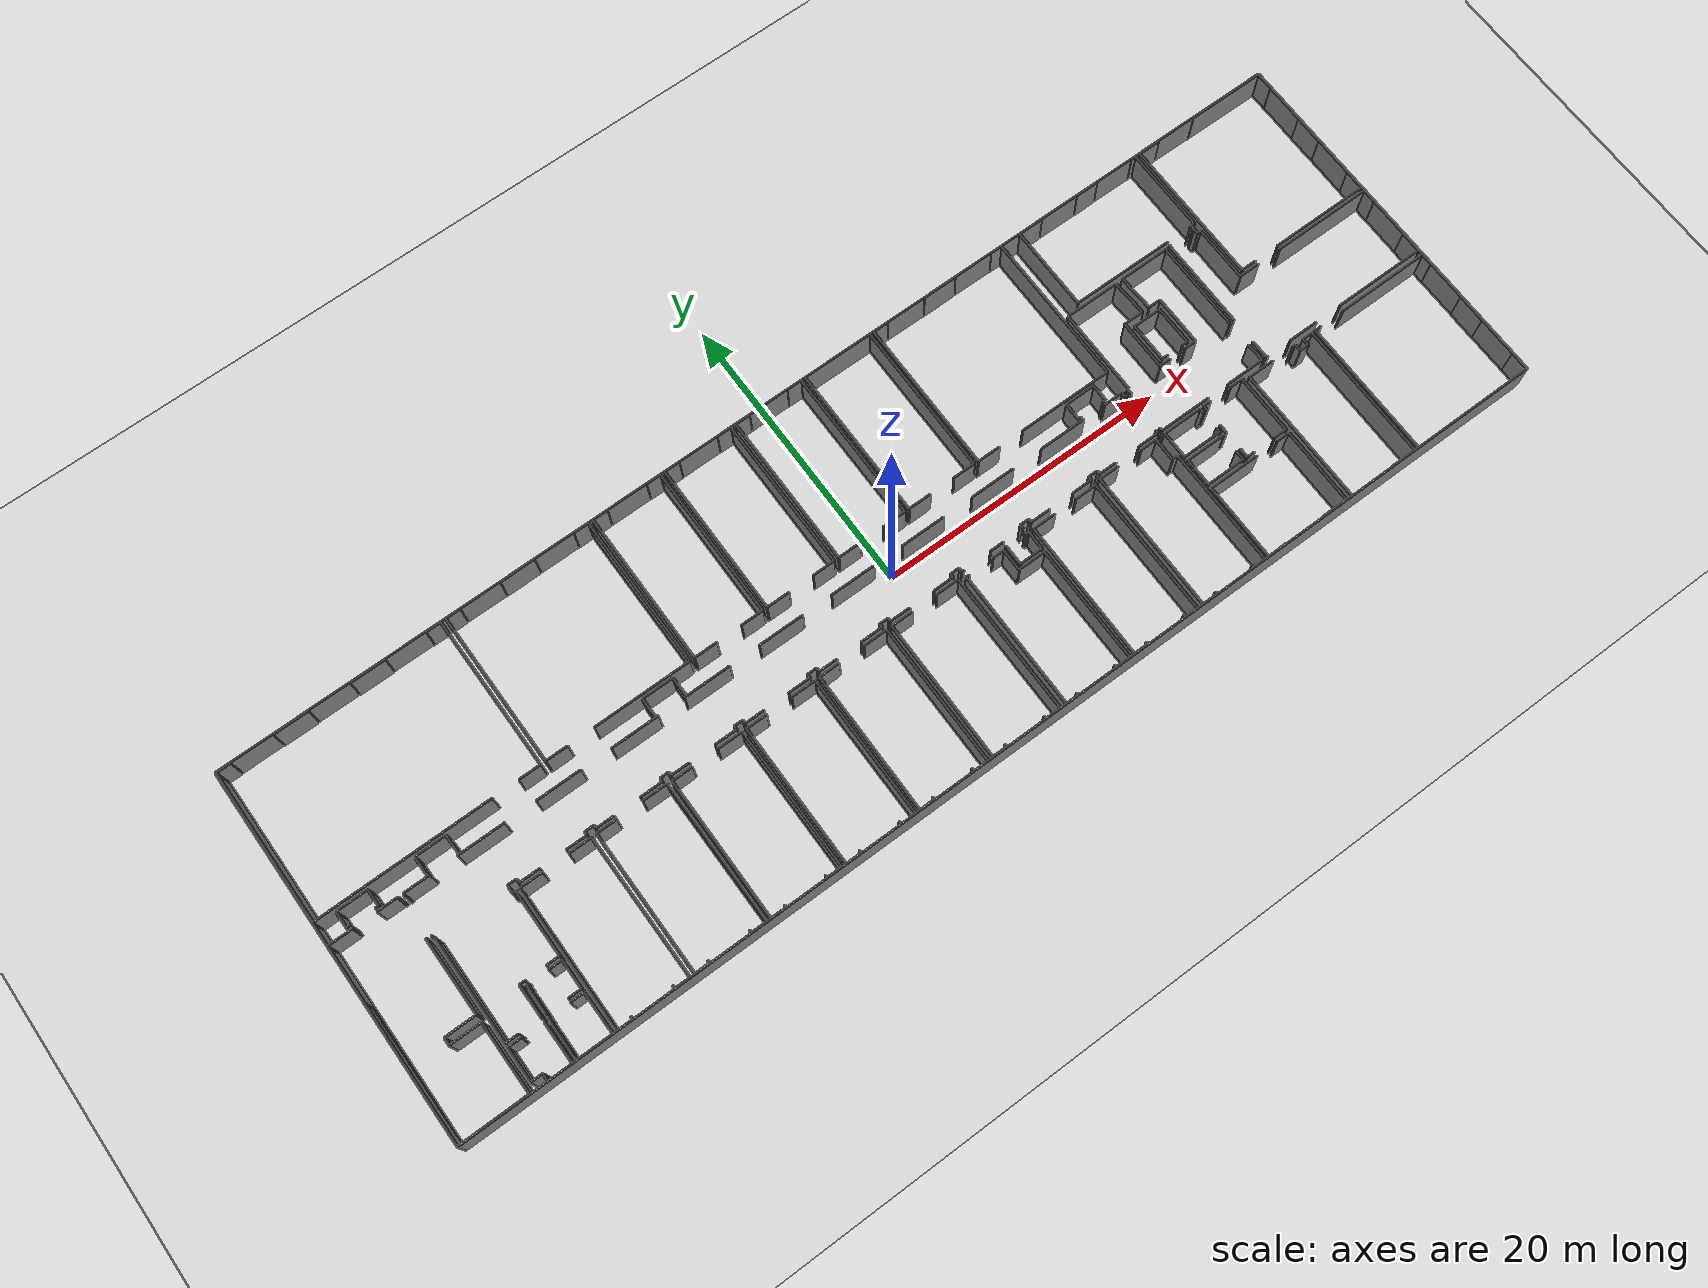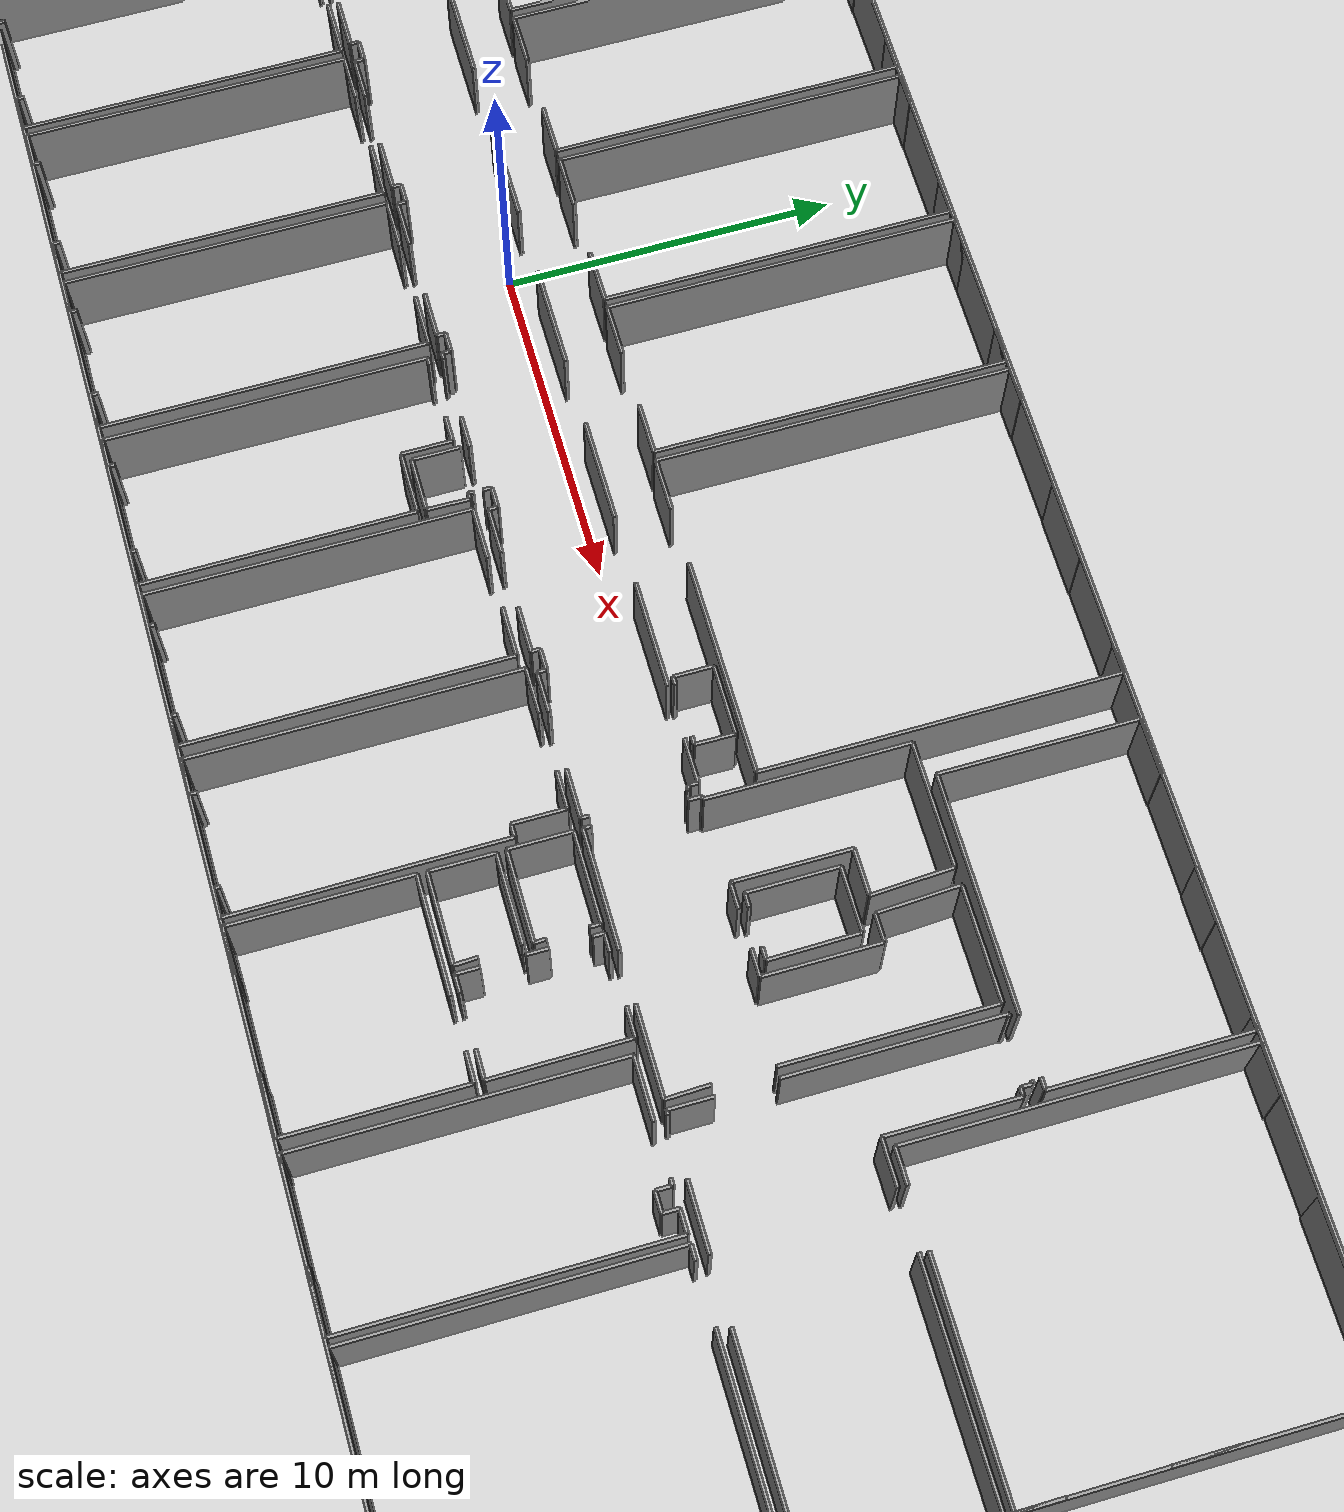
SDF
<sdf version="1.6">
  <world name="default">
    <light name="sun" type="directional">
      <cast_shadows>1</cast_shadows>
      <pose frame="">0 0 10 0 -0 0</pose>
      <diffuse>0.8 0.8 0.8 1</diffuse>
      <specular>0.1 0.1 0.1 1</specular>
      <attenuation>
        <range>1000</range>
        <constant>0.9</constant>
        <linear>0.01</linear>
        <quadratic>0.001</quadratic>
      </attenuation>
      <direction>-0.5 0.5 -1</direction>
    </light>
    <model name="ground_plane">
      <static>1</static>
      <link name="link">
        <collision name="collision">
          <geometry>
            <plane>
              <normal>0 0 1</normal>
              <size>100 100</size>
            </plane>
          </geometry>
          <surface>
            <friction>
              <ode>
                <mu>100</mu>
                <mu2>50</mu2>
              </ode>
              <torsional>
                <ode />
              </torsional>
            </friction>
            <contact>
              <ode />
            </contact>
            <bounce />
          </surface>
          <max_contacts>10</max_contacts>
        </collision>
        <visual name="visual">
          <cast_shadows>0</cast_shadows>
          <geometry>
            <plane>
              <normal>0 0 1</normal>
              <size>100 100</size>
            </plane>
          </geometry>
          <material>
            <script>
              <uri>file://media/materials/scripts/gazebo.material</uri>
              <name>Gazebo/Grey</name>
            </script>
          </material>
        </visual>
        <self_collide>0</self_collide>
        <kinematic>0</kinematic>
        <gravity>1</gravity>
      </link>
    </model>
    <gravity>0 0 -9.8</gravity>
    <magnetic_field>6e-06 2.3e-05 -4.2e-05</magnetic_field>
    <atmosphere type="adiabatic" />
    <physics default="0" name="default_physics" type="ode">
      <max_step_size>0.001</max_step_size>
      <real_time_factor>1</real_time_factor>
      <real_time_update_rate>1000</real_time_update_rate>
    </physics>
    <scene>
      <ambient>0.4 0.4 0.4 1</ambient>
      <background>0.7 0.7 0.7 1</background>
      <shadows>1</shadows>
    </scene>
    <spherical_coordinates>
      <surface_model>EARTH_WGS84</surface_model>
      <latitude_deg>0</latitude_deg>
      <longitude_deg>0</longitude_deg>
      <elevation>0</elevation>
      <heading_deg>0</heading_deg>
    </spherical_coordinates>
  <model name="0510030967_A-40">
		<static>1</static>
		<link name="Wall_0">
			<collision name="Wall_0_Collision">
				<geometry>
					<box>
						<size>1.53389109653 0.1 2.5</size>
					</box>
				</geometry>
				<pose frame="">0.766945548263 0 1.25 0 0 0</pose>
			</collision>
			<visual name="Wall_0_Visual">
				<pose frame="">0.766945548263 0 1.25 0 0 0</pose>
				<geometry>
					<box>
						<size>1.53389109653 0.1 2.5</size>
					</box>
				</geometry>
				<material>
					<script>
						<uri>file://media/materials/scripts/gazebo.material</uri>
						<name>Gazebo/Grey</name>
					</script>
					<ambient>1 1 1 1</ambient>
				</material>
			</visual>
			<pose frame="">15.2854621859 -10.6718549646 0 0 0 3.14159265359</pose>
		</link>
		<link name="Wall_1">
			<collision name="Wall_1_Collision">
				<geometry>
					<box>
						<size>11.944215217 0.1 2.5</size>
					</box>
				</geometry>
				<pose frame="">5.97210760852 0 1.25 0 0 0</pose>
			</collision>
			<visual name="Wall_1_Visual">
				<pose frame="">5.97210760852 0 1.25 0 0 0</pose>
				<geometry>
					<box>
						<size>11.944215217 0.1 2.5</size>
					</box>
				</geometry>
				<material>
					<script>
						<uri>file://media/materials/scripts/gazebo.material</uri>
						<name>Gazebo/Grey</name>
					</script>
					<ambient>1 1 1 1</ambient>
				</material>
			</visual>
			<pose frame="">11.9891578961 -10.6718549646 0 0 0 3.14159265359</pose>
		</link>
		<link name="Wall_2">
			<collision name="Wall_2_Collision">
				<geometry>
					<box>
						<size>10.6305940305 0.1 2.5</size>
					</box>
				</geometry>
				<pose frame="">5.31529701525 0 1.25 0 0 0</pose>
			</collision>
			<visual name="Wall_2_Visual">
				<pose frame="">5.31529701525 0 1.25 0 0 0</pose>
				<geometry>
					<box>
						<size>10.6305940305 0.1 2.5</size>
					</box>
				</geometry>
				<material>
					<script>
						<uri>file://media/materials/scripts/gazebo.material</uri>
						<name>Gazebo/Grey</name>
					</script>
					<ambient>1 1 1 1</ambient>
				</material>
			</visual>
			<pose frame="">0.0449426790407 -10.6718549646 0 0 0 1.57079632679</pose>
		</link>
		<link name="Wall_3">
			<collision name="Wall_3_Collision">
				<geometry>
					<box>
						<size>0.975027613087 0.1 2.5</size>
					</box>
				</geometry>
				<pose frame="">0.487513806543 0 1.25 0 0 0</pose>
			</collision>
			<visual name="Wall_3_Visual">
				<pose frame="">0.487513806543 0 1.25 0 0 0</pose>
				<geometry>
					<box>
						<size>0.975027613087 0.1 2.5</size>
					</box>
				</geometry>
				<material>
					<script>
						<uri>file://media/materials/scripts/gazebo.material</uri>
						<name>Gazebo/Grey</name>
					</script>
					<ambient>1 1 1 1</ambient>
				</material>
			</visual>
			<pose frame="">0.0449426790407 -0.0412609341475 0 0 0 0.0</pose>
		</link>
		<link name="Wall_4">
			<collision name="Wall_4_Collision">
				<geometry>
					<box>
						<size>2.38589764749 0.1 2.5</size>
					</box>
				</geometry>
				<pose frame="">1.19294882375 0 1.25 0 0 0</pose>
			</collision>
			<visual name="Wall_4_Visual">
				<pose frame="">1.19294882375 0 1.25 0 0 0</pose>
				<geometry>
					<box>
						<size>2.38589764749 0.1 2.5</size>
					</box>
				</geometry>
				<material>
					<script>
						<uri>file://media/materials/scripts/gazebo.material</uri>
						<name>Gazebo/Grey</name>
					</script>
					<ambient>1 1 1 1</ambient>
				</material>
			</visual>
			<pose frame="">3.85440603298 -0.0412609341475 0 0 0 0.0</pose>
		</link>
		<link name="Wall_5">
			<collision name="Wall_5_Collision">
				<geometry>
					<box>
						<size>2.39859331954 0.1 2.5</size>
					</box>
				</geometry>
				<pose frame="">1.19929665977 0 1.25 0 0 0</pose>
			</collision>
			<visual name="Wall_5_Visual">
				<pose frame="">1.19929665977 0 1.25 0 0 0</pose>
				<geometry>
					<box>
						<size>2.39859331954 0.1 2.5</size>
					</box>
				</geometry>
				<material>
					<script>
						<uri>file://media/materials/scripts/gazebo.material</uri>
						<name>Gazebo/Grey</name>
					</script>
					<ambient>1 1 1 1</ambient>
				</material>
			</visual>
			<pose frame="">9.0428732845 -0.0412609341475 0 0 0 0.0</pose>
		</link>
		<link name="Wall_6">
			<collision name="Wall_6_Collision">
				<geometry>
					<box>
						<size>1.02250942654 0.1 2.5</size>
					</box>
				</geometry>
				<pose frame="">0.511254713268 0 1.25 0 0 0</pose>
			</collision>
			<visual name="Wall_6_Visual">
				<pose frame="">0.511254713268 0 1.25 0 0 0</pose>
				<geometry>
					<box>
						<size>1.02250942654 0.1 2.5</size>
					</box>
				</geometry>
				<material>
					<script>
						<uri>file://media/materials/scripts/gazebo.material</uri>
						<name>Gazebo/Grey</name>
					</script>
					<ambient>1 1 1 1</ambient>
				</material>
			</visual>
			<pose frame="">14.2502570874 -0.0412609341475 0 0 0 0.0</pose>
		</link>
		<link name="Wall_7">
			<collision name="Wall_7_Collision">
				<geometry>
					<box>
						<size>10.6306016114 0.1 2.5</size>
					</box>
				</geometry>
				<pose frame="">5.31530080572 0 1.25 0 0 0</pose>
			</collision>
			<visual name="Wall_7_Visual">
				<pose frame="">5.31530080572 0 1.25 0 0 0</pose>
				<geometry>
					<box>
						<size>10.6306016114 0.1 2.5</size>
					</box>
				</geometry>
				<material>
					<script>
						<uri>file://media/materials/scripts/gazebo.material</uri>
						<name>Gazebo/Grey</name>
					</script>
					<ambient>1 1 1 1</ambient>
				</material>
			</visual>
			<pose frame="">15.2727665139 -0.0412609341475 0 0 0 -1.56960206936</pose>
		</link>
		<link name="Wall_8">
			<collision name="Wall_8_Collision">
				<geometry>
					<box>
						<size>0.24616908096 0.1 2.5</size>
					</box>
				</geometry>
				<pose frame="">0.12308454048 0 1.25 0 0 0</pose>
			</collision>
			<visual name="Wall_8_Visual">
				<pose frame="">0.12308454048 0 1.25 0 0 0</pose>
				<geometry>
					<box>
						<size>0.24616908096 0.1 2.5</size>
					</box>
				</geometry>
				<material>
					<script>
						<uri>file://media/materials/scripts/gazebo.material</uri>
						<name>Gazebo/Grey</name>
					</script>
					<ambient>1 1 1 1</ambient>
				</material>
			</visual>
			<pose frame="">3.50095852324 -12.0541597369 0 0 0 3.14159265359</pose>
		</link>
		<link name="Wall_9">
			<collision name="Wall_9_Collision">
				<geometry>
					<box>
						<size>0.258737796285 0.1 2.5</size>
					</box>
				</geometry>
				<pose frame="">0.129368898143 0 1.25 0 0 0</pose>
			</collision>
			<visual name="Wall_9_Visual">
				<pose frame="">0.129368898143 0 1.25 0 0 0</pose>
				<geometry>
					<box>
						<size>0.258737796285 0.1 2.5</size>
					</box>
				</geometry>
				<material>
					<script>
						<uri>file://media/materials/scripts/gazebo.material</uri>
						<name>Gazebo/Grey</name>
					</script>
					<ambient>1 1 1 1</ambient>
				</material>
			</visual>
			<pose frame="">1.65780085569 -12.0541597369 0 0 0 3.14159265359</pose>
		</link>
		<link name="Wall_10">
			<collision name="Wall_10_Collision">
				<geometry>
					<box>
						<size>1.12978785532 0.1 2.5</size>
					</box>
				</geometry>
				<pose frame="">0.56489392766 0 1.25 0 0 0</pose>
			</collision>
			<visual name="Wall_10_Visual">
				<pose frame="">0.56489392766 0 1.25 0 0 0</pose>
				<geometry>
					<box>
						<size>1.12978785532 0.1 2.5</size>
					</box>
				</geometry>
				<material>
					<script>
						<uri>file://media/materials/scripts/gazebo.material</uri>
						<name>Gazebo/Grey</name>
					</script>
					<ambient>1 1 1 1</ambient>
				</material>
			</visual>
			<pose frame="">1.3990630594 -12.0541597369 0 0 0 1.57079632679</pose>
		</link>
		<link name="Wall_11">
			<collision name="Wall_11_Collision">
				<geometry>
					<box>
						<size>2.08297891249 0.1 2.5</size>
					</box>
				</geometry>
				<pose frame="">1.04148945624 0 1.25 0 0 0</pose>
			</collision>
			<visual name="Wall_11_Visual">
				<pose frame="">1.04148945624 0 1.25 0 0 0</pose>
				<geometry>
					<box>
						<size>2.08297891249 0.1 2.5</size>
					</box>
				</geometry>
				<material>
					<script>
						<uri>file://media/materials/scripts/gazebo.material</uri>
						<name>Gazebo/Grey</name>
					</script>
					<ambient>1 1 1 1</ambient>
				</material>
			</visual>
			<pose frame="">1.3990630594 -10.9243718816 0 0 0 0.0</pose>
		</link>
		<link name="Wall_12">
			<collision name="Wall_12_Collision">
				<geometry>
					<box>
						<size>1.12994620843 0.1 2.5</size>
					</box>
				</geometry>
				<pose frame="">0.564973104215 0 1.25 0 0 0</pose>
			</collision>
			<visual name="Wall_12_Visual">
				<pose frame="">0.564973104215 0 1.25 0 0 0</pose>
				<geometry>
					<box>
						<size>1.12994620843 0.1 2.5</size>
					</box>
				</geometry>
				<material>
					<script>
						<uri>file://media/materials/scripts/gazebo.material</uri>
						<name>Gazebo/Grey</name>
					</script>
					<ambient>1 1 1 1</ambient>
				</material>
			</visual>
			<pose frame="">3.48204197189 -10.9243718816 0 0 0 -1.55405443685</pose>
		</link>
		<link name="Wall_13">
			<collision name="Wall_13_Collision">
				<geometry>
					<box>
						<size>4.65550293905 0.1 2.5</size>
					</box>
				</geometry>
				<pose frame="">2.32775146952 0 1.25 0 0 0</pose>
			</collision>
			<visual name="Wall_13_Visual">
				<pose frame="">2.32775146952 0 1.25 0 0 0</pose>
				<geometry>
					<box>
						<size>4.65550293905 0.1 2.5</size>
					</box>
				</geometry>
				<material>
					<script>
						<uri>file://media/materials/scripts/gazebo.material</uri>
						<name>Gazebo/Grey</name>
					</script>
					<ambient>1 1 1 1</ambient>
				</material>
			</visual>
			<pose frame="">4.65550293905 -25.713687204 0 0 0 3.14159265359</pose>
		</link>
		<link name="Wall_14">
			<collision name="Wall_14_Collision">
				<geometry>
					<box>
						<size>9.44596087194 0.1 2.5</size>
					</box>
				</geometry>
				<pose frame="">4.72298043597 0 1.25 0 0 0</pose>
			</collision>
			<visual name="Wall_14_Visual">
				<pose frame="">4.72298043597 0 1.25 0 0 0</pose>
				<geometry>
					<box>
						<size>9.44596087194 0.1 2.5</size>
					</box>
				</geometry>
				<material>
					<script>
						<uri>file://media/materials/scripts/gazebo.material</uri>
						<name>Gazebo/Grey</name>
					</script>
					<ambient>1 1 1 1</ambient>
				</material>
			</visual>
			<pose frame="">0.0 -25.713687204 0 0 0 1.57079632679</pose>
		</link>
		<link name="Wall_15">
			<collision name="Wall_15_Collision">
				<geometry>
					<box>
						<size>0.191958561326 0.1 2.5</size>
					</box>
				</geometry>
				<pose frame="">0.0959792806632 0 1.25 0 0 0</pose>
			</collision>
			<visual name="Wall_15_Visual">
				<pose frame="">0.0959792806632 0 1.25 0 0 0</pose>
				<geometry>
					<box>
						<size>0.191958561326 0.1 2.5</size>
					</box>
				</geometry>
				<material>
					<script>
						<uri>file://media/materials/scripts/gazebo.material</uri>
						<name>Gazebo/Grey</name>
					</script>
					<ambient>1 1 1 1</ambient>
				</material>
			</visual>
			<pose frame="">0.0 -12.4863204134 0 0 0 1.57079632679</pose>
		</link>
		<link name="Wall_16">
			<collision name="Wall_16_Collision">
				<geometry>
					<box>
						<size>1.64777127477 0.1 2.5</size>
					</box>
				</geometry>
				<pose frame="">0.823885637386 0 1.25 0 0 0</pose>
			</collision>
			<visual name="Wall_16_Visual">
				<pose frame="">0.823885637386 0 1.25 0 0 0</pose>
				<geometry>
					<box>
						<size>1.64777127477 0.1 2.5</size>
					</box>
				</geometry>
				<material>
					<script>
						<uri>file://media/materials/scripts/gazebo.material</uri>
						<name>Gazebo/Grey</name>
					</script>
					<ambient>1 1 1 1</ambient>
				</material>
			</visual>
			<pose frame="">0.0 -12.294361852 0 0 0 0.0</pose>
		</link>
		<link name="Wall_17">
			<collision name="Wall_17_Collision">
				<geometry>
					<box>
						<size>1.41379003898 0.1 2.5</size>
					</box>
				</geometry>
				<pose frame="">0.706895019488 0 1.25 0 0 0</pose>
			</collision>
			<visual name="Wall_17_Visual">
				<pose frame="">0.706895019488 0 1.25 0 0 0</pose>
				<geometry>
					<box>
						<size>1.41379003898 0.1 2.5</size>
					</box>
				</geometry>
				<material>
					<script>
						<uri>file://media/materials/scripts/gazebo.material</uri>
						<name>Gazebo/Grey</name>
					</script>
					<ambient>1 1 1 1</ambient>
				</material>
			</visual>
			<pose frame="">3.23587289093 -12.294361852 0 0 0 0.0</pose>
		</link>
		<link name="Wall_18">
			<collision name="Wall_18_Collision">
				<geometry>
					<box>
						<size>0.10067667932 0.1 2.5</size>
					</box>
				</geometry>
				<pose frame="">0.05033833966 0 1.25 0 0 0</pose>
			</collision>
			<visual name="Wall_18_Visual">
				<pose frame="">0.05033833966 0 1.25 0 0 0</pose>
				<geometry>
					<box>
						<size>0.10067667932 0.1 2.5</size>
					</box>
				</geometry>
				<material>
					<script>
						<uri>file://media/materials/scripts/gazebo.material</uri>
						<name>Gazebo/Grey</name>
					</script>
					<ambient>1 1 1 1</ambient>
				</material>
			</visual>
			<pose frame="">4.64966292991 -12.294361852 0 0 0 -1.57079632679</pose>
		</link>
		<link name="Wall_19">
			<collision name="Wall_19_Collision">
				<geometry>
					<box>
						<size>5.25054908782 0.1 2.5</size>
					</box>
				</geometry>
				<pose frame="">2.62527454391 0 1.25 0 0 0</pose>
			</collision>
			<visual name="Wall_19_Visual">
				<pose frame="">2.62527454391 0 1.25 0 0 0</pose>
				<geometry>
					<box>
						<size>5.25054908782 0.1 2.5</size>
					</box>
				</geometry>
				<material>
					<script>
						<uri>file://media/materials/scripts/gazebo.material</uri>
						<name>Gazebo/Grey</name>
					</script>
					<ambient>1 1 1 1</ambient>
				</material>
			</visual>
			<pose frame="">4.64966292991 -15.1492376249 0 0 0 -1.57079632679</pose>
		</link>
		<link name="Wall_20">
			<collision name="Wall_20_Collision">
				<geometry>
					<box>
						<size>2.10037198319 0.1 2.5</size>
					</box>
				</geometry>
				<pose frame="">1.0501859916 0 1.25 0 0 0</pose>
			</collision>
			<visual name="Wall_20_Visual">
				<pose frame="">1.0501859916 0 1.25 0 0 0</pose>
				<geometry>
					<box>
						<size>2.10037198319 0.1 2.5</size>
					</box>
				</geometry>
				<material>
					<script>
						<uri>file://media/materials/scripts/gazebo.material</uri>
						<name>Gazebo/Grey</name>
					</script>
					<ambient>1 1 1 1</ambient>
				</material>
			</visual>
			<pose frame="">4.64966292991 -20.3997867127 0 0 0 3.14159265359</pose>
		</link>
		<link name="Wall_21">
			<collision name="Wall_21_Collision">
				<geometry>
					<box>
						<size>0.509223405741 0.1 2.5</size>
					</box>
				</geometry>
				<pose frame="">0.25461170287 0 1.25 0 0 0</pose>
			</collision>
			<visual name="Wall_21_Visual">
				<pose frame="">0.25461170287 0 1.25 0 0 0</pose>
				<geometry>
					<box>
						<size>0.509223405741 0.1 2.5</size>
					</box>
				</geometry>
				<material>
					<script>
						<uri>file://media/materials/scripts/gazebo.material</uri>
						<name>Gazebo/Grey</name>
					</script>
					<ambient>1 1 1 1</ambient>
				</material>
			</visual>
			<pose frame="">2.54929094672 -20.3997867127 0 0 0 -1.57079632679</pose>
		</link>
		<link name="Wall_22">
			<collision name="Wall_22_Collision">
				<geometry>
					<box>
						<size>2.09529371437 0.1 2.5</size>
					</box>
				</geometry>
				<pose frame="">1.04764685719 0 1.25 0 0 0</pose>
			</collision>
			<visual name="Wall_22_Visual">
				<pose frame="">1.04764685719 0 1.25 0 0 0</pose>
				<geometry>
					<box>
						<size>2.09529371437 0.1 2.5</size>
					</box>
				</geometry>
				<material>
					<script>
						<uri>file://media/materials/scripts/gazebo.material</uri>
						<name>Gazebo/Grey</name>
					</script>
					<ambient>1 1 1 1</ambient>
				</material>
			</visual>
			<pose frame="">2.54929094672 -20.9090101185 0 0 0 0.0</pose>
		</link>
		<link name="Wall_23">
			<collision name="Wall_23_Collision">
				<geometry>
					<box>
						<size>4.80468949106 0.1 2.5</size>
					</box>
				</geometry>
				<pose frame="">2.40234474553 0 1.25 0 0 0</pose>
			</collision>
			<visual name="Wall_23_Visual">
				<pose frame="">2.40234474553 0 1.25 0 0 0</pose>
				<geometry>
					<box>
						<size>4.80468949106 0.1 2.5</size>
					</box>
				</geometry>
				<material>
					<script>
						<uri>file://media/materials/scripts/gazebo.material</uri>
						<name>Gazebo/Grey</name>
					</script>
					<ambient>1 1 1 1</ambient>
				</material>
			</visual>
			<pose frame="">4.64458466109 -20.9090101185 0 0 0 -1.5685239037</pose>
		</link>
		<link name="Wall_24">
			<collision name="Wall_24_Collision">
				<geometry>
					<box>
						<size>0.126194980131 0.1 2.5</size>
					</box>
				</geometry>
				<pose frame="">0.0630974900656 0 1.25 0 0 0</pose>
			</collision>
			<visual name="Wall_24_Visual">
				<pose frame="">0.0630974900656 0 1.25 0 0 0</pose>
				<geometry>
					<box>
						<size>0.126194980131 0.1 2.5</size>
					</box>
				</geometry>
				<material>
					<script>
						<uri>file://media/materials/scripts/gazebo.material</uri>
						<name>Gazebo/Grey</name>
					</script>
					<ambient>1 1 1 1</ambient>
				</material>
			</visual>
			<pose frame="">8.71430929196 -12.2597026674 0 0 0 3.14159265359</pose>
		</link>
		<link name="Wall_25">
			<collision name="Wall_25_Collision">
				<geometry>
					<box>
						<size>0.141048916424 0.1 2.5</size>
					</box>
				</geometry>
				<pose frame="">0.0705244582122 0 1.25 0 0 0</pose>
			</collision>
			<visual name="Wall_25_Visual">
				<pose frame="">0.0705244582122 0 1.25 0 0 0</pose>
				<geometry>
					<box>
						<size>0.141048916424 0.1 2.5</size>
					</box>
				</geometry>
				<material>
					<script>
						<uri>file://media/materials/scripts/gazebo.material</uri>
						<name>Gazebo/Grey</name>
					</script>
					<ambient>1 1 1 1</ambient>
				</material>
			</visual>
			<pose frame="">6.75105056686 -12.2597026674 0 0 0 3.14159265359</pose>
		</link>
		<link name="Wall_26">
			<collision name="Wall_26_Collision">
				<geometry>
					<box>
						<size>1.34612210697 0.1 2.5</size>
					</box>
				</geometry>
				<pose frame="">0.673061053487 0 1.25 0 0 0</pose>
			</collision>
			<visual name="Wall_26_Visual">
				<pose frame="">0.673061053487 0 1.25 0 0 0</pose>
				<geometry>
					<box>
						<size>1.34612210697 0.1 2.5</size>
					</box>
				</geometry>
				<material>
					<script>
						<uri>file://media/materials/scripts/gazebo.material</uri>
						<name>Gazebo/Grey</name>
					</script>
					<ambient>1 1 1 1</ambient>
				</material>
			</visual>
			<pose frame="">6.61000165044 -12.2597026674 0 0 0 1.57079632679</pose>
		</link>
		<link name="Wall_27">
			<collision name="Wall_27_Collision">
				<geometry>
					<box>
						<size>2.08754935443 0.1 2.5</size>
					</box>
				</geometry>
				<pose frame="">1.04377467721 0 1.25 0 0 0</pose>
			</collision>
			<visual name="Wall_27_Visual">
				<pose frame="">1.04377467721 0 1.25 0 0 0</pose>
				<geometry>
					<box>
						<size>2.08754935443 0.1 2.5</size>
					</box>
				</geometry>
				<material>
					<script>
						<uri>file://media/materials/scripts/gazebo.material</uri>
						<name>Gazebo/Grey</name>
					</script>
					<ambient>1 1 1 1</ambient>
				</material>
			</visual>
			<pose frame="">6.61000165044 -10.9135805604 0 0 0 0.0</pose>
		</link>
		<link name="Wall_28">
			<collision name="Wall_28_Collision">
				<geometry>
					<box>
						<size>1.34622641746 0.1 2.5</size>
					</box>
				</geometry>
				<pose frame="">0.673113208731 0 1.25 0 0 0</pose>
			</collision>
			<visual name="Wall_28_Visual">
				<pose frame="">0.673113208731 0 1.25 0 0 0</pose>
				<geometry>
					<box>
						<size>1.34622641746 0.1 2.5</size>
					</box>
				</geometry>
				<material>
					<script>
						<uri>file://media/materials/scripts/gazebo.material</uri>
						<name>Gazebo/Grey</name>
					</script>
					<ambient>1 1 1 1</ambient>
				</material>
			</visual>
			<pose frame="">8.69755100486 -10.9135805604 0 0 0 -1.55834766309</pose>
		</link>
		<link name="Wall_29">
			<collision name="Wall_29_Collision">
				<geometry>
					<box>
						<size>0.902027498826 0.1 2.5</size>
					</box>
				</geometry>
				<pose frame="">0.451013749413 0 1.25 0 0 0</pose>
			</collision>
			<visual name="Wall_29_Visual">
				<pose frame="">0.451013749413 0 1.25 0 0 0</pose>
				<geometry>
					<box>
						<size>0.902027498826 0.1 2.5</size>
					</box>
				</geometry>
				<material>
					<script>
						<uri>file://media/materials/scripts/gazebo.material</uri>
						<name>Gazebo/Grey</name>
					</script>
					<ambient>1 1 1 1</ambient>
				</material>
			</visual>
			<pose frame="">10.1393984791 -20.4303832823 0 0 0 3.14159265359</pose>
		</link>
		<link name="Wall_30">
			<collision name="Wall_30_Collision">
				<geometry>
					<box>
						<size>0.403976284485 0.1 2.5</size>
					</box>
				</geometry>
				<pose frame="">0.201988142242 0 1.25 0 0 0</pose>
			</collision>
			<visual name="Wall_30_Visual">
				<pose frame="">0.201988142242 0 1.25 0 0 0</pose>
				<geometry>
					<box>
						<size>0.403976284485 0.1 2.5</size>
					</box>
				</geometry>
				<material>
					<script>
						<uri>file://media/materials/scripts/gazebo.material</uri>
						<name>Gazebo/Grey</name>
					</script>
					<ambient>1 1 1 1</ambient>
				</material>
			</visual>
			<pose frame="">7.84986098239 -20.4303832823 0 0 0 3.14159265359</pose>
		</link>
		<link name="Wall_31">
			<collision name="Wall_31_Collision">
				<geometry>
					<box>
						<size>2.22796348725 0.1 2.5</size>
					</box>
				</geometry>
				<pose frame="">1.11398174362 0 1.25 0 0 0</pose>
			</collision>
			<visual name="Wall_31_Visual">
				<pose frame="">1.11398174362 0 1.25 0 0 0</pose>
				<geometry>
					<box>
						<size>2.22796348725 0.1 2.5</size>
					</box>
				</geometry>
				<material>
					<script>
						<uri>file://media/materials/scripts/gazebo.material</uri>
						<name>Gazebo/Grey</name>
					</script>
					<ambient>1 1 1 1</ambient>
				</material>
			</visual>
			<pose frame="">7.44588469791 -20.4303832823 0 0 0 -1.57079632679</pose>
		</link>
		<link name="Wall_32">
			<collision name="Wall_32_Collision">
				<geometry>
					<box>
						<size>0.894664009039 0.1 2.5</size>
					</box>
				</geometry>
				<pose frame="">0.44733200452 0 1.25 0 0 0</pose>
			</collision>
			<visual name="Wall_32_Visual">
				<pose frame="">0.44733200452 0 1.25 0 0 0</pose>
				<geometry>
					<box>
						<size>0.894664009039 0.1 2.5</size>
					</box>
				</geometry>
				<material>
					<script>
						<uri>file://media/materials/scripts/gazebo.material</uri>
						<name>Gazebo/Grey</name>
					</script>
					<ambient>1 1 1 1</ambient>
				</material>
			</visual>
			<pose frame="">5.96455368365 -22.6583467696 0 0 0 3.14159265359</pose>
		</link>
		<link name="Wall_33">
			<collision name="Wall_33_Collision">
				<geometry>
					<box>
						<size>7.22091738926 0.1 2.5</size>
					</box>
				</geometry>
				<pose frame="">3.61045869463 0 1.25 0 0 0</pose>
			</collision>
			<visual name="Wall_33_Visual">
				<pose frame="">3.61045869463 0 1.25 0 0 0</pose>
				<geometry>
					<box>
						<size>7.22091738926 0.1 2.5</size>
					</box>
				</geometry>
				<material>
					<script>
						<uri>file://media/materials/scripts/gazebo.material</uri>
						<name>Gazebo/Grey</name>
					</script>
					<ambient>1 1 1 1</ambient>
				</material>
			</visual>
			<pose frame="">5.06988967461 -22.6583467696 0 0 0 1.57079632679</pose>
		</link>
		<link name="Wall_34">
			<collision name="Wall_34_Collision">
				<geometry>
					<box>
						<size>0.496400776975 0.1 2.5</size>
					</box>
				</geometry>
				<pose frame="">0.248200388488 0 1.25 0 0 0</pose>
			</collision>
			<visual name="Wall_34_Visual">
				<pose frame="">0.248200388488 0 1.25 0 0 0</pose>
				<geometry>
					<box>
						<size>0.496400776975 0.1 2.5</size>
					</box>
				</geometry>
				<material>
					<script>
						<uri>file://media/materials/scripts/gazebo.material</uri>
						<name>Gazebo/Grey</name>
					</script>
					<ambient>1 1 1 1</ambient>
				</material>
			</visual>
			<pose frame="">9.93944164434 -15.4374293803 0 0 0 -1.57079632679</pose>
		</link>
		<link name="Wall_35">
			<collision name="Wall_35_Collision">
				<geometry>
					<box>
						<size>0.196021176381 0.1 2.5</size>
					</box>
				</geometry>
				<pose frame="">0.0980105881905 0 1.25 0 0 0</pose>
			</collision>
			<visual name="Wall_35_Visual">
				<pose frame="">0.0980105881905 0 1.25 0 0 0</pose>
				<geometry>
					<box>
						<size>0.196021176381 0.1 2.5</size>
					</box>
				</geometry>
				<material>
					<script>
						<uri>file://media/materials/scripts/gazebo.material</uri>
						<name>Gazebo/Grey</name>
					</script>
					<ambient>1 1 1 1</ambient>
				</material>
			</visual>
			<pose frame="">9.93944164434 -15.9338301573 0 0 0 0.0</pose>
		</link>
		<link name="Wall_36">
			<collision name="Wall_36_Collision">
				<geometry>
					<box>
						<size>4.4965548474 0.1 2.5</size>
					</box>
				</geometry>
				<pose frame="">2.2482774237 0 1.25 0 0 0</pose>
			</collision>
			<visual name="Wall_36_Visual">
				<pose frame="">2.2482774237 0 1.25 0 0 0</pose>
				<geometry>
					<box>
						<size>4.4965548474 0.1 2.5</size>
					</box>
				</geometry>
				<material>
					<script>
						<uri>file://media/materials/scripts/gazebo.material</uri>
						<name>Gazebo/Grey</name>
					</script>
					<ambient>1 1 1 1</ambient>
				</material>
			</visual>
			<pose frame="">10.1354628207 -15.9338301573 0 0 0 -1.56992106585</pose>
		</link>
		<link name="Wall_37">
			<collision name="Wall_37_Collision">
				<geometry>
					<box>
						<size>0.170375918849 0.1 2.5</size>
					</box>
				</geometry>
				<pose frame="">0.0851879594246 0 1.25 0 0 0</pose>
			</collision>
			<visual name="Wall_37_Visual">
				<pose frame="">0.0851879594246 0 1.25 0 0 0</pose>
				<geometry>
					<box>
						<size>0.170375918849 0.1 2.5</size>
					</box>
				</geometry>
				<material>
					<script>
						<uri>file://media/materials/scripts/gazebo.material</uri>
						<name>Gazebo/Grey</name>
					</script>
					<ambient>1 1 1 1</ambient>
				</material>
			</visual>
			<pose frame="">4.96527733696 -15.3490675029 0 0 0 1.57079632679</pose>
		</link>
		<link name="Wall_38">
			<collision name="Wall_38_Collision">
				<geometry>
					<box>
						<size>0.130638465347 0.1 2.5</size>
					</box>
				</geometry>
				<pose frame="">0.0653192326736 0 1.25 0 0 0</pose>
			</collision>
			<visual name="Wall_38_Visual">
				<pose frame="">0.0653192326736 0 1.25 0 0 0</pose>
				<geometry>
					<box>
						<size>0.130638465347 0.1 2.5</size>
					</box>
				</geometry>
				<material>
					<script>
						<uri>file://media/materials/scripts/gazebo.material</uri>
						<name>Gazebo/Grey</name>
					</script>
					<ambient>1 1 1 1</ambient>
				</material>
			</visual>
			<pose frame="">4.96527733696 -12.4205568322 0 0 0 1.57079632679</pose>
		</link>
		<link name="Wall_39">
			<collision name="Wall_39_Collision">
				<geometry>
					<box>
						<size>1.78755062399 0.1 2.5</size>
					</box>
				</geometry>
				<pose frame="">0.893775311996 0 1.25 0 0 0</pose>
			</collision>
			<visual name="Wall_39_Visual">
				<pose frame="">0.893775311996 0 1.25 0 0 0</pose>
				<geometry>
					<box>
						<size>1.78755062399 0.1 2.5</size>
					</box>
				</geometry>
				<material>
					<script>
						<uri>file://media/materials/scripts/gazebo.material</uri>
						<name>Gazebo/Grey</name>
					</script>
					<ambient>1 1 1 1</ambient>
				</material>
			</visual>
			<pose frame="">4.96527733696 -12.2899183668 0 0 0 0.0</pose>
		</link>
		<link name="Wall_40">
			<collision name="Wall_40_Collision">
				<geometry>
					<box>
						<size>3.1878832506 0.1 2.5</size>
					</box>
				</geometry>
				<pose frame="">1.5939416253 0 1.25 0 0 0</pose>
			</collision>
			<visual name="Wall_40_Visual">
				<pose frame="">1.5939416253 0 1.25 0 0 0</pose>
				<geometry>
					<box>
						<size>3.1878832506 0.1 2.5</size>
					</box>
				</geometry>
				<material>
					<script>
						<uri>file://media/materials/scripts/gazebo.material</uri>
						<name>Gazebo/Grey</name>
					</script>
					<ambient>1 1 1 1</ambient>
				</material>
			</visual>
			<pose frame="">8.58811431183 -12.2899183668 0 0 0 0.0</pose>
		</link>
		<link name="Wall_41">
			<collision name="Wall_41_Collision">
				<geometry>
					<box>
						<size>3.10663094951 0.1 2.5</size>
					</box>
				</geometry>
				<pose frame="">1.55331547475 0 1.25 0 0 0</pose>
			</collision>
			<visual name="Wall_41_Visual">
				<pose frame="">1.55331547475 0 1.25 0 0 0</pose>
				<geometry>
					<box>
						<size>3.10663094951 0.1 2.5</size>
					</box>
				</geometry>
				<material>
					<script>
						<uri>file://media/materials/scripts/gazebo.material</uri>
						<name>Gazebo/Grey</name>
					</script>
					<ambient>1 1 1 1</ambient>
				</material>
			</visual>
			<pose frame="">13.8902078282 -12.2899183668 0 0 0 0.0</pose>
		</link>
		<link name="Wall_42">
			<collision name="Wall_42_Collision">
				<geometry>
					<box>
						<size>3.27192859954 0.1 2.5</size>
					</box>
				</geometry>
				<pose frame="">1.63596429977 0 1.25 0 0 0</pose>
			</collision>
			<visual name="Wall_42_Visual">
				<pose frame="">1.63596429977 0 1.25 0 0 0</pose>
				<geometry>
					<box>
						<size>3.27192859954 0.1 2.5</size>
					</box>
				</geometry>
				<material>
					<script>
						<uri>file://media/materials/scripts/gazebo.material</uri>
						<name>Gazebo/Grey</name>
					</script>
					<ambient>1 1 1 1</ambient>
				</material>
			</visual>
			<pose frame="">19.0766437721 -12.2899183668 0 0 0 0.0</pose>
		</link>
		<link name="Wall_43">
			<collision name="Wall_43_Collision">
				<geometry>
					<box>
						<size>3.22051112776 0.1 2.5</size>
					</box>
				</geometry>
				<pose frame="">1.61025556388 0 1.25 0 0 0</pose>
			</collision>
			<visual name="Wall_43_Visual">
				<pose frame="">1.61025556388 0 1.25 0 0 0</pose>
				<geometry>
					<box>
						<size>3.22051112776 0.1 2.5</size>
					</box>
				</geometry>
				<material>
					<script>
						<uri>file://media/materials/scripts/gazebo.material</uri>
						<name>Gazebo/Grey</name>
					</script>
					<ambient>1 1 1 1</ambient>
				</material>
			</visual>
			<pose frame="">24.1571978113 -12.2899183668 0 0 0 0.0</pose>
		</link>
		<link name="Wall_44">
			<collision name="Wall_44_Collision">
				<geometry>
					<box>
						<size>3.1103126944 0.1 2.5</size>
					</box>
				</geometry>
				<pose frame="">1.5551563472 0 1.25 0 0 0</pose>
			</collision>
			<visual name="Wall_44_Visual">
				<pose frame="">1.5551563472 0 1.25 0 0 0</pose>
				<geometry>
					<box>
						<size>3.1103126944 0.1 2.5</size>
					</box>
				</geometry>
				<material>
					<script>
						<uri>file://media/materials/scripts/gazebo.material</uri>
						<name>Gazebo/Grey</name>
					</script>
					<ambient>1 1 1 1</ambient>
				</material>
			</visual>
			<pose frame="">29.4832861478 -12.2899183668 0 0 0 0.0</pose>
		</link>
		<link name="Wall_45">
			<collision name="Wall_45_Collision">
				<geometry>
					<box>
						<size>3.09545875811 0.1 2.5</size>
					</box>
				</geometry>
				<pose frame="">1.54772937905 0 1.25 0 0 0</pose>
			</collision>
			<visual name="Wall_45_Visual">
				<pose frame="">1.54772937905 0 1.25 0 0 0</pose>
				<geometry>
					<box>
						<size>3.09545875811 0.1 2.5</size>
					</box>
				</geometry>
				<material>
					<script>
						<uri>file://media/materials/scripts/gazebo.material</uri>
						<name>Gazebo/Grey</name>
					</script>
					<ambient>1 1 1 1</ambient>
				</material>
			</visual>
			<pose frame="">34.6960021329 -12.2899183668 0 0 0 0.0</pose>
		</link>
		<link name="Wall_46">
			<collision name="Wall_46_Collision">
				<geometry>
					<box>
						<size>3.07362220219 0.1 2.5</size>
					</box>
				</geometry>
				<pose frame="">1.5368111011 0 1.25 0 0 0</pose>
			</collision>
			<visual name="Wall_46_Visual">
				<pose frame="">1.5368111011 0 1.25 0 0 0</pose>
				<geometry>
					<box>
						<size>3.07362220219 0.1 2.5</size>
					</box>
				</geometry>
				<material>
					<script>
						<uri>file://media/materials/scripts/gazebo.material</uri>
						<name>Gazebo/Grey</name>
					</script>
					<ambient>1 1 1 1</ambient>
				</material>
			</visual>
			<pose frame="">39.8865006919 -12.2899183668 0 0 0 0.0</pose>
		</link>
		<link name="Wall_47">
			<collision name="Wall_47_Collision">
				<geometry>
					<box>
						<size>3.10066398365 0.1 2.5</size>
					</box>
				</geometry>
				<pose frame="">1.55033199182 0 1.25 0 0 0</pose>
			</collision>
			<visual name="Wall_47_Visual">
				<pose frame="">1.55033199182 0 1.25 0 0 0</pose>
				<geometry>
					<box>
						<size>3.10066398365 0.1 2.5</size>
					</box>
				</geometry>
				<material>
					<script>
						<uri>file://media/materials/scripts/gazebo.material</uri>
						<name>Gazebo/Grey</name>
					</script>
					<ambient>1 1 1 1</ambient>
				</material>
			</visual>
			<pose frame="">45.0733175061 -12.2899183668 0 0 0 0.0</pose>
		</link>
		<link name="Wall_48">
			<collision name="Wall_48_Collision">
				<geometry>
					<box>
						<size>3.26393032615 0.1 2.5</size>
					</box>
				</geometry>
				<pose frame="">1.63196516308 0 1.25 0 0 0</pose>
			</collision>
			<visual name="Wall_48_Visual">
				<pose frame="">1.63196516308 0 1.25 0 0 0</pose>
				<geometry>
					<box>
						<size>3.26393032615 0.1 2.5</size>
					</box>
				</geometry>
				<material>
					<script>
						<uri>file://media/materials/scripts/gazebo.material</uri>
						<name>Gazebo/Grey</name>
					</script>
					<ambient>1 1 1 1</ambient>
				</material>
			</visual>
			<pose frame="">50.305203956 -12.2899183668 0 0 0 0.0</pose>
		</link>
		<link name="Wall_49">
			<collision name="Wall_49_Collision">
				<geometry>
					<box>
						<size>1.36059517311 0.1 2.5</size>
					</box>
				</geometry>
				<pose frame="">0.680297586553 0 1.25 0 0 0</pose>
			</collision>
			<visual name="Wall_49_Visual">
				<pose frame="">0.680297586553 0 1.25 0 0 0</pose>
				<geometry>
					<box>
						<size>1.36059517311 0.1 2.5</size>
					</box>
				</geometry>
				<material>
					<script>
						<uri>file://media/materials/scripts/gazebo.material</uri>
						<name>Gazebo/Grey</name>
					</script>
					<ambient>1 1 1 1</ambient>
				</material>
			</visual>
			<pose frame="">55.1893559486 -12.2899183668 0 0 0 0.0</pose>
		</link>
		<link name="Wall_50">
			<collision name="Wall_50_Collision">
				<geometry>
					<box>
						<size>0.29365089441 0.1 2.5</size>
					</box>
				</geometry>
				<pose frame="">0.146825447205 0 1.25 0 0 0</pose>
			</collision>
			<visual name="Wall_50_Visual">
				<pose frame="">0.146825447205 0 1.25 0 0 0</pose>
				<geometry>
					<box>
						<size>0.29365089441 0.1 2.5</size>
					</box>
				</geometry>
				<material>
					<script>
						<uri>file://media/materials/scripts/gazebo.material</uri>
						<name>Gazebo/Grey</name>
					</script>
					<ambient>1 1 1 1</ambient>
				</material>
			</visual>
			<pose frame="">56.5499511217 -12.2899183668 0 0 0 -1.57079632679</pose>
		</link>
		<link name="Wall_51">
			<collision name="Wall_51_Collision">
				<geometry>
					<box>
						<size>0.102581030127 0.1 2.5</size>
					</box>
				</geometry>
				<pose frame="">0.0512905150634 0 1.25 0 0 0</pose>
			</collision>
			<visual name="Wall_51_Visual">
				<pose frame="">0.0512905150634 0 1.25 0 0 0</pose>
				<geometry>
					<box>
						<size>0.102581030127 0.1 2.5</size>
					</box>
				</geometry>
				<material>
					<script>
						<uri>file://media/materials/scripts/gazebo.material</uri>
						<name>Gazebo/Grey</name>
					</script>
					<ambient>1 1 1 1</ambient>
				</material>
			</visual>
			<pose frame="">56.5499511217 -12.5835692612 0 0 0 0.0</pose>
		</link>
		<link name="Wall_52">
			<collision name="Wall_52_Collision">
				<geometry>
					<box>
						<size>0.0933131895337 0.1 2.5</size>
					</box>
				</geometry>
				<pose frame="">0.0466565947668 0 1.25 0 0 0</pose>
			</collision>
			<visual name="Wall_52_Visual">
				<pose frame="">0.0466565947668 0 1.25 0 0 0</pose>
				<geometry>
					<box>
						<size>0.0933131895337 0.1 2.5</size>
					</box>
				</geometry>
				<material>
					<script>
						<uri>file://media/materials/scripts/gazebo.material</uri>
						<name>Gazebo/Grey</name>
					</script>
					<ambient>1 1 1 1</ambient>
				</material>
			</visual>
			<pose frame="">56.6525321518 -12.5835692612 0 0 0 -1.57079632679</pose>
		</link>
		<link name="Wall_53">
			<collision name="Wall_53_Collision">
				<geometry>
					<box>
						<size>0.228141226656 0.1 2.5</size>
					</box>
				</geometry>
				<pose frame="">0.114070613328 0 1.25 0 0 0</pose>
			</collision>
			<visual name="Wall_53_Visual">
				<pose frame="">0.114070613328 0 1.25 0 0 0</pose>
				<geometry>
					<box>
						<size>0.228141226656 0.1 2.5</size>
					</box>
				</geometry>
				<material>
					<script>
						<uri>file://media/materials/scripts/gazebo.material</uri>
						<name>Gazebo/Grey</name>
					</script>
					<ambient>1 1 1 1</ambient>
				</material>
			</visual>
			<pose frame="">56.6525321518 -15.4301928473 0 0 0 -1.57079632679</pose>
		</link>
		<link name="Wall_54">
			<collision name="Wall_54_Collision">
				<geometry>
					<box>
						<size>1.49656582071 0.1 2.5</size>
					</box>
				</geometry>
				<pose frame="">0.748282910356 0 1.25 0 0 0</pose>
			</collision>
			<visual name="Wall_54_Visual">
				<pose frame="">0.748282910356 0 1.25 0 0 0</pose>
				<geometry>
					<box>
						<size>1.49656582071 0.1 2.5</size>
					</box>
				</geometry>
				<material>
					<script>
						<uri>file://media/materials/scripts/gazebo.material</uri>
						<name>Gazebo/Grey</name>
					</script>
					<ambient>1 1 1 1</ambient>
				</material>
			</visual>
			<pose frame="">56.6525321518 -15.6583340739 0 0 0 3.14159265359</pose>
		</link>
		<link name="Wall_55">
			<collision name="Wall_55_Collision">
				<geometry>
					<box>
						<size>1.23833585131 0.1 2.5</size>
					</box>
				</geometry>
				<pose frame="">0.619167925654 0 1.25 0 0 0</pose>
			</collision>
			<visual name="Wall_55_Visual">
				<pose frame="">0.619167925654 0 1.25 0 0 0</pose>
				<geometry>
					<box>
						<size>1.23833585131 0.1 2.5</size>
					</box>
				</geometry>
				<material>
					<script>
						<uri>file://media/materials/scripts/gazebo.material</uri>
						<name>Gazebo/Grey</name>
					</script>
					<ambient>1 1 1 1</ambient>
				</material>
			</visual>
			<pose frame="">53.4058679396 -15.6583340739 0 0 0 3.14159265359</pose>
		</link>
		<link name="Wall_56">
			<collision name="Wall_56_Collision">
				<geometry>
					<box>
						<size>0.257468229081 0.1 2.5</size>
					</box>
				</geometry>
				<pose frame="">0.12873411454 0 1.25 0 0 0</pose>
			</collision>
			<visual name="Wall_56_Visual">
				<pose frame="">0.12873411454 0 1.25 0 0 0</pose>
				<geometry>
					<box>
						<size>0.257468229081 0.1 2.5</size>
					</box>
				</geometry>
				<material>
					<script>
						<uri>file://media/materials/scripts/gazebo.material</uri>
						<name>Gazebo/Grey</name>
					</script>
					<ambient>1 1 1 1</ambient>
				</material>
			</visual>
			<pose frame="">52.1675320883 -15.6583340739 0 0 0 1.57079632679</pose>
		</link>
		<link name="Wall_57">
			<collision name="Wall_57_Collision">
				<geometry>
					<box>
						<size>0.652811456574 0.1 2.5</size>
					</box>
				</geometry>
				<pose frame="">0.326405728287 0 1.25 0 0 0</pose>
			</collision>
			<visual name="Wall_57_Visual">
				<pose frame="">0.326405728287 0 1.25 0 0 0</pose>
				<geometry>
					<box>
						<size>0.652811456574 0.1 2.5</size>
					</box>
				</geometry>
				<material>
					<script>
						<uri>file://media/materials/scripts/gazebo.material</uri>
						<name>Gazebo/Grey</name>
					</script>
					<ambient>1 1 1 1</ambient>
				</material>
			</visual>
			<pose frame="">52.1675320883 -15.4008658448 0 0 0 3.14159265359</pose>
		</link>
		<link name="Wall_58">
			<collision name="Wall_58_Collision">
				<geometry>
					<box>
						<size>0.259245623167 0.1 2.5</size>
					</box>
				</geometry>
				<pose frame="">0.129622811584 0 1.25 0 0 0</pose>
			</collision>
			<visual name="Wall_58_Visual">
				<pose frame="">0.129622811584 0 1.25 0 0 0</pose>
				<geometry>
					<box>
						<size>0.259245623167 0.1 2.5</size>
					</box>
				</geometry>
				<material>
					<script>
						<uri>file://media/materials/scripts/gazebo.material</uri>
						<name>Gazebo/Grey</name>
					</script>
					<ambient>1 1 1 1</ambient>
				</material>
			</visual>
			<pose frame="">51.5147206317 -15.4008658448 0 0 0 -1.57079632679</pose>
		</link>
		<link name="Wall_59">
			<collision name="Wall_59_Collision">
				<geometry>
					<box>
						<size>1.40160219381 0.1 2.5</size>
					</box>
				</geometry>
				<pose frame="">0.700801096906 0 1.25 0 0 0</pose>
			</collision>
			<visual name="Wall_59_Visual">
				<pose frame="">0.700801096906 0 1.25 0 0 0</pose>
				<geometry>
					<box>
						<size>1.40160219381 0.1 2.5</size>
					</box>
				</geometry>
				<material>
					<script>
						<uri>file://media/materials/scripts/gazebo.material</uri>
						<name>Gazebo/Grey</name>
					</script>
					<ambient>1 1 1 1</ambient>
				</material>
			</visual>
			<pose frame="">51.5147206317 -15.660111468 0 0 0 3.14159265359</pose>
		</link>
		<link name="Wall_60">
			<collision name="Wall_60_Collision">
				<geometry>
					<box>
						<size>1.39360392042 0.1 2.5</size>
					</box>
				</geometry>
				<pose frame="">0.696801960212 0 1.25 0 0 0</pose>
			</collision>
			<visual name="Wall_60_Visual">
				<pose frame="">0.696801960212 0 1.25 0 0 0</pose>
				<geometry>
					<box>
						<size>1.39360392042 0.1 2.5</size>
					</box>
				</geometry>
				<material>
					<script>
						<uri>file://media/materials/scripts/gazebo.material</uri>
						<name>Gazebo/Grey</name>
					</script>
					<ambient>1 1 1 1</ambient>
				</material>
			</visual>
			<pose frame="">48.3529904656 -15.660111468 0 0 0 3.14159265359</pose>
		</link>
		<link name="Wall_61">
			<collision name="Wall_61_Collision">
				<geometry>
					<box>
						<size>0.256198661876 0.1 2.5</size>
					</box>
				</geometry>
				<pose frame="">0.128099330938 0 1.25 0 0 0</pose>
			</collision>
			<visual name="Wall_61_Visual">
				<pose frame="">0.128099330938 0 1.25 0 0 0</pose>
				<geometry>
					<box>
						<size>0.256198661876 0.1 2.5</size>
					</box>
				</geometry>
				<material>
					<script>
						<uri>file://media/materials/scripts/gazebo.material</uri>
						<name>Gazebo/Grey</name>
					</script>
					<ambient>1 1 1 1</ambient>
				</material>
			</visual>
			<pose frame="">46.9593865451 -15.660111468 0 0 0 1.57079632679</pose>
		</link>
		<link name="Wall_62">
			<collision name="Wall_62_Collision">
				<geometry>
					<box>
						<size>0.638846217325 0.1 2.5</size>
					</box>
				</geometry>
				<pose frame="">0.319423108662 0 1.25 0 0 0</pose>
			</collision>
			<visual name="Wall_62_Visual">
				<pose frame="">0.319423108662 0 1.25 0 0 0</pose>
				<geometry>
					<box>
						<size>0.638846217325 0.1 2.5</size>
					</box>
				</geometry>
				<material>
					<script>
						<uri>file://media/materials/scripts/gazebo.material</uri>
						<name>Gazebo/Grey</name>
					</script>
					<ambient>1 1 1 1</ambient>
				</material>
			</visual>
			<pose frame="">46.9593865451 -15.4039128061 0 0 0 3.14159265359</pose>
		</link>
		<link name="Wall_63">
			<collision name="Wall_63_Collision">
				<geometry>
					<box>
						<size>0.261403887415 0.1 2.5</size>
					</box>
				</geometry>
				<pose frame="">0.130701943707 0 1.25 0 0 0</pose>
			</collision>
			<visual name="Wall_63_Visual">
				<pose frame="">0.130701943707 0 1.25 0 0 0</pose>
				<geometry>
					<box>
						<size>0.261403887415 0.1 2.5</size>
					</box>
				</geometry>
				<material>
					<script>
						<uri>file://media/materials/scripts/gazebo.material</uri>
						<name>Gazebo/Grey</name>
					</script>
					<ambient>1 1 1 1</ambient>
				</material>
			</visual>
			<pose frame="">46.3205403278 -15.4039128061 0 0 0 -1.57079632679</pose>
		</link>
		<link name="Wall_64">
			<collision name="Wall_64_Collision">
				<geometry>
					<box>
						<size>0.984676323841 0.1 2.5</size>
					</box>
				</geometry>
				<pose frame="">0.492338161921 0 1.25 0 0 0</pose>
			</collision>
			<visual name="Wall_64_Visual">
				<pose frame="">0.492338161921 0 1.25 0 0 0</pose>
				<geometry>
					<box>
						<size>0.984676323841 0.1 2.5</size>
					</box>
				</geometry>
				<material>
					<script>
						<uri>file://media/materials/scripts/gazebo.material</uri>
						<name>Gazebo/Grey</name>
					</script>
					<ambient>1 1 1 1</ambient>
				</material>
			</visual>
			<pose frame="">44.8823745985 -15.6653166935 0 0 0 3.14159265359</pose>
		</link>
		<link name="Wall_65">
			<collision name="Wall_65_Collision">
				<geometry>
					<box>
						<size>0.183071590895 0.1 2.5</size>
					</box>
				</geometry>
				<pose frame="">0.0915357954473 0 1.25 0 0 0</pose>
			</collision>
			<visual name="Wall_65_Visual">
				<pose frame="">0.0915357954473 0 1.25 0 0 0</pose>
				<geometry>
					<box>
						<size>0.183071590895 0.1 2.5</size>
					</box>
				</geometry>
				<material>
					<script>
						<uri>file://media/materials/scripts/gazebo.material</uri>
						<name>Gazebo/Grey</name>
					</script>
					<ambient>1 1 1 1</ambient>
				</material>
			</visual>
			<pose frame="">41.928345627 -15.6653166935 0 0 0 3.14159265359</pose>
		</link>
		<link name="Wall_66">
			<collision name="Wall_66_Collision">
				<geometry>
					<box>
						<size>0.259499536608 0.1 2.5</size>
					</box>
				</geometry>
				<pose frame="">0.129749768304 0 1.25 0 0 0</pose>
			</collision>
			<visual name="Wall_66_Visual">
				<pose frame="">0.129749768304 0 1.25 0 0 0</pose>
				<geometry>
					<box>
						<size>0.259499536608 0.1 2.5</size>
					</box>
				</geometry>
				<material>
					<script>
						<uri>file://media/materials/scripts/gazebo.material</uri>
						<name>Gazebo/Grey</name>
					</script>
					<ambient>1 1 1 1</ambient>
				</material>
			</visual>
			<pose frame="">41.7452740361 -15.6653166935 0 0 0 1.57079632679</pose>
		</link>
		<link name="Wall_67">
			<collision name="Wall_67_Collision">
				<geometry>
					<box>
						<size>0.605964426727 0.1 2.5</size>
					</box>
				</geometry>
				<pose frame="">0.302982213363 0 1.25 0 0 0</pose>
			</collision>
			<visual name="Wall_67_Visual">
				<pose frame="">0.302982213363 0 1.25 0 0 0</pose>
				<geometry>
					<box>
						<size>0.605964426727 0.1 2.5</size>
					</box>
				</geometry>
				<material>
					<script>
						<uri>file://media/materials/scripts/gazebo.material</uri>
						<name>Gazebo/Grey</name>
					</script>
					<ambient>1 1 1 1</ambient>
				</material>
			</visual>
			<pose frame="">41.7452740361 -15.4058171569 0 0 0 3.14159265359</pose>
		</link>
		<link name="Wall_68">
			<collision name="Wall_68_Collision">
				<geometry>
					<box>
						<size>0.252516916983 0.1 2.5</size>
					</box>
				</geometry>
				<pose frame="">0.126258458492 0 1.25 0 0 0</pose>
			</collision>
			<visual name="Wall_68_Visual">
				<pose frame="">0.126258458492 0 1.25 0 0 0</pose>
				<geometry>
					<box>
						<size>0.252516916983 0.1 2.5</size>
					</box>
				</geometry>
				<material>
					<script>
						<uri>file://media/materials/scripts/gazebo.material</uri>
						<name>Gazebo/Grey</name>
					</script>
					<ambient>1 1 1 1</ambient>
				</material>
			</visual>
			<pose frame="">41.1393096094 -15.4058171569 0 0 0 -1.57079632679</pose>
		</link>
		<link name="Wall_69">
			<collision name="Wall_69_Collision">
				<geometry>
					<box>
						<size>1.43118310968 0.1 2.5</size>
					</box>
				</geometry>
				<pose frame="">0.715591554839 0 1.25 0 0 0</pose>
			</collision>
			<visual name="Wall_69_Visual">
				<pose frame="">0.715591554839 0 1.25 0 0 0</pose>
				<geometry>
					<box>
						<size>1.43118310968 0.1 2.5</size>
					</box>
				</geometry>
				<material>
					<script>
						<uri>file://media/materials/scripts/gazebo.material</uri>
						<name>Gazebo/Grey</name>
					</script>
					<ambient>1 1 1 1</ambient>
				</material>
			</visual>
			<pose frame="">41.1393096094 -15.6583340739 0 0 0 3.14159265359</pose>
		</link>
		<link name="Wall_70">
			<collision name="Wall_70_Collision">
				<geometry>
					<box>
						<size>1.40820394328 0.1 2.5</size>
					</box>
				</geometry>
				<pose frame="">0.704101971638 0 1.25 0 0 0</pose>
			</collision>
			<visual name="Wall_70_Visual">
				<pose frame="">0.704101971638 0 1.25 0 0 0</pose>
				<geometry>
					<box>
						<size>1.40820394328 0.1 2.5</size>
					</box>
				</geometry>
				<material>
					<script>
						<uri>file://media/materials/scripts/gazebo.material</uri>
						<name>Gazebo/Grey</name>
					</script>
					<ambient>1 1 1 1</ambient>
				</material>
			</visual>
			<pose frame="">37.9511724453 -15.6583340739 0 0 0 3.14159265359</pose>
		</link>
		<link name="Wall_71">
			<collision name="Wall_71_Collision">
				<geometry>
					<box>
						<size>0.247057778003 0.1 2.5</size>
					</box>
				</geometry>
				<pose frame="">0.123528889002 0 1.25 0 0 0</pose>
			</collision>
			<visual name="Wall_71_Visual">
				<pose frame="">0.123528889002 0 1.25 0 0 0</pose>
				<geometry>
					<box>
						<size>0.247057778003 0.1 2.5</size>
					</box>
				</geometry>
				<material>
					<script>
						<uri>file://media/materials/scripts/gazebo.material</uri>
						<name>Gazebo/Grey</name>
					</script>
					<ambient>1 1 1 1</ambient>
				</material>
			</visual>
			<pose frame="">36.542968502 -15.6583340739 0 0 0 1.57079632679</pose>
		</link>
		<link name="Wall_72">
			<collision name="Wall_72_Collision">
				<geometry>
					<box>
						<size>0.613074003072 0.1 2.5</size>
					</box>
				</geometry>
				<pose frame="">0.306537001536 0 1.25 0 0 0</pose>
			</collision>
			<visual name="Wall_72_Visual">
				<pose frame="">0.306537001536 0 1.25 0 0 0</pose>
				<geometry>
					<box>
						<size>0.613074003072 0.1 2.5</size>
					</box>
				</geometry>
				<material>
					<script>
						<uri>file://media/materials/scripts/gazebo.material</uri>
						<name>Gazebo/Grey</name>
					</script>
					<ambient>1 1 1 1</ambient>
				</material>
			</visual>
			<pose frame="">36.542968502 -15.4112762959 0 0 0 3.14159265359</pose>
		</link>
		<link name="Wall_73">
			<collision name="Wall_73_Collision">
				<geometry>
					<box>
						<size>0.248073431767 0.1 2.5</size>
					</box>
				</geometry>
				<pose frame="">0.124036715884 0 1.25 0 0 0</pose>
			</collision>
			<visual name="Wall_73_Visual">
				<pose frame="">0.124036715884 0 1.25 0 0 0</pose>
				<geometry>
					<box>
						<size>0.248073431767 0.1 2.5</size>
					</box>
				</geometry>
				<material>
					<script>
						<uri>file://media/materials/scripts/gazebo.material</uri>
						<name>Gazebo/Grey</name>
					</script>
					<ambient>1 1 1 1</ambient>
				</material>
			</visual>
			<pose frame="">35.929894499 -15.4112762959 0 0 0 -1.57079632679</pose>
		</link>
		<link name="Wall_74">
			<collision name="Wall_74_Collision">
				<geometry>
					<box>
						<size>1.54163545647 0.1 2.5</size>
					</box>
				</geometry>
				<pose frame="">0.770817728236 0 1.25 0 0 0</pose>
			</collision>
			<visual name="Wall_74_Visual">
				<pose frame="">0.770817728236 0 1.25 0 0 0</pose>
				<geometry>
					<box>
						<size>1.54163545647 0.1 2.5</size>
					</box>
				</geometry>
				<material>
					<script>
						<uri>file://media/materials/scripts/gazebo.material</uri>
						<name>Gazebo/Grey</name>
					</script>
					<ambient>1 1 1 1</ambient>
				</material>
			</visual>
			<pose frame="">35.929894499 -15.6593497277 0 0 0 3.14159265359</pose>
		</link>
		<link name="Wall_75">
			<collision name="Wall_75_Collision">
				<geometry>
					<box>
						<size>1.27756547793 0.1 2.5</size>
					</box>
				</geometry>
				<pose frame="">0.638782738964 0 1.25 0 0 0</pose>
			</collision>
			<visual name="Wall_75_Visual">
				<pose frame="">0.638782738964 0 1.25 0 0 0</pose>
				<geometry>
					<box>
						<size>1.27756547793 0.1 2.5</size>
					</box>
				</geometry>
				<material>
					<script>
						<uri>file://media/materials/scripts/gazebo.material</uri>
						<name>Gazebo/Grey</name>
					</script>
					<ambient>1 1 1 1</ambient>
				</material>
			</visual>
			<pose frame="">32.652252847 -15.6593497277 0 0 0 3.14159265359</pose>
		</link>
		<link name="Wall_76">
			<collision name="Wall_76_Collision">
				<geometry>
					<box>
						<size>0.262673454619 0.1 2.5</size>
					</box>
				</geometry>
				<pose frame="">0.13133672731 0 1.25 0 0 0</pose>
			</collision>
			<visual name="Wall_76_Visual">
				<pose frame="">0.13133672731 0 1.25 0 0 0</pose>
				<geometry>
					<box>
						<size>0.262673454619 0.1 2.5</size>
					</box>
				</geometry>
				<material>
					<script>
						<uri>file://media/materials/scripts/gazebo.material</uri>
						<name>Gazebo/Grey</name>
					</script>
					<ambient>1 1 1 1</ambient>
				</material>
			</visual>
			<pose frame="">31.3746873691 -15.6593497277 0 0 0 1.57079632679</pose>
		</link>
		<link name="Wall_77">
			<collision name="Wall_77_Collision">
				<geometry>
					<box>
						<size>0.643797529422 0.1 2.5</size>
					</box>
				</geometry>
				<pose frame="">0.321898764711 0 1.25 0 0 0</pose>
			</collision>
			<visual name="Wall_77_Visual">
				<pose frame="">0.321898764711 0 1.25 0 0 0</pose>
				<geometry>
					<box>
						<size>0.643797529422 0.1 2.5</size>
					</box>
				</geometry>
				<material>
					<script>
						<uri>file://media/materials/scripts/gazebo.material</uri>
						<name>Gazebo/Grey</name>
					</script>
					<ambient>1 1 1 1</ambient>
				</material>
			</visual>
			<pose frame="">31.3746873691 -15.3966762731 0 0 0 3.14159265359</pose>
		</link>
		<link name="Wall_78">
			<collision name="Wall_78_Collision">
				<geometry>
					<box>
						<size>0.255309964833 0.1 2.5</size>
					</box>
				</geometry>
				<pose frame="">0.127654982416 0 1.25 0 0 0</pose>
			</collision>
			<visual name="Wall_78_Visual">
				<pose frame="">0.127654982416 0 1.25 0 0 0</pose>
				<geometry>
					<box>
						<size>0.255309964833 0.1 2.5</size>
					</box>
				</geometry>
				<material>
					<script>
						<uri>file://media/materials/scripts/gazebo.material</uri>
						<name>Gazebo/Grey</name>
					</script>
					<ambient>1 1 1 1</ambient>
				</material>
			</visual>
			<pose frame="">30.7308898397 -15.3966762731 0 0 0 -1.57079632679</pose>
		</link>
		<link name="Wall_79">
			<collision name="Wall_79_Collision">
				<geometry>
					<box>
						<size>1.54011197583 0.1 2.5</size>
					</box>
				</geometry>
				<pose frame="">0.770055987914 0 1.25 0 0 0</pose>
			</collision>
			<visual name="Wall_79_Visual">
				<pose frame="">0.770055987914 0 1.25 0 0 0</pose>
				<geometry>
					<box>
						<size>1.54011197583 0.1 2.5</size>
					</box>
				</geometry>
				<material>
					<script>
						<uri>file://media/materials/scripts/gazebo.material</uri>
						<name>Gazebo/Grey</name>
					</script>
					<ambient>1 1 1 1</ambient>
				</material>
			</visual>
			<pose frame="">30.7308898397 -15.6519862379 0 0 0 3.14159265359</pose>
		</link>
		<link name="Wall_80">
			<collision name="Wall_80_Collision">
				<geometry>
					<box>
						<size>1.30257595186 0.1 2.5</size>
					</box>
				</geometry>
				<pose frame="">0.651287975929 0 1.25 0 0 0</pose>
			</collision>
			<visual name="Wall_80_Visual">
				<pose frame="">0.651287975929 0 1.25 0 0 0</pose>
				<geometry>
					<box>
						<size>1.30257595186 0.1 2.5</size>
					</box>
				</geometry>
				<material>
					<script>
						<uri>file://media/materials/scripts/gazebo.material</uri>
						<name>Gazebo/Grey</name>
					</script>
					<ambient>1 1 1 1</ambient>
				</material>
			</visual>
			<pose frame="">27.4336968527 -15.6519862379 0 0 0 3.14159265359</pose>
		</link>
		<link name="Wall_81">
			<collision name="Wall_81_Collision">
				<geometry>
					<box>
						<size>0.25162821994 0.1 2.5</size>
					</box>
				</geometry>
				<pose frame="">0.12581410997 0 1.25 0 0 0</pose>
			</collision>
			<visual name="Wall_81_Visual">
				<pose frame="">0.12581410997 0 1.25 0 0 0</pose>
				<geometry>
					<box>
						<size>0.25162821994 0.1 2.5</size>
					</box>
				</geometry>
				<material>
					<script>
						<uri>file://media/materials/scripts/gazebo.material</uri>
						<name>Gazebo/Grey</name>
					</script>
					<ambient>1 1 1 1</ambient>
				</material>
			</visual>
			<pose frame="">26.1311209009 -15.6519862379 0 0 0 1.57079632679</pose>
		</link>
		<link name="Wall_82">
			<collision name="Wall_82_Collision">
				<geometry>
					<box>
						<size>0.615867050922 0.1 2.5</size>
					</box>
				</geometry>
				<pose frame="">0.307933525461 0 1.25 0 0 0</pose>
			</collision>
			<visual name="Wall_82_Visual">
				<pose frame="">0.307933525461 0 1.25 0 0 0</pose>
				<geometry>
					<box>
						<size>0.615867050922 0.1 2.5</size>
					</box>
				</geometry>
				<material>
					<script>
						<uri>file://media/materials/scripts/gazebo.material</uri>
						<name>Gazebo/Grey</name>
					</script>
					<ambient>1 1 1 1</ambient>
				</material>
			</visual>
			<pose frame="">26.1311209009 -15.400358018 0 0 0 3.14159265359</pose>
		</link>
		<link name="Wall_83">
			<collision name="Wall_83_Collision">
				<geometry>
					<box>
						<size>0.245915167519 0.1 2.5</size>
					</box>
				</geometry>
				<pose frame="">0.12295758376 0 1.25 0 0 0</pose>
			</collision>
			<visual name="Wall_83_Visual">
				<pose frame="">0.12295758376 0 1.25 0 0 0</pose>
				<geometry>
					<box>
						<size>0.245915167519 0.1 2.5</size>
					</box>
				</geometry>
				<material>
					<script>
						<uri>file://media/materials/scripts/gazebo.material</uri>
						<name>Gazebo/Grey</name>
					</script>
					<ambient>1 1 1 1</ambient>
				</material>
			</visual>
			<pose frame="">25.51525385 -15.400358018 0 0 0 -1.57079632679</pose>
		</link>
		<link name="Wall_84">
			<collision name="Wall_84_Collision">
				<geometry>
					<box>
						<size>1.52589282314 0.1 2.5</size>
					</box>
				</geometry>
				<pose frame="">0.762946411568 0 1.25 0 0 0</pose>
			</collision>
			<visual name="Wall_84_Visual">
				<pose frame="">0.762946411568 0 1.25 0 0 0</pose>
				<geometry>
					<box>
						<size>1.52589282314 0.1 2.5</size>
					</box>
				</geometry>
				<material>
					<script>
						<uri>file://media/materials/scripts/gazebo.material</uri>
						<name>Gazebo/Grey</name>
					</script>
					<ambient>1 1 1 1</ambient>
				</material>
			</visual>
			<pose frame="">25.51525385 -15.6462731855 0 0 0 3.14159265359</pose>
		</link>
		<link name="Wall_85">
			<collision name="Wall_85_Collision">
				<geometry>
					<box>
						<size>1.28632549164 0.1 2.5</size>
					</box>
				</geometry>
				<pose frame="">0.64316274582 0 1.25 0 0 0</pose>
			</collision>
			<visual name="Wall_85_Visual">
				<pose frame="">0.64316274582 0 1.25 0 0 0</pose>
				<geometry>
					<box>
						<size>1.28632549164 0.1 2.5</size>
					</box>
				</geometry>
				<material>
					<script>
						<uri>file://media/materials/scripts/gazebo.material</uri>
						<name>Gazebo/Grey</name>
					</script>
					<ambient>1 1 1 1</ambient>
				</material>
			</visual>
			<pose frame="">22.216283469 -15.6462731855 0 0 0 3.14159265359</pose>
		</link>
		<link name="Wall_86">
			<collision name="Wall_86_Collision">
				<geometry>
					<box>
						<size>0.255056051392 0.1 2.5</size>
					</box>
				</geometry>
				<pose frame="">0.127528025696 0 1.25 0 0 0</pose>
			</collision>
			<visual name="Wall_86_Visual">
				<pose frame="">0.127528025696 0 1.25 0 0 0</pose>
				<geometry>
					<box>
						<size>0.255056051392 0.1 2.5</size>
					</box>
				</geometry>
				<material>
					<script>
						<uri>file://media/materials/scripts/gazebo.material</uri>
						<name>Gazebo/Grey</name>
					</script>
					<ambient>1 1 1 1</ambient>
				</material>
			</visual>
			<pose frame="">20.9299579773 -15.6462731855 0 0 0 1.57079632679</pose>
		</link>
		<link name="Wall_87">
			<collision name="Wall_87_Collision">
				<geometry>
					<box>
						<size>0.595173105488 0.1 2.5</size>
					</box>
				</geometry>
				<pose frame="">0.297586552744 0 1.25 0 0 0</pose>
			</collision>
			<visual name="Wall_87_Visual">
				<pose frame="">0.297586552744 0 1.25 0 0 0</pose>
				<geometry>
					<box>
						<size>0.595173105488 0.1 2.5</size>
					</box>
				</geometry>
				<material>
					<script>
						<uri>file://media/materials/scripts/gazebo.material</uri>
						<name>Gazebo/Grey</name>
					</script>
					<ambient>1 1 1 1</ambient>
				</material>
			</visual>
			<pose frame="">20.9299579773 -15.3912171341 0 0 0 3.14159265359</pose>
		</link>
		<link name="Wall_88">
			<collision name="Wall_88_Collision">
				<geometry>
					<box>
						<size>0.259245623167 0.1 2.5</size>
					</box>
				</geometry>
				<pose frame="">0.129622811584 0 1.25 0 0 0</pose>
			</collision>
			<visual name="Wall_88_Visual">
				<pose frame="">0.129622811584 0 1.25 0 0 0</pose>
				<geometry>
					<box>
						<size>0.259245623167 0.1 2.5</size>
					</box>
				</geometry>
				<material>
					<script>
						<uri>file://media/materials/scripts/gazebo.material</uri>
						<name>Gazebo/Grey</name>
					</script>
					<ambient>1 1 1 1</ambient>
				</material>
			</visual>
			<pose frame="">20.3347848718 -15.3912171341 0 0 0 -1.57079632679</pose>
		</link>
		<link name="Wall_89">
			<collision name="Wall_89_Collision">
				<geometry>
					<box>
						<size>1.52665456346 0.1 2.5</size>
					</box>
				</geometry>
				<pose frame="">0.76332728173 0 1.25 0 0 0</pose>
			</collision>
			<visual name="Wall_89_Visual">
				<pose frame="">0.76332728173 0 1.25 0 0 0</pose>
				<geometry>
					<box>
						<size>1.52665456346 0.1 2.5</size>
					</box>
				</geometry>
				<material>
					<script>
						<uri>file://media/materials/scripts/gazebo.material</uri>
						<name>Gazebo/Grey</name>
					</script>
					<ambient>1 1 1 1</ambient>
				</material>
			</visual>
			<pose frame="">20.3347848718 -15.6504627572 0 0 0 3.14159265359</pose>
		</link>
		<link name="Wall_90">
			<collision name="Wall_90_Collision">
				<geometry>
					<box>
						<size>1.25572892201 0.1 2.5</size>
					</box>
				</geometry>
				<pose frame="">0.627864461005 0 1.25 0 0 0</pose>
			</collision>
			<visual name="Wall_90_Visual">
				<pose frame="">0.627864461005 0 1.25 0 0 0</pose>
				<geometry>
					<box>
						<size>1.25572892201 0.1 2.5</size>
					</box>
				</geometry>
				<material>
					<script>
						<uri>file://media/materials/scripts/gazebo.material</uri>
						<name>Gazebo/Grey</name>
					</script>
					<ambient>1 1 1 1</ambient>
				</material>
			</visual>
			<pose frame="">17.0240075158 -15.6504627572 0 0 0 3.14159265359</pose>
		</link>
		<link name="Wall_91">
			<collision name="Wall_91_Collision">
				<geometry>
					<box>
						<size>0.231949928269 0.1 2.5</size>
					</box>
				</geometry>
				<pose frame="">0.115974964135 0 1.25 0 0 0</pose>
			</collision>
			<visual name="Wall_91_Visual">
				<pose frame="">0.115974964135 0 1.25 0 0 0</pose>
				<geometry>
					<box>
						<size>0.231949928269 0.1 2.5</size>
					</box>
				</geometry>
				<material>
					<script>
						<uri>file://media/materials/scripts/gazebo.material</uri>
						<name>Gazebo/Grey</name>
					</script>
					<ambient>1 1 1 1</ambient>
				</material>
			</visual>
			<pose frame="">15.7682785938 -15.6504627572 0 0 0 1.57079632679</pose>
		</link>
		<link name="Wall_92">
			<collision name="Wall_92_Collision">
				<geometry>
					<box>
						<size>0.624246194472 0.1 2.5</size>
					</box>
				</geometry>
				<pose frame="">0.312123097236 0 1.25 0 0 0</pose>
			</collision>
			<visual name="Wall_92_Visual">
				<pose frame="">0.312123097236 0 1.25 0 0 0</pose>
				<geometry>
					<box>
						<size>0.624246194472 0.1 2.5</size>
					</box>
				</geometry>
				<material>
					<script>
						<uri>file://media/materials/scripts/gazebo.material</uri>
						<name>Gazebo/Grey</name>
					</script>
					<ambient>1 1 1 1</ambient>
				</material>
			</visual>
			<pose frame="">15.7682785938 -15.418512829 0 0 0 3.14159265359</pose>
		</link>
		<link name="Wall_93">
			<collision name="Wall_93_Collision">
				<geometry>
					<box>
						<size>0.246803864563 0.1 2.5</size>
					</box>
				</geometry>
				<pose frame="">0.123401932281 0 1.25 0 0 0</pose>
			</collision>
			<visual name="Wall_93_Visual">
				<pose frame="">0.123401932281 0 1.25 0 0 0</pose>
				<geometry>
					<box>
						<size>0.246803864563 0.1 2.5</size>
					</box>
				</geometry>
				<material>
					<script>
						<uri>file://media/materials/scripts/gazebo.material</uri>
						<name>Gazebo/Grey</name>
					</script>
					<ambient>1 1 1 1</ambient>
				</material>
			</visual>
			<pose frame="">15.1440323994 -15.418512829 0 0 0 -1.57079632679</pose>
		</link>
		<link name="Wall_94">
			<collision name="Wall_94_Collision">
				<geometry>
					<box>
						<size>1.42267700941 0.1 2.5</size>
					</box>
				</geometry>
				<pose frame="">0.711338504704 0 1.25 0 0 0</pose>
			</collision>
			<visual name="Wall_94_Visual">
				<pose frame="">0.711338504704 0 1.25 0 0 0</pose>
				<geometry>
					<box>
						<size>1.42267700941 0.1 2.5</size>
					</box>
				</geometry>
				<material>
					<script>
						<uri>file://media/materials/scripts/gazebo.material</uri>
						<name>Gazebo/Grey</name>
					</script>
					<ambient>1 1 1 1</ambient>
				</material>
			</visual>
			<pose frame="">15.1440323994 -15.6653166935 0 0 0 3.14159265359</pose>
		</link>
		<link name="Wall_95">
			<collision name="Wall_95_Collision">
				<geometry>
					<box>
						<size>1.39195348306 0.1 2.5</size>
					</box>
				</geometry>
				<pose frame="">0.695976741529 0 1.25 0 0 0</pose>
			</collision>
			<visual name="Wall_95_Visual">
				<pose frame="">0.695976741529 0 1.25 0 0 0</pose>
				<geometry>
					<box>
						<size>1.39195348306 0.1 2.5</size>
					</box>
				</geometry>
				<material>
					<script>
						<uri>file://media/materials/scripts/gazebo.material</uri>
						<name>Gazebo/Grey</name>
					</script>
					<ambient>1 1 1 1</ambient>
				</material>
			</visual>
			<pose frame="">11.9445960872 -15.6653166935 0 0 0 3.14159265359</pose>
		</link>
		<link name="Wall_96">
			<collision name="Wall_96_Collision">
				<geometry>
					<box>
						<size>0.283621313494 0.1 2.5</size>
					</box>
				</geometry>
				<pose frame="">0.141810656747 0 1.25 0 0 0</pose>
			</collision>
			<visual name="Wall_96_Visual">
				<pose frame="">0.141810656747 0 1.25 0 0 0</pose>
				<geometry>
					<box>
						<size>0.283621313494 0.1 2.5</size>
					</box>
				</geometry>
				<material>
					<script>
						<uri>file://media/materials/scripts/gazebo.material</uri>
						<name>Gazebo/Grey</name>
					</script>
					<ambient>1 1 1 1</ambient>
				</material>
			</visual>
			<pose frame="">10.5526426041 -15.6653166935 0 0 0 1.57079632679</pose>
		</link>
		<link name="Wall_97">
			<collision name="Wall_97_Collision">
				<geometry>
					<box>
						<size>0.619802709256 0.1 2.5</size>
					</box>
				</geometry>
				<pose frame="">0.309901354628 0 1.25 0 0 0</pose>
			</collision>
			<visual name="Wall_97_Visual">
				<pose frame="">0.309901354628 0 1.25 0 0 0</pose>
				<geometry>
					<box>
						<size>0.619802709256 0.1 2.5</size>
					</box>
				</geometry>
				<material>
					<script>
						<uri>file://media/materials/scripts/gazebo.material</uri>
						<name>Gazebo/Grey</name>
					</script>
					<ambient>1 1 1 1</ambient>
				</material>
			</visual>
			<pose frame="">10.5526426041 -15.38169538 0 0 0 3.14159265359</pose>
		</link>
		<link name="Wall_98">
			<collision name="Wall_98_Collision">
				<geometry>
					<box>
						<size>0.109582478331 0.1 2.5</size>
					</box>
				</geometry>
				<pose frame="">0.0547912391656 0 1.25 0 0 0</pose>
			</collision>
			<visual name="Wall_98_Visual">
				<pose frame="">0.0547912391656 0 1.25 0 0 0</pose>
				<geometry>
					<box>
						<size>0.109582478331 0.1 2.5</size>
					</box>
				</geometry>
				<material>
					<script>
						<uri>file://media/materials/scripts/gazebo.material</uri>
						<name>Gazebo/Grey</name>
					</script>
					<ambient>1 1 1 1</ambient>
				</material>
			</visual>
			<pose frame="">5.06988967461 -15.38169538 0 0 0 2.83926069137</pose>
		</link>
		<link name="Wall_99">
			<collision name="Wall_99_Collision">
				<geometry>
					<box>
						<size>0.896314446405 0.1 2.5</size>
					</box>
				</geometry>
				<pose frame="">0.448157223203 0 1.25 0 0 0</pose>
			</collision>
			<visual name="Wall_99_Visual">
				<pose frame="">0.448157223203 0 1.25 0 0 0</pose>
				<geometry>
					<box>
						<size>0.896314446405 0.1 2.5</size>
					</box>
				</geometry>
				<material>
					<script>
						<uri>file://media/materials/scripts/gazebo.material</uri>
						<name>Gazebo/Grey</name>
					</script>
					<ambient>1 1 1 1</ambient>
				</material>
			</visual>
			<pose frame="">10.1033427704 -22.6646946056 0 0 0 3.14159265359</pose>
		</link>
		<link name="Wall_100">
			<collision name="Wall_100_Collision">
				<geometry>
					<box>
						<size>1.95678393236 0.1 2.5</size>
					</box>
				</geometry>
				<pose frame="">0.978391966179 0 1.25 0 0 0</pose>
			</collision>
			<visual name="Wall_100_Visual">
				<pose frame="">0.978391966179 0 1.25 0 0 0</pose>
				<geometry>
					<box>
						<size>1.95678393236 0.1 2.5</size>
					</box>
				</geometry>
				<material>
					<script>
						<uri>file://media/materials/scripts/gazebo.material</uri>
						<name>Gazebo/Grey</name>
					</script>
					<ambient>1 1 1 1</ambient>
				</material>
			</visual>
			<pose frame="">7.75527822565 -22.6646946056 0 0 0 1.57079632679</pose>
		</link>
		<link name="Wall_101">
			<collision name="Wall_101_Collision">
				<geometry>
					<box>
						<size>0.0820140414133 0.1 2.5</size>
					</box>
				</geometry>
				<pose frame="">0.0410070207066 0 1.25 0 0 0</pose>
			</collision>
			<visual name="Wall_101_Visual">
				<pose frame="">0.0410070207066 0 1.25 0 0 0</pose>
				<geometry>
					<box>
						<size>0.0820140414133 0.1 2.5</size>
					</box>
				</geometry>
				<material>
					<script>
						<uri>file://media/materials/scripts/gazebo.material</uri>
						<name>Gazebo/Grey</name>
					</script>
					<ambient>1 1 1 1</ambient>
				</material>
			</visual>
			<pose frame="">7.75527822565 -20.7079106733 0 0 0 0.0</pose>
		</link>
		<link name="Wall_102">
			<collision name="Wall_102_Collision">
				<geometry>
					<box>
						<size>0.921959703937 0.1 2.5</size>
					</box>
				</geometry>
				<pose frame="">0.460979851968 0 1.25 0 0 0</pose>
			</collision>
			<visual name="Wall_102_Visual">
				<pose frame="">0.460979851968 0 1.25 0 0 0</pose>
				<geometry>
					<box>
						<size>0.921959703937 0.1 2.5</size>
					</box>
				</geometry>
				<material>
					<script>
						<uri>file://media/materials/scripts/gazebo.material</uri>
						<name>Gazebo/Grey</name>
					</script>
					<ambient>1 1 1 1</ambient>
				</material>
			</visual>
			<pose frame="">9.19179351759 -20.7079106733 0 0 0 0.0</pose>
		</link>
		<link name="Wall_103">
			<collision name="Wall_103_Collision">
				<geometry>
					<box>
						<size>1.95681162492 0.1 2.5</size>
					</box>
				</geometry>
				<pose frame="">0.97840581246 0 1.25 0 0 0</pose>
			</collision>
			<visual name="Wall_103_Visual">
				<pose frame="">0.97840581246 0 1.25 0 0 0</pose>
				<geometry>
					<box>
						<size>1.95681162492 0.1 2.5</size>
					</box>
				</geometry>
				<material>
					<script>
						<uri>file://media/materials/scripts/gazebo.material</uri>
						<name>Gazebo/Grey</name>
					</script>
					<ambient>1 1 1 1</ambient>
				</material>
			</visual>
			<pose frame="">10.1137532215 -20.7079106733 0 0 0 -1.57611646086</pose>
		</link>
		<link name="Wall_104">
			<collision name="Wall_104_Collision">
				<geometry>
					<box>
						<size>2.40417941524 0.1 2.5</size>
					</box>
				</geometry>
				<pose frame="">1.20208970762 0 1.25 0 0 0</pose>
			</collision>
			<visual name="Wall_104_Visual">
				<pose frame="">1.20208970762 0 1.25 0 0 0</pose>
				<geometry>
					<box>
						<size>2.40417941524 0.1 2.5</size>
					</box>
				</geometry>
				<material>
					<script>
						<uri>file://media/materials/scripts/gazebo.material</uri>
						<name>Gazebo/Grey</name>
					</script>
					<ambient>1 1 1 1</ambient>
				</material>
			</visual>
			<pose frame="">10.128988028 -25.7340002793 0 0 0 3.14159265359</pose>
		</link>
		<link name="Wall_105">
			<collision name="Wall_105_Collision">
				<geometry>
					<box>
						<size>2.82148615537 0.1 2.5</size>
					</box>
				</geometry>
				<pose frame="">1.41074307768 0 1.25 0 0 0</pose>
			</collision>
			<visual name="Wall_105_Visual">
				<pose frame="">1.41074307768 0 1.25 0 0 0</pose>
				<geometry>
					<box>
						<size>2.82148615537 0.1 2.5</size>
					</box>
				</geometry>
				<material>
					<script>
						<uri>file://media/materials/scripts/gazebo.material</uri>
						<name>Gazebo/Grey</name>
					</script>
					<ambient>1 1 1 1</ambient>
				</material>
			</visual>
			<pose frame="">7.72480861274 -25.7340002793 0 0 0 1.57079632679</pose>
		</link>
		<link name="Wall_106">
			<collision name="Wall_106_Collision">
				<geometry>
					<box>
						<size>0.0808714309292 0.1 2.5</size>
					</box>
				</geometry>
				<pose frame="">0.0404357154646 0 1.25 0 0 0</pose>
			</collision>
			<visual name="Wall_106_Visual">
				<pose frame="">0.0404357154646 0 1.25 0 0 0</pose>
				<geometry>
					<box>
						<size>0.0808714309292 0.1 2.5</size>
					</box>
				</geometry>
				<material>
					<script>
						<uri>file://media/materials/scripts/gazebo.material</uri>
						<name>Gazebo/Grey</name>
					</script>
					<ambient>1 1 1 1</ambient>
				</material>
			</visual>
			<pose frame="">7.72480861274 -22.9125141239 0 0 0 0.0</pose>
		</link>
		<link name="Wall_107">
			<collision name="Wall_107_Collision">
				<geometry>
					<box>
						<size>0.927672756357 0.1 2.5</size>
					</box>
				</geometry>
				<pose frame="">0.463836378179 0 1.25 0 0 0</pose>
			</collision>
			<visual name="Wall_107_Visual">
				<pose frame="">0.463836378179 0 1.25 0 0 0</pose>
				<geometry>
					<box>
						<size>0.927672756357 0.1 2.5</size>
					</box>
				</geometry>
				<material>
					<script>
						<uri>file://media/materials/scripts/gazebo.material</uri>
						<name>Gazebo/Grey</name>
					</script>
					<ambient>1 1 1 1</ambient>
				</material>
			</visual>
			<pose frame="">9.18633437861 -22.9125141239 0 0 0 0.0</pose>
		</link>
		<link name="Wall_108">
			<collision name="Wall_108_Collision">
				<geometry>
					<box>
						<size>2.82152592618 0.1 2.5</size>
					</box>
				</geometry>
				<pose frame="">1.41076296309 0 1.25 0 0 0</pose>
			</collision>
			<visual name="Wall_108_Visual">
				<pose frame="">1.41076296309 0 1.25 0 0 0</pose>
				<geometry>
					<box>
						<size>2.82152592618 0.1 2.5</size>
					</box>
				</geometry>
				<material>
					<script>
						<uri>file://media/materials/scripts/gazebo.material</uri>
						<name>Gazebo/Grey</name>
					</script>
					<ambient>1 1 1 1</ambient>
				</material>
			</visual>
			<pose frame="">10.114007135 -22.9125141239 0 0 0 -1.56548680146</pose>
		</link>
		<link name="Wall_109">
			<collision name="Wall_109_Collision">
				<geometry>
					<box>
						<size>1.61108078256 0.1 2.5</size>
					</box>
				</geometry>
				<pose frame="">0.805540391281 0 1.25 0 0 0</pose>
			</collision>
			<visual name="Wall_109_Visual">
				<pose frame="">0.805540391281 0 1.25 0 0 0</pose>
				<geometry>
					<box>
						<size>1.61108078256 0.1 2.5</size>
					</box>
				</geometry>
				<material>
					<script>
						<uri>file://media/materials/scripts/gazebo.material</uri>
						<name>Gazebo/Grey</name>
					</script>
					<ambient>1 1 1 1</ambient>
				</material>
			</visual>
			<pose frame="">7.45769167291 -25.7422524661 0 0 0 3.14159265359</pose>
		</link>
		<link name="Wall_110">
			<collision name="Wall_110_Collision">
				<geometry>
					<box>
						<size>0.517475592571 0.1 2.5</size>
					</box>
				</geometry>
				<pose frame="">0.258737796285 0 1.25 0 0 0</pose>
			</collision>
			<visual name="Wall_110_Visual">
				<pose frame="">0.258737796285 0 1.25 0 0 0</pose>
				<geometry>
					<box>
						<size>0.517475592571 0.1 2.5</size>
					</box>
				</geometry>
				<material>
					<script>
						<uri>file://media/materials/scripts/gazebo.material</uri>
						<name>Gazebo/Grey</name>
					</script>
					<ambient>1 1 1 1</ambient>
				</material>
			</visual>
			<pose frame="">5.84661089035 -25.7422524661 0 0 0 1.57079632679</pose>
		</link>
		<link name="Wall_111">
			<collision name="Wall_111_Collision">
				<geometry>
					<box>
						<size>0.792971675956 0.1 2.5</size>
					</box>
				</geometry>
				<pose frame="">0.396485837978 0 1.25 0 0 0</pose>
			</collision>
			<visual name="Wall_111_Visual">
				<pose frame="">0.396485837978 0 1.25 0 0 0</pose>
				<geometry>
					<box>
						<size>0.792971675956 0.1 2.5</size>
					</box>
				</geometry>
				<material>
					<script>
						<uri>file://media/materials/scripts/gazebo.material</uri>
						<name>Gazebo/Grey</name>
					</script>
					<ambient>1 1 1 1</ambient>
				</material>
			</visual>
			<pose frame="">5.84661089035 -25.2247768736 0 0 0 3.14159265359</pose>
		</link>
		<link name="Wall_112">
			<collision name="Wall_112_Collision">
				<geometry>
					<box>
						<size>2.3040105628 0.1 2.5</size>
					</box>
				</geometry>
				<pose frame="">1.1520052814 0 1.25 0 0 0</pose>
			</collision>
			<visual name="Wall_112_Visual">
				<pose frame="">1.1520052814 0 1.25 0 0 0</pose>
				<geometry>
					<box>
						<size>2.3040105628 0.1 2.5</size>
					</box>
				</geometry>
				<material>
					<script>
						<uri>file://media/materials/scripts/gazebo.material</uri>
						<name>Gazebo/Grey</name>
					</script>
					<ambient>1 1 1 1</ambient>
				</material>
			</visual>
			<pose frame="">5.05363921439 -25.2247768736 0 0 0 1.57079632679</pose>
		</link>
		<link name="Wall_113">
			<collision name="Wall_113_Collision">
				<geometry>
					<box>
						<size>0.918151002323 0.1 2.5</size>
					</box>
				</geometry>
				<pose frame="">0.459075501162 0 1.25 0 0 0</pose>
			</collision>
			<visual name="Wall_113_Visual">
				<pose frame="">0.459075501162 0 1.25 0 0 0</pose>
				<geometry>
					<box>
						<size>0.918151002323 0.1 2.5</size>
					</box>
				</geometry>
				<material>
					<script>
						<uri>file://media/materials/scripts/gazebo.material</uri>
						<name>Gazebo/Grey</name>
					</script>
					<ambient>1 1 1 1</ambient>
				</material>
			</visual>
			<pose frame="">5.05363921439 -22.9207663108 0 0 0 0.0</pose>
		</link>
		<link name="Wall_114">
			<collision name="Wall_114_Collision">
				<geometry>
					<box>
						<size>2.82153517187 0.1 2.5</size>
					</box>
				</geometry>
				<pose frame="">1.41076758593 0 1.25 0 0 0</pose>
			</collision>
			<visual name="Wall_114_Visual">
				<pose frame="">1.41076758593 0 1.25 0 0 0</pose>
				<geometry>
					<box>
						<size>2.82153517187 0.1 2.5</size>
					</box>
				</geometry>
				<material>
					<script>
						<uri>file://media/materials/scripts/gazebo.material</uri>
						<name>Gazebo/Grey</name>
					</script>
					<ambient>1 1 1 1</ambient>
				</material>
			</visual>
			<pose frame="">7.44106034253 -22.9207663108 0 0 0 -1.56490186663</pose>
		</link>
		<link name="Wall_115">
			<collision name="Wall_115_Collision">
				<geometry>
					<box>
						<size>1.02669899831 0.1 2.5</size>
					</box>
				</geometry>
				<pose frame="">0.513349499156 0 1.25 0 0 0</pose>
			</collision>
			<visual name="Wall_115_Visual">
				<pose frame="">0.513349499156 0 1.25 0 0 0</pose>
				<geometry>
					<box>
						<size>1.02669899831 0.1 2.5</size>
					</box>
				</geometry>
				<material>
					<script>
						<uri>file://media/materials/scripts/gazebo.material</uri>
						<name>Gazebo/Grey</name>
					</script>
					<ambient>1 1 1 1</ambient>
				</material>
			</visual>
			<pose frame="">15.3010778626 -25.7225741745 0 0 0 3.14159265359</pose>
		</link>
		<link name="Wall_116">
			<collision name="Wall_116_Collision">
				<geometry>
					<box>
						<size>0.22090469359 0.1 2.5</size>
					</box>
				</geometry>
				<pose frame="">0.110452346795 0 1.25 0 0 0</pose>
			</collision>
			<visual name="Wall_116_Visual">
				<pose frame="">0.110452346795 0 1.25 0 0 0</pose>
				<geometry>
					<box>
						<size>0.22090469359 0.1 2.5</size>
					</box>
				</geometry>
				<material>
					<script>
						<uri>file://media/materials/scripts/gazebo.material</uri>
						<name>Gazebo/Grey</name>
					</script>
					<ambient>1 1 1 1</ambient>
				</material>
			</visual>
			<pose frame="">14.2743788642 -25.7225741745 0 0 0 1.57079632679</pose>
		</link>
		<link name="Wall_117">
			<collision name="Wall_117_Collision">
				<geometry>
					<box>
						<size>0.231569058108 0.1 2.5</size>
					</box>
				</geometry>
				<pose frame="">0.115784529054 0 1.25 0 0 0</pose>
			</collision>
			<visual name="Wall_117_Visual">
				<pose frame="">0.115784529054 0 1.25 0 0 0</pose>
				<geometry>
					<box>
						<size>0.231569058108 0.1 2.5</size>
					</box>
				</geometry>
				<material>
					<script>
						<uri>file://media/materials/scripts/gazebo.material</uri>
						<name>Gazebo/Grey</name>
					</script>
					<ambient>1 1 1 1</ambient>
				</material>
			</visual>
			<pose frame="">11.4493379207 -25.5016694809 0 0 0 -1.57079632679</pose>
		</link>
		<link name="Wall_118">
			<collision name="Wall_118_Collision">
				<geometry>
					<box>
						<size>1.05259816928 0.1 2.5</size>
					</box>
				</geometry>
				<pose frame="">0.526299084642 0 1.25 0 0 0</pose>
			</collision>
			<visual name="Wall_118_Visual">
				<pose frame="">0.526299084642 0 1.25 0 0 0</pose>
				<geometry>
					<box>
						<size>1.05259816928 0.1 2.5</size>
					</box>
				</geometry>
				<material>
					<script>
						<uri>file://media/materials/scripts/gazebo.material</uri>
						<name>Gazebo/Grey</name>
					</script>
					<ambient>1 1 1 1</ambient>
				</material>
			</visual>
			<pose frame="">11.4493379207 -25.733238539 0 0 0 3.14159265359</pose>
		</link>
		<link name="Wall_119">
			<collision name="Wall_119_Collision">
				<geometry>
					<box>
						<size>9.79940838168 0.1 2.5</size>
					</box>
				</geometry>
				<pose frame="">4.89970419084 0 1.25 0 0 0</pose>
			</collision>
			<visual name="Wall_119_Visual">
				<pose frame="">4.89970419084 0 1.25 0 0 0</pose>
				<geometry>
					<box>
						<size>9.79940838168 0.1 2.5</size>
					</box>
				</geometry>
				<material>
					<script>
						<uri>file://media/materials/scripts/gazebo.material</uri>
						<name>Gazebo/Grey</name>
					</script>
					<ambient>1 1 1 1</ambient>
				</material>
			</visual>
			<pose frame="">10.3967397514 -25.733238539 0 0 0 1.57079632679</pose>
		</link>
		<link name="Wall_120">
			<collision name="Wall_120_Collision">
				<geometry>
					<box>
						<size>1.53896936534 0.1 2.5</size>
					</box>
				</geometry>
				<pose frame="">0.769484682672 0 1.25 0 0 0</pose>
			</collision>
			<visual name="Wall_120_Visual">
				<pose frame="">0.769484682672 0 1.25 0 0 0</pose>
				<geometry>
					<box>
						<size>1.53896936534 0.1 2.5</size>
					</box>
				</geometry>
				<material>
					<script>
						<uri>file://media/materials/scripts/gazebo.material</uri>
						<name>Gazebo/Grey</name>
					</script>
					<ambient>1 1 1 1</ambient>
				</material>
			</visual>
			<pose frame="">10.3967397514 -15.9338301573 0 0 0 0.0</pose>
		</link>
		<link name="Wall_121">
			<collision name="Wall_121_Collision">
				<geometry>
					<box>
						<size>1.55877461373 0.1 2.5</size>
					</box>
				</geometry>
				<pose frame="">0.779387306867 0 1.25 0 0 0</pose>
			</collision>
			<visual name="Wall_121_Visual">
				<pose frame="">0.779387306867 0 1.25 0 0 0</pose>
				<geometry>
					<box>
						<size>1.55877461373 0.1 2.5</size>
					</box>
				</geometry>
				<material>
					<script>
						<uri>file://media/materials/scripts/gazebo.material</uri>
						<name>Gazebo/Grey</name>
					</script>
					<ambient>1 1 1 1</ambient>
				</material>
			</visual>
			<pose frame="">13.7146266838 -15.9338301573 0 0 0 0.0</pose>
		</link>
		<link name="Wall_122">
			<collision name="Wall_122_Collision">
				<geometry>
					<box>
						<size>9.78878314326 0.1 2.5</size>
					</box>
				</geometry>
				<pose frame="">4.89439157163 0 1.25 0 0 0</pose>
			</collision>
			<visual name="Wall_122_Visual">
				<pose frame="">4.89439157163 0 1.25 0 0 0</pose>
				<geometry>
					<box>
						<size>9.78878314326 0.1 2.5</size>
					</box>
				</geometry>
				<material>
					<script>
						<uri>file://media/materials/scripts/gazebo.material</uri>
						<name>Gazebo/Grey</name>
					</script>
					<ambient>1 1 1 1</ambient>
				</material>
			</visual>
			<pose frame="">15.2734012975 -15.9338301573 0 0 0 -1.56796894759</pose>
		</link>
		<link name="Wall_123">
			<collision name="Wall_123_Collision">
				<geometry>
					<box>
						<size>1.05983470235 0.1 2.5</size>
					</box>
				</geometry>
				<pose frame="">0.529917351175 0 1.25 0 0 0</pose>
			</collision>
			<visual name="Wall_123_Visual">
				<pose frame="">0.529917351175 0 1.25 0 0 0</pose>
				<geometry>
					<box>
						<size>1.05983470235 0.1 2.5</size>
					</box>
				</geometry>
				<material>
					<script>
						<uri>file://media/materials/scripts/gazebo.material</uri>
						<name>Gazebo/Grey</name>
					</script>
					<ambient>1 1 1 1</ambient>
				</material>
			</visual>
			<pose frame="">20.5229347316 -25.7225741745 0 0 0 3.14159265359</pose>
		</link>
		<link name="Wall_124">
			<collision name="Wall_124_Collision">
				<geometry>
					<box>
						<size>0.20985945891 0.1 2.5</size>
					</box>
				</geometry>
				<pose frame="">0.104929729455 0 1.25 0 0 0</pose>
			</collision>
			<visual name="Wall_124_Visual">
				<pose frame="">0.104929729455 0 1.25 0 0 0</pose>
				<geometry>
					<box>
						<size>0.20985945891 0.1 2.5</size>
					</box>
				</geometry>
				<material>
					<script>
						<uri>file://media/materials/scripts/gazebo.material</uri>
						<name>Gazebo/Grey</name>
					</script>
					<ambient>1 1 1 1</ambient>
				</material>
			</visual>
			<pose frame="">19.4631000292 -25.7225741745 0 0 0 1.57079632679</pose>
		</link>
		<link name="Wall_125">
			<collision name="Wall_125_Collision">
				<geometry>
					<box>
						<size>0.198814224231 0.1 2.5</size>
					</box>
				</geometry>
				<pose frame="">0.0994071121155 0 1.25 0 0 0</pose>
			</collision>
			<visual name="Wall_125_Visual">
				<pose frame="">0.0994071121155 0 1.25 0 0 0</pose>
				<geometry>
					<box>
						<size>0.198814224231 0.1 2.5</size>
					</box>
				</geometry>
				<material>
					<script>
						<uri>file://media/materials/scripts/gazebo.material</uri>
						<name>Gazebo/Grey</name>
					</script>
					<ambient>1 1 1 1</ambient>
				</material>
			</visual>
			<pose frame="">16.6258712405 -25.5127147156 0 0 0 -1.57079632679</pose>
		</link>
		<link name="Wall_126">
			<collision name="Wall_126_Collision">
				<geometry>
					<box>
						<size>1.00460852895 0.1 2.5</size>
					</box>
				</geometry>
				<pose frame="">0.502304264476 0 1.25 0 0 0</pose>
			</collision>
			<visual name="Wall_126_Visual">
				<pose frame="">0.502304264476 0 1.25 0 0 0</pose>
				<geometry>
					<box>
						<size>1.00460852895 0.1 2.5</size>
					</box>
				</geometry>
				<material>
					<script>
						<uri>file://media/materials/scripts/gazebo.material</uri>
						<name>Gazebo/Grey</name>
					</script>
					<ambient>1 1 1 1</ambient>
				</material>
			</visual>
			<pose frame="">16.6258712405 -25.7115289398 0 0 0 3.14159265359</pose>
		</link>
		<link name="Wall_127">
			<collision name="Wall_127_Collision">
				<geometry>
					<box>
						<size>9.80270925641 0.1 2.5</size>
					</box>
				</geometry>
				<pose frame="">4.90135462821 0 1.25 0 0 0</pose>
			</collision>
			<visual name="Wall_127_Visual">
				<pose frame="">4.90135462821 0 1.25 0 0 0</pose>
				<geometry>
					<box>
						<size>9.80270925641 0.1 2.5</size>
					</box>
				</geometry>
				<material>
					<script>
						<uri>file://media/materials/scripts/gazebo.material</uri>
						<name>Gazebo/Grey</name>
					</script>
					<ambient>1 1 1 1</ambient>
				</material>
			</visual>
			<pose frame="">15.6212627115 -25.7115289398 0 0 0 1.57079632679</pose>
		</link>
		<link name="Wall_128">
			<collision name="Wall_128_Collision">
				<geometry>
					<box>
						<size>1.38611347392 0.1 2.5</size>
					</box>
				</geometry>
				<pose frame="">0.693056736958 0 1.25 0 0 0</pose>
			</collision>
			<visual name="Wall_128_Visual">
				<pose frame="">0.693056736958 0 1.25 0 0 0</pose>
				<geometry>
					<box>
						<size>1.38611347392 0.1 2.5</size>
					</box>
				</geometry>
				<material>
					<script>
						<uri>file://media/materials/scripts/gazebo.material</uri>
						<name>Gazebo/Grey</name>
					</script>
					<ambient>1 1 1 1</ambient>
				</material>
			</visual>
			<pose frame="">15.6212627115 -15.9088196834 0 0 0 0.0</pose>
		</link>
		<link name="Wall_129">
			<collision name="Wall_129_Collision">
				<geometry>
					<box>
						<size>1.7125192022 0.1 2.5</size>
					</box>
				</geometry>
				<pose frame="">0.856259601102 0 1.25 0 0 0</pose>
			</collision>
			<visual name="Wall_129_Visual">
				<pose frame="">0.856259601102 0 1.25 0 0 0</pose>
				<geometry>
					<box>
						<size>1.7125192022 0.1 2.5</size>
					</box>
				</geometry>
				<material>
					<script>
						<uri>file://media/materials/scripts/gazebo.material</uri>
						<name>Gazebo/Grey</name>
					</script>
					<ambient>1 1 1 1</ambient>
				</material>
			</visual>
			<pose frame="">18.7805807 -15.9088196834 0 0 0 0.0</pose>
		</link>
		<link name="Wall_130">
			<collision name="Wall_130_Collision">
				<geometry>
					<box>
						<size>9.81379984147 0.1 2.5</size>
					</box>
				</geometry>
				<pose frame="">4.90689992074 0 1.25 0 0 0</pose>
			</collision>
			<visual name="Wall_130_Visual">
				<pose frame="">4.90689992074 0 1.25 0 0 0</pose>
				<geometry>
					<box>
						<size>9.81379984147 0.1 2.5</size>
					</box>
				</geometry>
				<material>
					<script>
						<uri>file://media/materials/scripts/gazebo.material</uri>
						<name>Gazebo/Grey</name>
					</script>
					<ambient>1 1 1 1</ambient>
				</material>
			</visual>
			<pose frame="">20.4930999022 -15.9088196834 0 0 0 -1.56775623267</pose>
		</link>
		<link name="Wall_131">
			<collision name="Wall_131_Collision">
				<geometry>
					<box>
						<size>1.04066423756 0.1 2.5</size>
					</box>
				</geometry>
				<pose frame="">0.520332118781 0 1.25 0 0 0</pose>
			</collision>
			<visual name="Wall_131_Visual">
				<pose frame="">0.520332118781 0 1.25 0 0 0</pose>
				<geometry>
					<box>
						<size>1.04066423756 0.1 2.5</size>
					</box>
				</geometry>
				<material>
					<script>
						<uri>file://media/materials/scripts/gazebo.material</uri>
						<name>Gazebo/Grey</name>
					</script>
					<ambient>1 1 1 1</ambient>
				</material>
			</visual>
			<pose frame="">25.7106402427 -25.7205428669 0 0 0 3.14159265359</pose>
		</link>
		<link name="Wall_132">
			<collision name="Wall_132_Collision">
				<geometry>
					<box>
						<size>0.200083791436 0.1 2.5</size>
					</box>
				</geometry>
				<pose frame="">0.100041895718 0 1.25 0 0 0</pose>
			</collision>
			<visual name="Wall_132_Visual">
				<pose frame="">0.100041895718 0 1.25 0 0 0</pose>
				<geometry>
					<box>
						<size>0.200083791436 0.1 2.5</size>
					</box>
				</geometry>
				<material>
					<script>
						<uri>file://media/materials/scripts/gazebo.material</uri>
						<name>Gazebo/Grey</name>
					</script>
					<ambient>1 1 1 1</ambient>
				</material>
			</visual>
			<pose frame="">24.6699760052 -25.7205428669 0 0 0 1.57079632679</pose>
		</link>
		<link name="Wall_133">
			<collision name="Wall_133_Collision">
				<geometry>
					<box>
						<size>0.192085518047 0.1 2.5</size>
					</box>
				</geometry>
				<pose frame="">0.0960427590234 0 1.25 0 0 0</pose>
			</collision>
			<visual name="Wall_133_Visual">
				<pose frame="">0.0960427590234 0 1.25 0 0 0</pose>
				<geometry>
					<box>
						<size>0.192085518047 0.1 2.5</size>
					</box>
				</geometry>
				<material>
					<script>
						<uri>file://media/materials/scripts/gazebo.material</uri>
						<name>Gazebo/Grey</name>
					</script>
					<ambient>1 1 1 1</ambient>
				</material>
			</visual>
			<pose frame="">21.8378254853 -25.5204590755 0 0 0 -1.57079632679</pose>
		</link>
		<link name="Wall_134">
			<collision name="Wall_134_Collision">
				<geometry>
					<box>
						<size>1.04282250181 0.1 2.5</size>
					</box>
				</geometry>
				<pose frame="">0.521411250905 0 1.25 0 0 0</pose>
			</collision>
			<visual name="Wall_134_Visual">
				<pose frame="">0.521411250905 0 1.25 0 0 0</pose>
				<geometry>
					<box>
						<size>1.04282250181 0.1 2.5</size>
					</box>
				</geometry>
				<material>
					<script>
						<uri>file://media/materials/scripts/gazebo.material</uri>
						<name>Gazebo/Grey</name>
					</script>
					<ambient>1 1 1 1</ambient>
				</material>
			</visual>
			<pose frame="">21.8378254853 -25.7125445935 0 0 0 3.14159265359</pose>
		</link>
		<link name="Wall_135">
			<collision name="Wall_135_Collision">
				<geometry>
					<box>
						<size>9.76195614915 0.1 2.5</size>
					</box>
				</geometry>
				<pose frame="">4.88097807457 0 1.25 0 0 0</pose>
			</collision>
			<visual name="Wall_135_Visual">
				<pose frame="">4.88097807457 0 1.25 0 0 0</pose>
				<geometry>
					<box>
						<size>9.76195614915 0.1 2.5</size>
					</box>
				</geometry>
				<material>
					<script>
						<uri>file://media/materials/scripts/gazebo.material</uri>
						<name>Gazebo/Grey</name>
					</script>
					<ambient>1 1 1 1</ambient>
				</material>
			</visual>
			<pose frame="">20.7950029835 -25.7125445935 0 0 0 1.57079632679</pose>
		</link>
		<link name="Wall_136">
			<collision name="Wall_136_Collision">
				<geometry>
					<box>
						<size>1.41797961075 0.1 2.5</size>
					</box>
				</geometry>
				<pose frame="">0.708989805375 0 1.25 0 0 0</pose>
			</collision>
			<visual name="Wall_136_Visual">
				<pose frame="">0.708989805375 0 1.25 0 0 0</pose>
				<geometry>
					<box>
						<size>1.41797961075 0.1 2.5</size>
					</box>
				</geometry>
				<material>
					<script>
						<uri>file://media/materials/scripts/gazebo.material</uri>
						<name>Gazebo/Grey</name>
					</script>
					<ambient>1 1 1 1</ambient>
				</material>
			</visual>
			<pose frame="">20.7950029835 -15.9505884444 0 0 0 0.0</pose>
		</link>
		<link name="Wall_137">
			<collision name="Wall_137_Collision">
				<geometry>
					<box>
						<size>1.73994185382 0.1 2.5</size>
					</box>
				</geometry>
				<pose frame="">0.869970926911 0 1.25 0 0 0</pose>
			</collision>
			<visual name="Wall_137_Visual">
				<pose frame="">0.869970926911 0 1.25 0 0 0</pose>
				<geometry>
					<box>
						<size>1.73994185382 0.1 2.5</size>
					</box>
				</geometry>
				<material>
					<script>
						<uri>file://media/materials/scripts/gazebo.material</uri>
						<name>Gazebo/Grey</name>
					</script>
					<ambient>1 1 1 1</ambient>
				</material>
			</visual>
			<pose frame="">23.9673975142 -15.9505884444 0 0 0 0.0</pose>
		</link>
		<link name="Wall_138">
			<collision name="Wall_138_Collision">
				<geometry>
					<box>
						<size>9.76995498015 0.1 2.5</size>
					</box>
				</geometry>
				<pose frame="">4.88497749008 0 1.25 0 0 0</pose>
			</collision>
			<visual name="Wall_138_Visual">
				<pose frame="">4.88497749008 0 1.25 0 0 0</pose>
				<geometry>
					<box>
						<size>9.76995498015 0.1 2.5</size>
					</box>
				</geometry>
				<material>
					<script>
						<uri>file://media/materials/scripts/gazebo.material</uri>
						<name>Gazebo/Grey</name>
					</script>
					<ambient>1 1 1 1</ambient>
				</material>
			</visual>
			<pose frame="">25.707339368 -15.9505884444 0 0 0 -1.57045846702</pose>
		</link>
		<link name="Wall_139">
			<collision name="Wall_139_Collision">
				<geometry>
					<box>
						<size>1.05374077977 0.1 2.5</size>
					</box>
				</geometry>
				<pose frame="">0.526870389884 0 1.25 0 0 0</pose>
			</collision>
			<visual name="Wall_139_Visual">
				<pose frame="">0.526870389884 0 1.25 0 0 0</pose>
				<geometry>
					<box>
						<size>1.05374077977 0.1 2.5</size>
					</box>
				</geometry>
				<material>
					<script>
						<uri>file://media/materials/scripts/gazebo.material</uri>
						<name>Gazebo/Grey</name>
					</script>
					<ambient>1 1 1 1</ambient>
				</material>
			</visual>
			<pose frame="">30.9112953394 -25.7445376871 0 0 0 3.14159265359</pose>
		</link>
		<link name="Wall_140">
			<collision name="Wall_140_Collision">
				<geometry>
					<box>
						<size>0.221793390633 0.1 2.5</size>
					</box>
				</geometry>
				<pose frame="">0.110896695317 0 1.25 0 0 0</pose>
			</collision>
			<visual name="Wall_140_Visual">
				<pose frame="">0.110896695317 0 1.25 0 0 0</pose>
				<geometry>
					<box>
						<size>0.221793390633 0.1 2.5</size>
					</box>
				</geometry>
				<material>
					<script>
						<uri>file://media/materials/scripts/gazebo.material</uri>
						<name>Gazebo/Grey</name>
					</script>
					<ambient>1 1 1 1</ambient>
				</material>
			</visual>
			<pose frame="">29.8575545597 -25.7445376871 0 0 0 1.57079632679</pose>
		</link>
		<link name="Wall_141">
			<collision name="Wall_141_Collision">
				<geometry>
					<box>
						<size>0.196021176381 0.1 2.5</size>
					</box>
				</geometry>
				<pose frame="">0.0980105881905 0 1.25 0 0 0</pose>
			</collision>
			<visual name="Wall_141_Visual">
				<pose frame="">0.0980105881905 0 1.25 0 0 0</pose>
				<geometry>
					<box>
						<size>0.196021176381 0.1 2.5</size>
					</box>
				</geometry>
				<material>
					<script>
						<uri>file://media/materials/scripts/gazebo.material</uri>
						<name>Gazebo/Grey</name>
					</script>
					<ambient>1 1 1 1</ambient>
				</material>
			</visual>
			<pose frame="">27.0485101629 -25.5227442965 0 0 0 -1.57079632679</pose>
		</link>
		<link name="Wall_142">
			<collision name="Wall_142_Collision">
				<geometry>
					<box>
						<size>1.05259816928 0.1 2.5</size>
					</box>
				</geometry>
				<pose frame="">0.526299084642 0 1.25 0 0 0</pose>
			</collision>
			<visual name="Wall_142_Visual">
				<pose frame="">0.526299084642 0 1.25 0 0 0</pose>
				<geometry>
					<box>
						<size>1.05259816928 0.1 2.5</size>
					</box>
				</geometry>
				<material>
					<script>
						<uri>file://media/materials/scripts/gazebo.material</uri>
						<name>Gazebo/Grey</name>
					</script>
					<ambient>1 1 1 1</ambient>
				</material>
			</visual>
			<pose frame="">27.0485101629 -25.7187654729 0 0 0 3.14159265359</pose>
		</link>
		<link name="Wall_143">
			<collision name="Wall_143_Collision">
				<geometry>
					<box>
						<size>9.76347962979 0.1 2.5</size>
					</box>
				</geometry>
				<pose frame="">4.8817398149 0 1.25 0 0 0</pose>
			</collision>
			<visual name="Wall_143_Visual">
				<pose frame="">4.8817398149 0 1.25 0 0 0</pose>
				<geometry>
					<box>
						<size>9.76347962979 0.1 2.5</size>
					</box>
				</geometry>
				<material>
					<script>
						<uri>file://media/materials/scripts/gazebo.material</uri>
						<name>Gazebo/Grey</name>
					</script>
					<ambient>1 1 1 1</ambient>
				</material>
			</visual>
			<pose frame="">25.9959119936 -25.7187654729 0 0 0 1.57079632679</pose>
		</link>
		<link name="Wall_144">
			<collision name="Wall_144_Collision">
				<geometry>
					<box>
						<size>1.42420049005 0.1 2.5</size>
					</box>
				</geometry>
				<pose frame="">0.712100245026 0 1.25 0 0 0</pose>
			</collision>
			<visual name="Wall_144_Visual">
				<pose frame="">0.712100245026 0 1.25 0 0 0</pose>
				<geometry>
					<box>
						<size>1.42420049005 0.1 2.5</size>
					</box>
				</geometry>
				<material>
					<script>
						<uri>file://media/materials/scripts/gazebo.material</uri>
						<name>Gazebo/Grey</name>
					</script>
					<ambient>1 1 1 1</ambient>
				</material>
			</visual>
			<pose frame="">25.9959119936 -15.9552858431 0 0 0 0.0</pose>
		</link>
		<link name="Wall_145">
			<collision name="Wall_145_Collision">
				<geometry>
					<box>
						<size>1.70858354387 0.1 2.5</size>
					</box>
				</geometry>
				<pose frame="">0.854291771935 0 1.25 0 0 0</pose>
			</collision>
			<visual name="Wall_145_Visual">
				<pose frame="">0.854291771935 0 1.25 0 0 0</pose>
				<geometry>
					<box>
						<size>1.70858354387 0.1 2.5</size>
					</box>
				</geometry>
				<material>
					<script>
						<uri>file://media/materials/scripts/gazebo.material</uri>
						<name>Gazebo/Grey</name>
					</script>
					<ambient>1 1 1 1</ambient>
				</material>
			</visual>
			<pose frame="">29.1812561098 -15.9552858431 0 0 0 0.0</pose>
		</link>
		<link name="Wall_146">
			<collision name="Wall_146_Collision">
				<geometry>
					<box>
						<size>9.78927535687 0.1 2.5</size>
					</box>
				</geometry>
				<pose frame="">4.89463767843 0 1.25 0 0 0</pose>
			</collision>
			<visual name="Wall_146_Visual">
				<pose frame="">4.89463767843 0 1.25 0 0 0</pose>
				<geometry>
					<box>
						<size>9.78927535687 0.1 2.5</size>
					</box>
				</geometry>
				<material>
					<script>
						<uri>file://media/materials/scripts/gazebo.material</uri>
						<name>Gazebo/Grey</name>
					</script>
					<ambient>1 1 1 1</ambient>
				</material>
			</visual>
			<pose frame="">30.8898396537 -15.9552858431 0 0 0 -1.5686045708</pose>
		</link>
		<link name="Wall_147">
			<collision name="Wall_147_Collision">
				<geometry>
					<box>
						<size>1.01844681148 0.1 2.5</size>
					</box>
				</geometry>
				<pose frame="">0.509223405741 0 1.25 0 0 0</pose>
			</collision>
			<visual name="Wall_147_Visual">
				<pose frame="">0.509223405741 0 1.25 0 0 0</pose>
				<geometry>
					<box>
						<size>1.01844681148 0.1 2.5</size>
					</box>
				</geometry>
				<material>
					<script>
						<uri>file://media/materials/scripts/gazebo.material</uri>
						<name>Gazebo/Grey</name>
					</script>
					<ambient>1 1 1 1</ambient>
				</material>
			</visual>
			<pose frame="">36.0733555931 -25.7340002793 0 0 0 3.14159265359</pose>
		</link>
		<link name="Wall_148">
			<collision name="Wall_148_Collision">
				<geometry>
					<box>
						<size>0.217095991976 0.1 2.5</size>
					</box>
				</geometry>
				<pose frame="">0.108547995988 0 1.25 0 0 0</pose>
			</collision>
			<visual name="Wall_148_Visual">
				<pose frame="">0.108547995988 0 1.25 0 0 0</pose>
				<geometry>
					<box>
						<size>0.217095991976 0.1 2.5</size>
					</box>
				</geometry>
				<material>
					<script>
						<uri>file://media/materials/scripts/gazebo.material</uri>
						<name>Gazebo/Grey</name>
					</script>
					<ambient>1 1 1 1</ambient>
				</material>
			</visual>
			<pose frame="">35.0549087816 -25.7340002793 0 0 0 1.57079632679</pose>
		</link>
		<link name="Wall_149">
			<collision name="Wall_149_Collision">
				<geometry>
					<box>
						<size>0.19018116724 0.1 2.5</size>
					</box>
				</geometry>
				<pose frame="">0.09509058362 0 1.25 0 0 0</pose>
			</collision>
			<visual name="Wall_149_Visual">
				<pose frame="">0.09509058362 0 1.25 0 0 0</pose>
				<geometry>
					<box>
						<size>0.19018116724 0.1 2.5</size>
					</box>
				</geometry>
				<material>
					<script>
						<uri>file://media/materials/scripts/gazebo.material</uri>
						<name>Gazebo/Grey</name>
					</script>
					<ambient>1 1 1 1</ambient>
				</material>
			</visual>
			<pose frame="">32.2279634872 -25.5169042873 0 0 0 -1.57079632679</pose>
		</link>
		<link name="Wall_150">
			<collision name="Wall_150_Collision">
				<geometry>
					<box>
						<size>1.03190422385 0.1 2.5</size>
					</box>
				</geometry>
				<pose frame="">0.515952111925 0 1.25 0 0 0</pose>
			</collision>
			<visual name="Wall_150_Visual">
				<pose frame="">0.515952111925 0 1.25 0 0 0</pose>
				<geometry>
					<box>
						<size>1.03190422385 0.1 2.5</size>
					</box>
				</geometry>
				<material>
					<script>
						<uri>file://media/materials/scripts/gazebo.material</uri>
						<name>Gazebo/Grey</name>
					</script>
					<ambient>1 1 1 1</ambient>
				</material>
			</visual>
			<pose frame="">32.2279634872 -25.7070854546 0 0 0 3.14159265359</pose>
		</link>
		<link name="Wall_151">
			<collision name="Wall_151_Collision">
				<geometry>
					<box>
						<size>9.76614572092 0.1 2.5</size>
					</box>
				</geometry>
				<pose frame="">4.88307286046 0 1.25 0 0 0</pose>
			</collision>
			<visual name="Wall_151_Visual">
				<pose frame="">4.88307286046 0 1.25 0 0 0</pose>
				<geometry>
					<box>
						<size>9.76614572092 0.1 2.5</size>
					</box>
				</geometry>
				<material>
					<script>
						<uri>file://media/materials/scripts/gazebo.material</uri>
						<name>Gazebo/Grey</name>
					</script>
					<ambient>1 1 1 1</ambient>
				</material>
			</visual>
			<pose frame="">31.1960592634 -25.7070854546 0 0 0 1.57079632679</pose>
		</link>
		<link name="Wall_152">
			<collision name="Wall_152_Collision">
				<geometry>
					<box>
						<size>1.41683700027 0.1 2.5</size>
					</box>
				</geometry>
				<pose frame="">0.708418500133 0 1.25 0 0 0</pose>
			</collision>
			<visual name="Wall_152_Visual">
				<pose frame="">0.708418500133 0 1.25 0 0 0</pose>
				<geometry>
					<box>
						<size>1.41683700027 0.1 2.5</size>
					</box>
				</geometry>
				<material>
					<script>
						<uri>file://media/materials/scripts/gazebo.material</uri>
						<name>Gazebo/Grey</name>
					</script>
					<ambient>1 1 1 1</ambient>
				</material>
			</visual>
			<pose frame="">31.1960592634 -15.9409397336 0 0 0 0.0</pose>
		</link>
		<link name="Wall_153">
			<collision name="Wall_153_Collision">
				<geometry>
					<box>
						<size>1.67252783526 0.1 2.5</size>
					</box>
				</geometry>
				<pose frame="">0.83626391763 0 1.25 0 0 0</pose>
			</collision>
			<visual name="Wall_153_Visual">
				<pose frame="">0.83626391763 0 1.25 0 0 0</pose>
				<geometry>
					<box>
						<size>1.67252783526 0.1 2.5</size>
					</box>
				</geometry>
				<material>
					<script>
						<uri>file://media/materials/scripts/gazebo.material</uri>
						<name>Gazebo/Grey</name>
					</script>
					<ambient>1 1 1 1</ambient>
				</material>
			</visual>
			<pose frame="">34.3916868739 -15.9409397336 0 0 0 0.0</pose>
		</link>
		<link name="Wall_154">
			<collision name="Wall_154_Collision">
				<geometry>
					<box>
						<size>9.79306481173 0.1 2.5</size>
					</box>
				</geometry>
				<pose frame="">4.89653240586 0 1.25 0 0 0</pose>
			</collision>
			<visual name="Wall_154_Visual">
				<pose frame="">4.89653240586 0 1.25 0 0 0</pose>
				<geometry>
					<box>
						<size>9.79306481173 0.1 2.5</size>
					</box>
				</geometry>
				<material>
					<script>
						<uri>file://media/materials/scripts/gazebo.material</uri>
						<name>Gazebo/Grey</name>
					</script>
					<ambient>1 1 1 1</ambient>
				</material>
			</visual>
			<pose frame="">36.0642147092 -15.9409397336 0 0 0 -1.56986292286</pose>
		</link>
		<link name="Wall_155">
			<collision name="Wall_155_Collision">
				<geometry>
					<box>
						<size>1.0800208209 0.1 2.5</size>
					</box>
				</geometry>
				<pose frame="">0.540010410451 0 1.25 0 0 0</pose>
			</collision>
			<visual name="Wall_155_Visual">
				<pose frame="">0.540010410451 0 1.25 0 0 0</pose>
				<geometry>
					<box>
						<size>1.0800208209 0.1 2.5</size>
					</box>
				</geometry>
				<material>
					<script>
						<uri>file://media/materials/scripts/gazebo.material</uri>
						<name>Gazebo/Grey</name>
					</script>
					<ambient>1 1 1 1</ambient>
				</material>
			</visual>
			<pose frame="">41.343836886 -25.7336194091 0 0 0 3.14159265359</pose>
		</link>
		<link name="Wall_156">
			<collision name="Wall_156_Collision">
				<geometry>
					<box>
						<size>0.216715121815 0.1 2.5</size>
					</box>
				</geometry>
				<pose frame="">0.108357560907 0 1.25 0 0 0</pose>
			</collision>
			<visual name="Wall_156_Visual">
				<pose frame="">0.108357560907 0 1.25 0 0 0</pose>
				<geometry>
					<box>
						<size>0.216715121815 0.1 2.5</size>
					</box>
				</geometry>
				<material>
					<script>
						<uri>file://media/materials/scripts/gazebo.material</uri>
						<name>Gazebo/Grey</name>
					</script>
					<ambient>1 1 1 1</ambient>
				</material>
			</visual>
			<pose frame="">40.2638160651 -25.7336194091 0 0 0 1.57079632679</pose>
		</link>
		<link name="Wall_157">
			<collision name="Wall_157_Collision">
				<geometry>
					<box>
						<size>0.191958561326 0.1 2.5</size>
					</box>
				</geometry>
				<pose frame="">0.0959792806632 0 1.25 0 0 0</pose>
			</collision>
			<visual name="Wall_157_Visual">
				<pose frame="">0.0959792806632 0 1.25 0 0 0</pose>
				<geometry>
					<box>
						<size>0.191958561326 0.1 2.5</size>
					</box>
				</geometry>
				<material>
					<script>
						<uri>file://media/materials/scripts/gazebo.material</uri>
						<name>Gazebo/Grey</name>
					</script>
					<ambient>1 1 1 1</ambient>
				</material>
			</visual>
			<pose frame="">37.4339507662 -25.5169042873 0 0 0 -1.57079632679</pose>
		</link>
		<link name="Wall_158">
			<collision name="Wall_158_Collision">
				<geometry>
					<box>
						<size>1.01006766793 0.1 2.5</size>
					</box>
				</geometry>
				<pose frame="">0.505033833966 0 1.25 0 0 0</pose>
			</collision>
			<visual name="Wall_158_Visual">
				<pose frame="">0.505033833966 0 1.25 0 0 0</pose>
				<geometry>
					<box>
						<size>1.01006766793 0.1 2.5</size>
					</box>
				</geometry>
				<material>
					<script>
						<uri>file://media/materials/scripts/gazebo.material</uri>
						<name>Gazebo/Grey</name>
					</script>
					<ambient>1 1 1 1</ambient>
				</material>
			</visual>
			<pose frame="">37.4339507662 -25.7088628487 0 0 0 3.14159265359</pose>
		</link>
		<link name="Wall_159">
			<collision name="Wall_159_Collision">
				<geometry>
					<box>
						<size>9.76779615829 0.1 2.5</size>
					</box>
				</geometry>
				<pose frame="">4.88389807914 0 1.25 0 0 0</pose>
			</collision>
			<visual name="Wall_159_Visual">
				<pose frame="">4.88389807914 0 1.25 0 0 0</pose>
				<geometry>
					<box>
						<size>9.76779615829 0.1 2.5</size>
					</box>
				</geometry>
				<material>
					<script>
						<uri>file://media/materials/scripts/gazebo.material</uri>
						<name>Gazebo/Grey</name>
					</script>
					<ambient>1 1 1 1</ambient>
				</material>
			</visual>
			<pose frame="">36.4238830983 -25.7088628487 0 0 0 1.57079632679</pose>
		</link>
		<link name="Wall_160">
			<collision name="Wall_160_Collision">
				<geometry>
					<box>
						<size>1.50545279114 0.1 2.5</size>
					</box>
				</geometry>
				<pose frame="">0.752726395572 0 1.25 0 0 0</pose>
			</collision>
			<visual name="Wall_160_Visual">
				<pose frame="">0.752726395572 0 1.25 0 0 0</pose>
				<geometry>
					<box>
						<size>1.50545279114 0.1 2.5</size>
					</box>
				</geometry>
				<material>
					<script>
						<uri>file://media/materials/scripts/gazebo.material</uri>
						<name>Gazebo/Grey</name>
					</script>
					<ambient>1 1 1 1</ambient>
				</material>
			</visual>
			<pose frame="">36.4238830983 -15.9410666904 0 0 0 0.0</pose>
		</link>
		<link name="Wall_161">
			<collision name="Wall_161_Collision">
				<geometry>
					<box>
						<size>1.59064075057 0.1 2.5</size>
					</box>
				</geometry>
				<pose frame="">0.795320375284 0 1.25 0 0 0</pose>
			</collision>
			<visual name="Wall_161_Visual">
				<pose frame="">0.795320375284 0 1.25 0 0 0</pose>
				<geometry>
					<box>
						<size>1.59064075057 0.1 2.5</size>
					</box>
				</geometry>
				<material>
					<script>
						<uri>file://media/materials/scripts/gazebo.material</uri>
						<name>Gazebo/Grey</name>
					</script>
					<ambient>1 1 1 1</ambient>
				</material>
			</visual>
			<pose frame="">39.7128238983 -15.9410666904 0 0 0 0.0</pose>
		</link>
		<link name="Wall_162">
			<collision name="Wall_162_Collision">
				<geometry>
					<box>
						<size>9.79263594072 0.1 2.5</size>
					</box>
				</geometry>
				<pose frame="">4.89631797036 0 1.25 0 0 0</pose>
			</collision>
			<visual name="Wall_162_Visual">
				<pose frame="">4.89631797036 0 1.25 0 0 0</pose>
				<geometry>
					<box>
						<size>9.79263594072 0.1 2.5</size>
					</box>
				</geometry>
				<material>
					<script>
						<uri>file://media/materials/scripts/gazebo.material</uri>
						<name>Gazebo/Grey</name>
					</script>
					<ambient>1 1 1 1</ambient>
				</material>
			</visual>
			<pose frame="">41.3034646489 -15.9410666904 0 0 0 -1.56667360113</pose>
		</link>
		<link name="Wall_163">
			<collision name="Wall_163_Collision">
				<geometry>
					<box>
						<size>1.0445998959 0.1 2.5</size>
					</box>
				</geometry>
				<pose frame="">0.522299947948 0 1.25 0 0 0</pose>
			</collision>
			<visual name="Wall_163_Visual">
				<pose frame="">0.522299947948 0 1.25 0 0 0</pose>
				<geometry>
					<box>
						<size>1.0445998959 0.1 2.5</size>
					</box>
				</geometry>
				<material>
					<script>
						<uri>file://media/materials/scripts/gazebo.material</uri>
						<name>Gazebo/Grey</name>
					</script>
					<ambient>1 1 1 1</ambient>
				</material>
			</visual>
			<pose frame="">46.4940901647 -25.7205428669 0 0 0 3.14159265359</pose>
		</link>
		<link name="Wall_164">
			<collision name="Wall_164_Collision">
				<geometry>
					<box>
						<size>0.183325504336 0.1 2.5</size>
					</box>
				</geometry>
				<pose frame="">0.0916627521678 0 1.25 0 0 0</pose>
			</collision>
			<visual name="Wall_164_Visual">
				<pose frame="">0.0916627521678 0 1.25 0 0 0</pose>
				<geometry>
					<box>
						<size>0.183325504336 0.1 2.5</size>
					</box>
				</geometry>
				<material>
					<script>
						<uri>file://media/materials/scripts/gazebo.material</uri>
						<name>Gazebo/Grey</name>
					</script>
					<ambient>1 1 1 1</ambient>
				</material>
			</visual>
			<pose frame="">45.4494902688 -25.7205428669 0 0 0 1.57079632679</pose>
		</link>
		<link name="Wall_165">
			<collision name="Wall_165_Collision">
				<geometry>
					<box>
						<size>0.180786369926 0.1 2.5</size>
					</box>
				</geometry>
				<pose frame="">0.0903931849632 0 1.25 0 0 0</pose>
			</collision>
			<visual name="Wall_165_Visual">
				<pose frame="">0.0903931849632 0 1.25 0 0 0</pose>
				<geometry>
					<box>
						<size>0.180786369926 0.1 2.5</size>
					</box>
				</geometry>
				<material>
					<script>
						<uri>file://media/materials/scripts/gazebo.material</uri>
						<name>Gazebo/Grey</name>
					</script>
					<ambient>1 1 1 1</ambient>
				</material>
			</visual>
			<pose frame="">42.6399380451 -25.5372173626 0 0 0 -1.57079632679</pose>
		</link>
		<link name="Wall_166">
			<collision name="Wall_166_Collision">
				<geometry>
					<box>
						<size>0.867241357421 0.1 2.5</size>
					</box>
				</geometry>
				<pose frame="">0.433620678711 0 1.25 0 0 0</pose>
			</collision>
			<visual name="Wall_166_Visual">
				<pose frame="">0.433620678711 0 1.25 0 0 0</pose>
				<geometry>
					<box>
						<size>0.867241357421 0.1 2.5</size>
					</box>
				</geometry>
				<material>
					<script>
						<uri>file://media/materials/scripts/gazebo.material</uri>
						<name>Gazebo/Grey</name>
					</script>
					<ambient>1 1 1 1</ambient>
				</material>
			</visual>
			<pose frame="">42.6399380451 -25.7180037325 0 0 0 3.14159265359</pose>
		</link>
		<link name="Wall_167">
			<collision name="Wall_167_Collision">
				<geometry>
					<box>
						<size>9.62433506418 0.1 2.5</size>
					</box>
				</geometry>
				<pose frame="">4.81216753209 0 1.25 0 0 0</pose>
			</collision>
			<visual name="Wall_167_Visual">
				<pose frame="">4.81216753209 0 1.25 0 0 0</pose>
				<geometry>
					<box>
						<size>9.62433506418 0.1 2.5</size>
					</box>
				</geometry>
				<material>
					<script>
						<uri>file://media/materials/scripts/gazebo.material</uri>
						<name>Gazebo/Grey</name>
					</script>
					<ambient>1 1 1 1</ambient>
				</material>
			</visual>
			<pose frame="">41.7726966877 -25.7180037325 0 0 0 1.57079632679</pose>
		</link>
		<link name="Wall_168">
			<collision name="Wall_168_Collision">
				<geometry>
					<box>
						<size>0.228141226656 0.1 2.5</size>
					</box>
				</geometry>
				<pose frame="">0.114070613328 0 1.25 0 0 0</pose>
			</collision>
			<visual name="Wall_168_Visual">
				<pose frame="">0.114070613328 0 1.25 0 0 0</pose>
				<geometry>
					<box>
						<size>0.228141226656 0.1 2.5</size>
					</box>
				</geometry>
				<material>
					<script>
						<uri>file://media/materials/scripts/gazebo.material</uri>
						<name>Gazebo/Grey</name>
					</script>
					<ambient>1 1 1 1</ambient>
				</material>
			</visual>
			<pose frame="">41.7726966877 -16.0936686684 0 0 0 0.0</pose>
		</link>
		<link name="Wall_169">
			<collision name="Wall_169_Collision">
				<geometry>
					<box>
						<size>0.807952568969 0.1 2.5</size>
					</box>
				</geometry>
				<pose frame="">0.403976284485 0 1.25 0 0 0</pose>
			</collision>
			<visual name="Wall_169_Visual">
				<pose frame="">0.403976284485 0 1.25 0 0 0</pose>
				<geometry>
					<box>
						<size>0.807952568969 0.1 2.5</size>
					</box>
				</geometry>
				<material>
					<script>
						<uri>file://media/materials/scripts/gazebo.material</uri>
						<name>Gazebo/Grey</name>
					</script>
					<ambient>1 1 1 1</ambient>
				</material>
			</visual>
			<pose frame="">43.7651554585 -16.0936686684 0 0 0 0.0</pose>
		</link>
		<link name="Wall_170">
			<collision name="Wall_170_Collision">
				<geometry>
					<box>
						<size>1.5170058527 0.1 2.5</size>
					</box>
				</geometry>
				<pose frame="">0.758502926352 0 1.25 0 0 0</pose>
			</collision>
			<visual name="Wall_170_Visual">
				<pose frame="">0.758502926352 0 1.25 0 0 0</pose>
				<geometry>
					<box>
						<size>1.5170058527 0.1 2.5</size>
					</box>
				</geometry>
				<material>
					<script>
						<uri>file://media/materials/scripts/gazebo.material</uri>
						<name>Gazebo/Grey</name>
					</script>
					<ambient>1 1 1 1</ambient>
				</material>
			</visual>
			<pose frame="">44.5731080275 -16.0936686684 0 0 0 -1.57079632679</pose>
		</link>
		<link name="Wall_171">
			<collision name="Wall_171_Collision">
				<geometry>
					<box>
						<size>1.88530729874 0.1 2.5</size>
					</box>
				</geometry>
				<pose frame="">0.942653649371 0 1.25 0 0 0</pose>
			</collision>
			<visual name="Wall_171_Visual">
				<pose frame="">0.942653649371 0 1.25 0 0 0</pose>
				<geometry>
					<box>
						<size>1.88530729874 0.1 2.5</size>
					</box>
				</geometry>
				<material>
					<script>
						<uri>file://media/materials/scripts/gazebo.material</uri>
						<name>Gazebo/Grey</name>
					</script>
					<ambient>1 1 1 1</ambient>
				</material>
			</visual>
			<pose frame="">44.5731080275 -17.6106745211 0 0 0 0.0</pose>
		</link>
		<link name="Wall_172">
			<collision name="Wall_172_Collision">
				<geometry>
					<box>
						<size>8.10994681127 0.1 2.5</size>
					</box>
				</geometry>
				<pose frame="">4.05497340563 0 1.25 0 0 0</pose>
			</collision>
			<visual name="Wall_172_Visual">
				<pose frame="">4.05497340563 0 1.25 0 0 0</pose>
				<geometry>
					<box>
						<size>8.10994681127 0.1 2.5</size>
					</box>
				</geometry>
				<material>
					<script>
						<uri>file://media/materials/scripts/gazebo.material</uri>
						<name>Gazebo/Grey</name>
					</script>
					<ambient>1 1 1 1</ambient>
				</material>
			</visual>
			<pose frame="">46.4584153262 -17.6106745211 0 0 0 -1.56639741342</pose>
		</link>
		<link name="Wall_173">
			<collision name="Wall_173_Collision">
				<geometry>
					<box>
						<size>0.916246651517 0.1 2.5</size>
					</box>
				</geometry>
				<pose frame="">0.458123325758 0 1.25 0 0 0</pose>
			</collision>
			<visual name="Wall_173_Visual">
				<pose frame="">0.458123325758 0 1.25 0 0 0</pose>
				<geometry>
					<box>
						<size>0.916246651517 0.1 2.5</size>
					</box>
				</geometry>
				<material>
					<script>
						<uri>file://media/materials/scripts/gazebo.material</uri>
						<name>Gazebo/Grey</name>
					</script>
					<ambient>1 1 1 1</ambient>
				</material>
			</visual>
			<pose frame="">51.555473739 -25.7336194091 0 0 0 3.14159265359</pose>
		</link>
		<link name="Wall_174">
			<collision name="Wall_174_Collision">
				<geometry>
					<box>
						<size>0.198814224231 0.1 2.5</size>
					</box>
				</geometry>
				<pose frame="">0.0994071121155 0 1.25 0 0 0</pose>
			</collision>
			<visual name="Wall_174_Visual">
				<pose frame="">0.0994071121155 0 1.25 0 0 0</pose>
				<geometry>
					<box>
						<size>0.198814224231 0.1 2.5</size>
					</box>
				</geometry>
				<material>
					<script>
						<uri>file://media/materials/scripts/gazebo.material</uri>
						<name>Gazebo/Grey</name>
					</script>
					<ambient>1 1 1 1</ambient>
				</material>
			</visual>
			<pose frame="">50.6392270875 -25.7336194091 0 0 0 1.57079632679</pose>
		</link>
		<link name="Wall_175">
			<collision name="Wall_175_Collision">
				<geometry>
					<box>
						<size>0.166694173956 0.1 2.5</size>
					</box>
				</geometry>
				<pose frame="">0.083347086978 0 1.25 0 0 0</pose>
			</collision>
			<visual name="Wall_175_Visual">
				<pose frame="">0.083347086978 0 1.25 0 0 0</pose>
				<geometry>
					<box>
						<size>0.166694173956 0.1 2.5</size>
					</box>
				</geometry>
				<material>
					<script>
						<uri>file://media/materials/scripts/gazebo.material</uri>
						<name>Gazebo/Grey</name>
					</script>
					<ambient>1 1 1 1</ambient>
				</material>
			</visual>
			<pose frame="">47.8212957203 -25.5348051849 0 0 0 -1.57079632679</pose>
		</link>
		<link name="Wall_176">
			<collision name="Wall_176_Collision">
				<geometry>
					<box>
						<size>0.998895476532 0.1 2.5</size>
					</box>
				</geometry>
				<pose frame="">0.499447738266 0 1.25 0 0 0</pose>
			</collision>
			<visual name="Wall_176_Visual">
				<pose frame="">0.499447738266 0 1.25 0 0 0</pose>
				<geometry>
					<box>
						<size>0.998895476532 0.1 2.5</size>
					</box>
				</geometry>
				<material>
					<script>
						<uri>file://media/materials/scripts/gazebo.material</uri>
						<name>Gazebo/Grey</name>
					</script>
					<ambient>1 1 1 1</ambient>
				</material>
			</visual>
			<pose frame="">47.8212957203 -25.7014993589 0 0 0 3.14159265359</pose>
		</link>
		<link name="Wall_177">
			<collision name="Wall_177_Collision">
				<geometry>
					<box>
						<size>9.62243071337 0.1 2.5</size>
					</box>
				</geometry>
				<pose frame="">4.81121535668 0 1.25 0 0 0</pose>
			</collision>
			<visual name="Wall_177_Visual">
				<pose frame="">4.81121535668 0 1.25 0 0 0</pose>
				<geometry>
					<box>
						<size>9.62243071337 0.1 2.5</size>
					</box>
				</geometry>
				<material>
					<script>
						<uri>file://media/materials/scripts/gazebo.material</uri>
						<name>Gazebo/Grey</name>
					</script>
					<ambient>1 1 1 1</ambient>
				</material>
			</visual>
			<pose frame="">46.8224002438 -25.7014993589 0 0 0 1.57079632679</pose>
		</link>
		<link name="Wall_178">
			<collision name="Wall_178_Collision">
				<geometry>
					<box>
						<size>1.59597293283 0.1 2.5</size>
					</box>
				</geometry>
				<pose frame="">0.797986466414 0 1.25 0 0 0</pose>
			</collision>
			<visual name="Wall_178_Visual">
				<pose frame="">0.797986466414 0 1.25 0 0 0</pose>
				<geometry>
					<box>
						<size>1.59597293283 0.1 2.5</size>
					</box>
				</geometry>
				<material>
					<script>
						<uri>file://media/materials/scripts/gazebo.material</uri>
						<name>Gazebo/Grey</name>
					</script>
					<ambient>1 1 1 1</ambient>
				</material>
			</visual>
			<pose frame="">46.8224002438 -16.0790686455 0 0 0 0.0</pose>
		</link>
		<link name="Wall_179">
			<collision name="Wall_179_Collision">
				<geometry>
					<box>
						<size>1.52119542448 0.1 2.5</size>
					</box>
				</geometry>
				<pose frame="">0.76059771224 0 1.25 0 0 0</pose>
			</collision>
			<visual name="Wall_179_Visual">
				<pose frame="">0.76059771224 0 1.25 0 0 0</pose>
				<geometry>
					<box>
						<size>1.52119542448 0.1 2.5</size>
					</box>
				</geometry>
				<material>
					<script>
						<uri>file://media/materials/scripts/gazebo.material</uri>
						<name>Gazebo/Grey</name>
					</script>
					<ambient>1 1 1 1</ambient>
				</material>
			</visual>
			<pose frame="">50.0013965239 -16.0790686455 0 0 0 0.0</pose>
		</link>
		<link name="Wall_180">
			<collision name="Wall_180_Collision">
				<geometry>
					<box>
						<size>9.65460675843 0.1 2.5</size>
					</box>
				</geometry>
				<pose frame="">4.82730337922 0 1.25 0 0 0</pose>
			</collision>
			<visual name="Wall_180_Visual">
				<pose frame="">4.82730337922 0 1.25 0 0 0</pose>
				<geometry>
					<box>
						<size>9.65460675843 0.1 2.5</size>
					</box>
				</geometry>
				<material>
					<script>
						<uri>file://media/materials/scripts/gazebo.material</uri>
						<name>Gazebo/Grey</name>
					</script>
					<ambient>1 1 1 1</ambient>
				</material>
			</visual>
			<pose frame="">51.5225919484 -16.0790686455 0 0 0 -1.56739050665</pose>
		</link>
		<link name="Wall_181">
			<collision name="Wall_181_Collision">
				<geometry>
					<box>
						<size>0.861909175162 0.1 2.5</size>
					</box>
				</geometry>
				<pose frame="">0.430954587581 0 1.25 0 0 0</pose>
			</collision>
			<visual name="Wall_181_Visual">
				<pose frame="">0.430954587581 0 1.25 0 0 0</pose>
				<geometry>
					<box>
						<size>0.861909175162 0.1 2.5</size>
					</box>
				</geometry>
				<material>
					<script>
						<uri>file://media/materials/scripts/gazebo.material</uri>
						<name>Gazebo/Grey</name>
					</script>
					<ambient>1 1 1 1</ambient>
				</material>
			</visual>
			<pose frame="">56.7204539972 -25.713687204 0 0 0 3.14159265359</pose>
		</link>
		<link name="Wall_182">
			<collision name="Wall_182_Collision">
				<geometry>
					<box>
						<size>0.176469841431 0.1 2.5</size>
					</box>
				</geometry>
				<pose frame="">0.0882349207155 0 1.25 0 0 0</pose>
			</collision>
			<visual name="Wall_182_Visual">
				<pose frame="">0.0882349207155 0 1.25 0 0 0</pose>
				<geometry>
					<box>
						<size>0.176469841431 0.1 2.5</size>
					</box>
				</geometry>
				<material>
					<script>
						<uri>file://media/materials/scripts/gazebo.material</uri>
						<name>Gazebo/Grey</name>
					</script>
					<ambient>1 1 1 1</ambient>
				</material>
			</visual>
			<pose frame="">55.8585448221 -25.713687204 0 0 0 1.57079632679</pose>
		</link>
		<link name="Wall_183">
			<collision name="Wall_183_Collision">
				<geometry>
					<box>
						<size>0.188784643315 0.1 2.5</size>
					</box>
				</geometry>
				<pose frame="">0.0943923216575 0 1.25 0 0 0</pose>
			</collision>
			<visual name="Wall_183_Visual">
				<pose frame="">0.0943923216575 0 1.25 0 0 0</pose>
				<geometry>
					<box>
						<size>0.188784643315 0.1 2.5</size>
					</box>
				</geometry>
				<material>
					<script>
						<uri>file://media/materials/scripts/gazebo.material</uri>
						<name>Gazebo/Grey</name>
					</script>
					<ambient>1 1 1 1</ambient>
				</material>
			</visual>
			<pose frame="">53.0349004025 -25.5372173626 0 0 0 -1.57079632679</pose>
		</link>
		<link name="Wall_184">
			<collision name="Wall_184_Collision">
				<geometry>
					<box>
						<size>1.06707123542 0.1 2.5</size>
					</box>
				</geometry>
				<pose frame="">0.533535617708 0 1.25 0 0 0</pose>
			</collision>
			<visual name="Wall_184_Visual">
				<pose frame="">0.533535617708 0 1.25 0 0 0</pose>
				<geometry>
					<box>
						<size>1.06707123542 0.1 2.5</size>
					</box>
				</geometry>
				<material>
					<script>
						<uri>file://media/materials/scripts/gazebo.material</uri>
						<name>Gazebo/Grey</name>
					</script>
					<ambient>1 1 1 1</ambient>
				</material>
			</visual>
			<pose frame="">53.0349004025 -25.7260020059 0 0 0 3.14159265359</pose>
		</link>
		<link name="Wall_185">
			<collision name="Wall_185_Collision">
				<geometry>
					<box>
						<size>9.80410578034 0.1 2.5</size>
					</box>
				</geometry>
				<pose frame="">4.90205289017 0 1.25 0 0 0</pose>
			</collision>
			<visual name="Wall_185_Visual">
				<pose frame="">4.90205289017 0 1.25 0 0 0</pose>
				<geometry>
					<box>
						<size>9.80410578034 0.1 2.5</size>
					</box>
				</geometry>
				<material>
					<script>
						<uri>file://media/materials/scripts/gazebo.material</uri>
						<name>Gazebo/Grey</name>
					</script>
					<ambient>1 1 1 1</ambient>
				</material>
			</visual>
			<pose frame="">51.967829167 -25.7260020059 0 0 0 1.57079632679</pose>
		</link>
		<link name="Wall_186">
			<collision name="Wall_186_Collision">
				<geometry>
					<box>
						<size>1.40185610725 0.1 2.5</size>
					</box>
				</geometry>
				<pose frame="">0.700928053627 0 1.25 0 0 0</pose>
			</collision>
			<visual name="Wall_186_Visual">
				<pose frame="">0.700928053627 0 1.25 0 0 0</pose>
				<geometry>
					<box>
						<size>1.40185610725 0.1 2.5</size>
					</box>
				</geometry>
				<material>
					<script>
						<uri>file://media/materials/scripts/gazebo.material</uri>
						<name>Gazebo/Grey</name>
					</script>
					<ambient>1 1 1 1</ambient>
				</material>
			</visual>
			<pose frame="">51.967829167 -15.9218962256 0 0 0 0.0</pose>
		</link>
		<link name="Wall_187">
			<collision name="Wall_187_Collision">
				<geometry>
					<box>
						<size>1.14540353194 0.1 2.5</size>
					</box>
				</geometry>
				<pose frame="">0.572701765968 0 1.25 0 0 0</pose>
			</collision>
			<visual name="Wall_187_Visual">
				<pose frame="">0.572701765968 0 1.25 0 0 0</pose>
				<geometry>
					<box>
						<size>1.14540353194 0.1 2.5</size>
					</box>
				</geometry>
				<material>
					<script>
						<uri>file://media/materials/scripts/gazebo.material</uri>
						<name>Gazebo/Grey</name>
					</script>
					<ambient>1 1 1 1</ambient>
				</material>
			</visual>
			<pose frame="">55.1403506545 -15.9218962256 0 0 0 0.0</pose>
		</link>
		<link name="Wall_188">
			<collision name="Wall_188_Collision">
				<geometry>
					<box>
						<size>1.60473294654 0.1 2.5</size>
					</box>
				</geometry>
				<pose frame="">0.802366473269 0 1.25 0 0 0</pose>
			</collision>
			<visual name="Wall_188_Visual">
				<pose frame="">0.802366473269 0 1.25 0 0 0</pose>
				<geometry>
					<box>
						<size>1.60473294654 0.1 2.5</size>
					</box>
				</geometry>
				<material>
					<script>
						<uri>file://media/materials/scripts/gazebo.material</uri>
						<name>Gazebo/Grey</name>
					</script>
					<ambient>1 1 1 1</ambient>
				</material>
			</visual>
			<pose frame="">56.2857541864 -15.9218962256 0 0 0 -1.57079632679</pose>
		</link>
		<link name="Wall_189">
			<collision name="Wall_189_Collision">
				<geometry>
					<box>
						<size>0.400040626151 0.1 2.5</size>
					</box>
				</geometry>
				<pose frame="">0.200020313075 0 1.25 0 0 0</pose>
			</collision>
			<visual name="Wall_189_Visual">
				<pose frame="">0.200020313075 0 1.25 0 0 0</pose>
				<geometry>
					<box>
						<size>0.400040626151 0.1 2.5</size>
					</box>
				</geometry>
				<material>
					<script>
						<uri>file://media/materials/scripts/gazebo.material</uri>
						<name>Gazebo/Grey</name>
					</script>
					<ambient>1 1 1 1</ambient>
				</material>
			</visual>
			<pose frame="">56.2857541864 -17.5266291721 0 0 0 0.0</pose>
		</link>
		<link name="Wall_190">
			<collision name="Wall_190_Collision">
				<geometry>
					<box>
						<size>8.18713139488 0.1 2.5</size>
					</box>
				</geometry>
				<pose frame="">4.09356569744 0 1.25 0 0 0</pose>
			</collision>
			<visual name="Wall_190_Visual">
				<pose frame="">4.09356569744 0 1.25 0 0 0</pose>
				<geometry>
					<box>
						<size>8.18713139488 0.1 2.5</size>
					</box>
				</geometry>
				<material>
					<script>
						<uri>file://media/materials/scripts/gazebo.material</uri>
						<name>Gazebo/Grey</name>
					</script>
					<ambient>1 1 1 1</ambient>
				</material>
			</visual>
			<pose frame="">56.6857948125 -17.5266291721 0 0 0 -1.5665629407</pose>
		</link>
		<link name="Wall_191">
			<collision name="Wall_191_Collision">
				<geometry>
					<box>
						<size>1.64193126563 0.1 2.5</size>
					</box>
				</geometry>
				<pose frame="">0.820965632816 0 1.25 0 0 0</pose>
			</collision>
			<visual name="Wall_191_Visual">
				<pose frame="">0.820965632816 0 1.25 0 0 0</pose>
				<geometry>
					<box>
						<size>1.64193126563 0.1 2.5</size>
					</box>
				</geometry>
				<material>
					<script>
						<uri>file://media/materials/scripts/gazebo.material</uri>
						<name>Gazebo/Grey</name>
					</script>
					<ambient>1 1 1 1</ambient>
				</material>
			</visual>
			<pose frame="">46.4730153491 -17.3638706565 0 0 0 3.14159265359</pose>
		</link>
		<link name="Wall_192">
			<collision name="Wall_192_Collision">
				<geometry>
					<box>
						<size>1.43715007554 0.1 2.5</size>
					</box>
				</geometry>
				<pose frame="">0.71857503777 0 1.25 0 0 0</pose>
			</collision>
			<visual name="Wall_192_Visual">
				<pose frame="">0.71857503777 0 1.25 0 0 0</pose>
				<geometry>
					<box>
						<size>1.43715007554 0.1 2.5</size>
					</box>
				</geometry>
				<material>
					<script>
						<uri>file://media/materials/scripts/gazebo.material</uri>
						<name>Gazebo/Grey</name>
					</script>
					<ambient>1 1 1 1</ambient>
				</material>
			</visual>
			<pose frame="">44.8310840834 -17.3638706565 0 0 0 1.57079632679</pose>
		</link>
		<link name="Wall_193">
			<collision name="Wall_193_Collision">
				<geometry>
					<box>
						<size>0.154506328793 0.1 2.5</size>
					</box>
				</geometry>
				<pose frame="">0.0772531643963 0 1.25 0 0 0</pose>
			</collision>
			<visual name="Wall_193_Visual">
				<pose frame="">0.0772531643963 0 1.25 0 0 0</pose>
				<geometry>
					<box>
						<size>0.154506328793 0.1 2.5</size>
					</box>
				</geometry>
				<material>
					<script>
						<uri>file://media/materials/scripts/gazebo.material</uri>
						<name>Gazebo/Grey</name>
					</script>
					<ambient>1 1 1 1</ambient>
				</material>
			</visual>
			<pose frame="">46.2962915942 -15.926720581 0 0 0 -1.57079632679</pose>
		</link>
		<link name="Wall_194">
			<collision name="Wall_194_Collision">
				<geometry>
					<box>
						<size>0.201988142242 0.1 2.5</size>
					</box>
				</geometry>
				<pose frame="">0.100994071121 0 1.25 0 0 0</pose>
			</collision>
			<visual name="Wall_194_Visual">
				<pose frame="">0.100994071121 0 1.25 0 0 0</pose>
				<geometry>
					<box>
						<size>0.201988142242 0.1 2.5</size>
					</box>
				</geometry>
				<material>
					<script>
						<uri>file://media/materials/scripts/gazebo.material</uri>
						<name>Gazebo/Grey</name>
					</script>
					<ambient>1 1 1 1</ambient>
				</material>
			</visual>
			<pose frame="">46.2962915942 -16.0812269097 0 0 0 0.0</pose>
		</link>
		<link name="Wall_195">
			<collision name="Wall_195_Collision">
				<geometry>
					<box>
						<size>1.28289254045 0.1 2.5</size>
					</box>
				</geometry>
				<pose frame="">0.641446270224 0 1.25 0 0 0</pose>
			</collision>
			<visual name="Wall_195_Visual">
				<pose frame="">0.641446270224 0 1.25 0 0 0</pose>
				<geometry>
					<box>
						<size>1.28289254045 0.1 2.5</size>
					</box>
				</geometry>
				<material>
					<script>
						<uri>file://media/materials/scripts/gazebo.material</uri>
						<name>Gazebo/Grey</name>
					</script>
					<ambient>1 1 1 1</ambient>
				</material>
			</visual>
			<pose frame="">46.4982797364 -16.0812269097 0 0 0 -1.59049089972</pose>
		</link>
		<link name="Wall_196">
			<collision name="Wall_196_Collision">
				<geometry>
					<box>
						<size>0.138001955133 0.1 2.5</size>
					</box>
				</geometry>
				<pose frame="">0.0690009775667 0 1.25 0 0 0</pose>
			</collision>
			<visual name="Wall_196_Visual">
				<pose frame="">0.0690009775667 0 1.25 0 0 0</pose>
				<geometry>
					<box>
						<size>0.138001955133 0.1 2.5</size>
					</box>
				</geometry>
				<material>
					<script>
						<uri>file://media/materials/scripts/gazebo.material</uri>
						<name>Gazebo/Grey</name>
					</script>
					<ambient>1 1 1 1</ambient>
				</material>
			</visual>
			<pose frame="">24.3191945866 -12.2682087676 0 0 0 3.14159265359</pose>
		</link>
		<link name="Wall_197">
			<collision name="Wall_197_Collision">
				<geometry>
					<box>
						<size>0.157426333363 0.1 2.5</size>
					</box>
				</geometry>
				<pose frame="">0.0787131666815 0 1.25 0 0 0</pose>
			</collision>
			<visual name="Wall_197_Visual">
				<pose frame="">0.0787131666815 0 1.25 0 0 0</pose>
				<geometry>
					<box>
						<size>0.157426333363 0.1 2.5</size>
					</box>
				</geometry>
				<material>
					<script>
						<uri>file://media/materials/scripts/gazebo.material</uri>
						<name>Gazebo/Grey</name>
					</script>
					<ambient>1 1 1 1</ambient>
				</material>
			</visual>
			<pose frame="">22.3370193101 -12.2682087676 0 0 0 3.14159265359</pose>
		</link>
		<link name="Wall_198">
			<collision name="Wall_198_Collision">
				<geometry>
					<box>
						<size>1.35297776988 0.1 2.5</size>
					</box>
				</geometry>
				<pose frame="">0.676488884939 0 1.25 0 0 0</pose>
			</collision>
			<visual name="Wall_198_Visual">
				<pose frame="">0.676488884939 0 1.25 0 0 0</pose>
				<geometry>
					<box>
						<size>1.35297776988 0.1 2.5</size>
					</box>
				</geometry>
				<material>
					<script>
						<uri>file://media/materials/scripts/gazebo.material</uri>
						<name>Gazebo/Grey</name>
					</script>
					<ambient>1 1 1 1</ambient>
				</material>
			</visual>
			<pose frame="">22.1795929768 -12.2682087676 0 0 0 1.57079632679</pose>
		</link>
		<link name="Wall_199">
			<collision name="Wall_199_Collision">
				<geometry>
					<box>
						<size>2.13338073051 0.1 2.5</size>
					</box>
				</geometry>
				<pose frame="">1.06669036525 0 1.25 0 0 0</pose>
			</collision>
			<visual name="Wall_199_Visual">
				<pose frame="">1.06669036525 0 1.25 0 0 0</pose>
				<geometry>
					<box>
						<size>2.13338073051 0.1 2.5</size>
					</box>
				</geometry>
				<material>
					<script>
						<uri>file://media/materials/scripts/gazebo.material</uri>
						<name>Gazebo/Grey</name>
					</script>
					<ambient>1 1 1 1</ambient>
				</material>
			</visual>
			<pose frame="">22.1795929768 -10.9152309978 0 0 0 0.0</pose>
		</link>
		<link name="Wall_200">
			<collision name="Wall_200_Collision">
				<geometry>
					<box>
						<size>1.35299207135 0.1 2.5</size>
					</box>
				</geometry>
				<pose frame="">0.676496035673 0 1.25 0 0 0</pose>
			</collision>
			<visual name="Wall_200_Visual">
				<pose frame="">0.676496035673 0 1.25 0 0 0</pose>
				<geometry>
					<box>
						<size>1.35299207135 0.1 2.5</size>
					</box>
				</geometry>
				<material>
					<script>
						<uri>file://media/materials/scripts/gazebo.material</uri>
						<name>Gazebo/Grey</name>
					</script>
					<ambient>1 1 1 1</ambient>
				</material>
			</visual>
			<pose frame="">24.3129737073 -10.9152309978 0 0 0 -1.56619844233</pose>
		</link>
		<link name="Wall_201">
			<collision name="Wall_201_Collision">
				<geometry>
					<box>
						<size>0.239440374776 0.1 2.5</size>
					</box>
				</geometry>
				<pose frame="">0.119720187388 0 1.25 0 0 0</pose>
			</collision>
			<visual name="Wall_201_Visual">
				<pose frame="">0.119720187388 0 1.25 0 0 0</pose>
				<geometry>
					<box>
						<size>0.239440374776 0.1 2.5</size>
					</box>
				</geometry>
				<material>
					<script>
						<uri>file://media/materials/scripts/gazebo.material</uri>
						<name>Gazebo/Grey</name>
					</script>
					<ambient>1 1 1 1</ambient>
				</material>
			</visual>
			<pose frame="">55.437556337 -12.0794241243 0 0 0 3.14159265359</pose>
		</link>
		<link name="Wall_202">
			<collision name="Wall_202_Collision">
				<geometry>
					<box>
						<size>0.246803864563 0.1 2.5</size>
					</box>
				</geometry>
				<pose frame="">0.123401932281 0 1.25 0 0 0</pose>
			</collision>
			<visual name="Wall_202_Visual">
				<pose frame="">0.123401932281 0 1.25 0 0 0</pose>
				<geometry>
					<box>
						<size>0.246803864563 0.1 2.5</size>
					</box>
				</geometry>
				<material>
					<script>
						<uri>file://media/materials/scripts/gazebo.material</uri>
						<name>Gazebo/Grey</name>
					</script>
					<ambient>1 1 1 1</ambient>
				</material>
			</visual>
			<pose frame="">53.5866543095 -12.0794241243 0 0 0 3.14159265359</pose>
		</link>
		<link name="Wall_203">
			<collision name="Wall_203_Collision">
				<geometry>
					<box>
						<size>1.1904731677 0.1 2.5</size>
					</box>
				</geometry>
				<pose frame="">0.595236583849 0 1.25 0 0 0</pose>
			</collision>
			<visual name="Wall_203_Visual">
				<pose frame="">0.595236583849 0 1.25 0 0 0</pose>
				<geometry>
					<box>
						<size>1.1904731677 0.1 2.5</size>
					</box>
				</geometry>
				<material>
					<script>
						<uri>file://media/materials/scripts/gazebo.material</uri>
						<name>Gazebo/Grey</name>
					</script>
					<ambient>1 1 1 1</ambient>
				</material>
			</visual>
			<pose frame="">53.339850445 -12.0794241243 0 0 0 1.57079632679</pose>
		</link>
		<link name="Wall_204">
			<collision name="Wall_204_Collision">
				<geometry>
					<box>
						<size>2.11230591491 0.1 2.5</size>
					</box>
				</geometry>
				<pose frame="">1.05615295746 0 1.25 0 0 0</pose>
			</collision>
			<visual name="Wall_204_Visual">
				<pose frame="">1.05615295746 0 1.25 0 0 0</pose>
				<geometry>
					<box>
						<size>2.11230591491 0.1 2.5</size>
					</box>
				</geometry>
				<material>
					<script>
						<uri>file://media/materials/scripts/gazebo.material</uri>
						<name>Gazebo/Grey</name>
					</script>
					<ambient>1 1 1 1</ambient>
				</material>
			</visual>
			<pose frame="">53.339850445 -10.8889509566 0 0 0 0.0</pose>
		</link>
		<link name="Wall_205">
			<collision name="Wall_205_Collision">
				<geometry>
					<box>
						<size>1.19056269204 0.1 2.5</size>
					</box>
				</geometry>
				<pose frame="">0.595281346019 0 1.25 0 0 0</pose>
			</collision>
			<visual name="Wall_205_Visual">
				<pose frame="">0.595281346019 0 1.25 0 0 0</pose>
				<geometry>
					<box>
						<size>1.19056269204 0.1 2.5</size>
					</box>
				</geometry>
				<material>
					<script>
						<uri>file://media/materials/scripts/gazebo.material</uri>
						<name>Gazebo/Grey</name>
					</script>
					<ambient>1 1 1 1</ambient>
				</material>
			</visual>
			<pose frame="">55.4521563599 -10.8889509566 0 0 0 -1.58305976232</pose>
		</link>
		<link name="Wall_206">
			<collision name="Wall_206_Collision">
				<geometry>
					<box>
						<size>6.72870618406 0.1 2.5</size>
					</box>
				</geometry>
				<pose frame="">3.36435309203 0 1.25 0 0 0</pose>
			</collision>
			<visual name="Wall_206_Visual">
				<pose frame="">3.36435309203 0 1.25 0 0 0</pose>
				<geometry>
					<box>
						<size>6.72870618406 0.1 2.5</size>
					</box>
				</geometry>
				<material>
					<script>
						<uri>file://media/materials/scripts/gazebo.material</uri>
						<name>Gazebo/Grey</name>
					</script>
					<ambient>1 1 1 1</ambient>
				</material>
			</visual>
			<pose frame="">25.6922315183 -10.6693158302 0 0 0 3.14159265359</pose>
		</link>
		<link name="Wall_207">
			<collision name="Wall_207_Collision">
				<geometry>
					<box>
						<size>1.53592240405 0.1 2.5</size>
					</box>
				</geometry>
				<pose frame="">0.767961202026 0 1.25 0 0 0</pose>
			</collision>
			<visual name="Wall_207_Visual">
				<pose frame="">0.767961202026 0 1.25 0 0 0</pose>
				<geometry>
					<box>
						<size>1.53592240405 0.1 2.5</size>
					</box>
				</geometry>
				<material>
					<script>
						<uri>file://media/materials/scripts/gazebo.material</uri>
						<name>Gazebo/Grey</name>
					</script>
					<ambient>1 1 1 1</ambient>
				</material>
			</visual>
			<pose frame="">17.1571851156 -10.6693158302 0 0 0 3.14159265359</pose>
		</link>
		<link name="Wall_208">
			<collision name="Wall_208_Collision">
				<geometry>
					<box>
						<size>10.6459557937 0.1 2.5</size>
					</box>
				</geometry>
				<pose frame="">5.32297789683 0 1.25 0 0 0</pose>
			</collision>
			<visual name="Wall_208_Visual">
				<pose frame="">5.32297789683 0 1.25 0 0 0</pose>
				<geometry>
					<box>
						<size>10.6459557937 0.1 2.5</size>
					</box>
				</geometry>
				<material>
					<script>
						<uri>file://media/materials/scripts/gazebo.material</uri>
						<name>Gazebo/Grey</name>
					</script>
					<ambient>1 1 1 1</ambient>
				</material>
			</visual>
			<pose frame="">15.6212627115 -10.6693158302 0 0 0 1.57079632679</pose>
		</link>
		<link name="Wall_209">
			<collision name="Wall_209_Collision">
				<geometry>
					<box>
						<size>1.01044853809 0.1 2.5</size>
					</box>
				</geometry>
				<pose frame="">0.505224269047 0 1.25 0 0 0</pose>
			</collision>
			<visual name="Wall_209_Visual">
				<pose frame="">0.505224269047 0 1.25 0 0 0</pose>
				<geometry>
					<box>
						<size>1.01044853809 0.1 2.5</size>
					</box>
				</geometry>
				<material>
					<script>
						<uri>file://media/materials/scripts/gazebo.material</uri>
						<name>Gazebo/Grey</name>
					</script>
					<ambient>1 1 1 1</ambient>
				</material>
			</visual>
			<pose frame="">15.6212627115 -0.0233600365635 0 0 0 0.0</pose>
		</link>
		<link name="Wall_210">
			<collision name="Wall_210_Collision">
				<geometry>
					<box>
						<size>2.41750987089 0.1 2.5</size>
					</box>
				</geometry>
				<pose frame="">1.20875493544 0 1.25 0 0 0</pose>
			</collision>
			<visual name="Wall_210_Visual">
				<pose frame="">1.20875493544 0 1.25 0 0 0</pose>
				<geometry>
					<box>
						<size>2.41750987089 0.1 2.5</size>
					</box>
				</geometry>
				<material>
					<script>
						<uri>file://media/materials/scripts/gazebo.material</uri>
						<name>Gazebo/Grey</name>
					</script>
					<ambient>1 1 1 1</ambient>
				</material>
			</visual>
			<pose frame="">19.4198077875 -0.0233600365635 0 0 0 0.0</pose>
		</link>
		<link name="Wall_211">
			<collision name="Wall_211_Collision">
				<geometry>
					<box>
						<size>1.06897558622 0.1 2.5</size>
					</box>
				</geometry>
				<pose frame="">0.534487793111 0 1.25 0 0 0</pose>
			</collision>
			<visual name="Wall_211_Visual">
				<pose frame="">0.534487793111 0 1.25 0 0 0</pose>
				<geometry>
					<box>
						<size>1.06897558622 0.1 2.5</size>
					</box>
				</geometry>
				<material>
					<script>
						<uri>file://media/materials/scripts/gazebo.material</uri>
						<name>Gazebo/Grey</name>
					</script>
					<ambient>1 1 1 1</ambient>
				</material>
			</visual>
			<pose frame="">24.613734178 -0.0233600365635 0 0 0 0.0</pose>
		</link>
		<link name="Wall_212">
			<collision name="Wall_212_Collision">
				<geometry>
					<box>
						<size>10.6459600518 0.1 2.5</size>
					</box>
				</geometry>
				<pose frame="">5.3229800259 0 1.25 0 0 0</pose>
			</collision>
			<visual name="Wall_212_Visual">
				<pose frame="">5.3229800259 0 1.25 0 0 0</pose>
				<geometry>
					<box>
						<size>10.6459600518 0.1 2.5</size>
					</box>
				</geometry>
				<material>
					<script>
						<uri>file://media/materials/scripts/gazebo.material</uri>
						<name>Gazebo/Grey</name>
					</script>
					<ambient>1 1 1 1</ambient>
				</material>
			</visual>
			<pose frame="">25.6827097642 -0.0233600365635 0 0 0 -1.56990192598</pose>
		</link>
		<link name="Wall_213">
			<collision name="Wall_213_Collision">
				<geometry>
					<box>
						<size>1.5542041718 0.1 2.5</size>
					</box>
				</geometry>
				<pose frame="">0.777102085899 0 1.25 0 0 0</pose>
			</collision>
			<visual name="Wall_213_Visual">
				<pose frame="">0.777102085899 0 1.25 0 0 0</pose>
				<geometry>
					<box>
						<size>1.5542041718 0.1 2.5</size>
					</box>
				</geometry>
				<material>
					<script>
						<uri>file://media/materials/scripts/gazebo.material</uri>
						<name>Gazebo/Grey</name>
					</script>
					<ambient>1 1 1 1</ambient>
				</material>
			</visual>
			<pose frame="">30.8950448792 -10.6655071286 0 0 0 3.14159265359</pose>
		</link>
		<link name="Wall_214">
			<collision name="Wall_214_Collision">
				<geometry>
					<box>
						<size>1.58975205352 0.1 2.5</size>
					</box>
				</geometry>
				<pose frame="">0.794876026762 0 1.25 0 0 0</pose>
			</collision>
			<visual name="Wall_214_Visual">
				<pose frame="">0.794876026762 0 1.25 0 0 0</pose>
				<geometry>
					<box>
						<size>1.58975205352 0.1 2.5</size>
					</box>
				</geometry>
				<material>
					<script>
						<uri>file://media/materials/scripts/gazebo.material</uri>
						<name>Gazebo/Grey</name>
					</script>
					<ambient>1 1 1 1</ambient>
				</material>
			</visual>
			<pose frame="">27.5929005802 -10.6655071286 0 0 0 3.14159265359</pose>
		</link>
		<link name="Wall_215">
			<collision name="Wall_215_Collision">
				<geometry>
					<box>
						<size>10.6482410146 0.1 2.5</size>
					</box>
				</geometry>
				<pose frame="">5.32412050732 0 1.25 0 0 0</pose>
			</collision>
			<visual name="Wall_215_Visual">
				<pose frame="">5.32412050732 0 1.25 0 0 0</pose>
				<geometry>
					<box>
						<size>10.6482410146 0.1 2.5</size>
					</box>
				</geometry>
				<material>
					<script>
						<uri>file://media/materials/scripts/gazebo.material</uri>
						<name>Gazebo/Grey</name>
					</script>
					<ambient>1 1 1 1</ambient>
				</material>
			</visual>
			<pose frame="">26.0031485267 -10.6655071286 0 0 0 1.57079632679</pose>
		</link>
		<link name="Wall_216">
			<collision name="Wall_216_Collision">
				<geometry>
					<box>
						<size>1.02885726256 0.1 2.5</size>
					</box>
				</geometry>
				<pose frame="">0.51442863128 0 1.25 0 0 0</pose>
			</collision>
			<visual name="Wall_216_Visual">
				<pose frame="">0.51442863128 0 1.25 0 0 0</pose>
				<geometry>
					<box>
						<size>1.02885726256 0.1 2.5</size>
					</box>
				</geometry>
				<material>
					<script>
						<uri>file://media/materials/scripts/gazebo.material</uri>
						<name>Gazebo/Grey</name>
					</script>
					<ambient>1 1 1 1</ambient>
				</material>
			</visual>
			<pose frame="">26.0031485267 -0.0172661139817 0 0 0 0.0</pose>
		</link>
		<link name="Wall_217">
			<collision name="Wall_217_Collision">
				<geometry>
					<box>
						<size>1.04142597788 0.1 2.5</size>
					</box>
				</geometry>
				<pose frame="">0.520712988942 0 1.25 0 0 0</pose>
			</collision>
			<visual name="Wall_217_Visual">
				<pose frame="">0.520712988942 0 1.25 0 0 0</pose>
				<geometry>
					<box>
						<size>1.04142597788 0.1 2.5</size>
					</box>
				</geometry>
				<material>
					<script>
						<uri>file://media/materials/scripts/gazebo.material</uri>
						<name>Gazebo/Grey</name>
					</script>
					<ambient>1 1 1 1</ambient>
				</material>
			</visual>
			<pose frame="">29.8598397806 -0.0172661139817 0 0 0 0.0</pose>
		</link>
		<link name="Wall_218">
			<collision name="Wall_218_Collision">
				<geometry>
					<box>
						<size>10.6482428318 0.1 2.5</size>
					</box>
				</geometry>
				<pose frame="">5.3241214159 0 1.25 0 0 0</pose>
			</collision>
			<visual name="Wall_218_Visual">
				<pose frame="">5.3241214159 0 1.25 0 0 0</pose>
				<geometry>
					<box>
						<size>10.6482428318 0.1 2.5</size>
					</box>
				</geometry>
				<material>
					<script>
						<uri>file://media/materials/scripts/gazebo.material</uri>
						<name>Gazebo/Grey</name>
					</script>
					<ambient>1 1 1 1</ambient>
				</material>
			</visual>
			<pose frame="">30.9012657585 -0.0172661139817 0 0 0 -1.57138054334</pose>
		</link>
		<link name="Wall_219">
			<collision name="Wall_219_Collision">
				<geometry>
					<box>
						<size>1.54531720137 0.1 2.5</size>
					</box>
				</geometry>
				<pose frame="">0.772658600683 0 1.25 0 0 0</pose>
			</collision>
			<visual name="Wall_219_Visual">
				<pose frame="">0.772658600683 0 1.25 0 0 0</pose>
				<geometry>
					<box>
						<size>1.54531720137 0.1 2.5</size>
					</box>
				</geometry>
				<material>
					<script>
						<uri>file://media/materials/scripts/gazebo.material</uri>
						<name>Gazebo/Grey</name>
					</script>
					<ambient>1 1 1 1</ambient>
				</material>
			</visual>
			<pose frame="">36.0784338619 -10.6567471149 0 0 0 3.14159265359</pose>
		</link>
		<link name="Wall_220">
			<collision name="Wall_220_Collision">
				<geometry>
					<box>
						<size>1.57794507852 0.1 2.5</size>
					</box>
				</geometry>
				<pose frame="">0.788972539261 0 1.25 0 0 0</pose>
			</collision>
			<visual name="Wall_220_Visual">
				<pose frame="">0.788972539261 0 1.25 0 0 0</pose>
				<geometry>
					<box>
						<size>1.57794507852 0.1 2.5</size>
					</box>
				</geometry>
				<material>
					<script>
						<uri>file://media/materials/scripts/gazebo.material</uri>
						<name>Gazebo/Grey</name>
					</script>
					<ambient>1 1 1 1</ambient>
				</material>
			</visual>
			<pose frame="">32.7759086927 -10.6567471149 0 0 0 3.14159265359</pose>
		</link>
		<link name="Wall_221">
			<collision name="Wall_221_Collision">
				<geometry>
					<box>
						<size>10.6417662219 0.1 2.5</size>
					</box>
				</geometry>
				<pose frame="">5.32088311095 0 1.25 0 0 0</pose>
			</collision>
			<visual name="Wall_221_Visual">
				<pose frame="">5.32088311095 0 1.25 0 0 0</pose>
				<geometry>
					<box>
						<size>10.6417662219 0.1 2.5</size>
					</box>
				</geometry>
				<material>
					<script>
						<uri>file://media/materials/scripts/gazebo.material</uri>
						<name>Gazebo/Grey</name>
					</script>
					<ambient>1 1 1 1</ambient>
				</material>
			</visual>
			<pose frame="">31.1979636142 -10.6567471149 0 0 0 1.57079632679</pose>
		</link>
		<link name="Wall_222">
			<collision name="Wall_222_Collision">
				<geometry>
					<box>
						<size>1.04777381391 0.1 2.5</size>
					</box>
				</geometry>
				<pose frame="">0.523886906953 0 1.25 0 0 0</pose>
			</collision>
			<visual name="Wall_222_Visual">
				<pose frame="">0.523886906953 0 1.25 0 0 0</pose>
				<geometry>
					<box>
						<size>1.04777381391 0.1 2.5</size>
					</box>
				</geometry>
				<material>
					<script>
						<uri>file://media/materials/scripts/gazebo.material</uri>
						<name>Gazebo/Grey</name>
					</script>
					<ambient>1 1 1 1</ambient>
				</material>
			</visual>
			<pose frame="">31.1979636142 -0.0149808930136 0 0 0 0.0</pose>
		</link>
		<link name="Wall_223">
			<collision name="Wall_223_Collision">
				<geometry>
					<box>
						<size>1.03330074778 0.1 2.5</size>
					</box>
				</geometry>
				<pose frame="">0.516650373888 0 1.25 0 0 0</pose>
			</collision>
			<visual name="Wall_223_Visual">
				<pose frame="">0.516650373888 0 1.25 0 0 0</pose>
				<geometry>
					<box>
						<size>1.03330074778 0.1 2.5</size>
					</box>
				</geometry>
				<material>
					<script>
						<uri>file://media/materials/scripts/gazebo.material</uri>
						<name>Gazebo/Grey</name>
					</script>
					<ambient>1 1 1 1</ambient>
				</material>
			</visual>
			<pose frame="">35.0349765765 -0.0149808930136 0 0 0 0.0</pose>
		</link>
		<link name="Wall_224">
			<collision name="Wall_224_Collision">
				<geometry>
					<box>
						<size>10.6417710686 0.1 2.5</size>
					</box>
				</geometry>
				<pose frame="">5.32088553431 0 1.25 0 0 0</pose>
			</collision>
			<visual name="Wall_224_Visual">
				<pose frame="">5.32088553431 0 1.25 0 0 0</pose>
				<geometry>
					<box>
						<size>10.6417710686 0.1 2.5</size>
					</box>
				</geometry>
				<material>
					<script>
						<uri>file://media/materials/scripts/gazebo.material</uri>
						<name>Gazebo/Grey</name>
					</script>
					<ambient>1 1 1 1</ambient>
				</material>
			</visual>
			<pose frame="">36.0682773243 -0.0149808930136 0 0 0 -1.56984192371</pose>
		</link>
		<link name="Wall_225">
			<collision name="Wall_225_Collision">
				<geometry>
					<box>
						<size>1.61400078713 0.1 2.5</size>
					</box>
				</geometry>
				<pose frame="">0.807000393566 0 1.25 0 0 0</pose>
			</collision>
			<visual name="Wall_225_Visual">
				<pose frame="">0.807000393566 0 1.25 0 0 0</pose>
				<geometry>
					<box>
						<size>1.61400078713 0.1 2.5</size>
					</box>
				</geometry>
				<material>
					<script>
						<uri>file://media/materials/scripts/gazebo.material</uri>
						<name>Gazebo/Grey</name>
					</script>
					<ambient>1 1 1 1</ambient>
				</material>
			</visual>
			<pose frame="">41.3192072822 -10.6495105818 0 0 0 3.14159265359</pose>
		</link>
		<link name="Wall_226">
			<collision name="Wall_226_Collision">
				<geometry>
					<box>
						<size>1.59432249546 0.1 2.5</size>
					</box>
				</geometry>
				<pose frame="">0.797161247731 0 1.25 0 0 0</pose>
			</collision>
			<visual name="Wall_226_Visual">
				<pose frame="">0.797161247731 0 1.25 0 0 0</pose>
				<geometry>
					<box>
						<size>1.59432249546 0.1 2.5</size>
					</box>
				</geometry>
				<material>
					<script>
						<uri>file://media/materials/scripts/gazebo.material</uri>
						<name>Gazebo/Grey</name>
					</script>
					<ambient>1 1 1 1</ambient>
				</material>
			</visual>
			<pose frame="">38.0015742633 -10.6495105818 0 0 0 3.14159265359</pose>
		</link>
		<link name="Wall_227">
			<collision name="Wall_227_Collision">
				<geometry>
					<box>
						<size>10.6350375157 0.1 2.5</size>
					</box>
				</geometry>
				<pose frame="">5.31751875786 0 1.25 0 0 0</pose>
			</collision>
			<visual name="Wall_227_Visual">
				<pose frame="">5.31751875786 0 1.25 0 0 0</pose>
				<geometry>
					<box>
						<size>10.6350375157 0.1 2.5</size>
					</box>
				</geometry>
				<material>
					<script>
						<uri>file://media/materials/scripts/gazebo.material</uri>
						<name>Gazebo/Grey</name>
					</script>
					<ambient>1 1 1 1</ambient>
				</material>
			</visual>
			<pose frame="">36.4072517679 -10.6495105818 0 0 0 1.57079632679</pose>
		</link>
		<link name="Wall_228">
			<collision name="Wall_228_Collision">
				<geometry>
					<box>
						<size>1.0129876725 0.1 2.5</size>
					</box>
				</geometry>
				<pose frame="">0.506493836251 0 1.25 0 0 0</pose>
			</collision>
			<visual name="Wall_228_Visual">
				<pose frame="">0.506493836251 0 1.25 0 0 0</pose>
				<geometry>
					<box>
						<size>1.0129876725 0.1 2.5</size>
					</box>
				</geometry>
				<material>
					<script>
						<uri>file://media/materials/scripts/gazebo.material</uri>
						<name>Gazebo/Grey</name>
					</script>
					<ambient>1 1 1 1</ambient>
				</material>
			</visual>
			<pose frame="">36.4072517679 -0.0144730661317 0 0 0 0.0</pose>
		</link>
		<link name="Wall_229">
			<collision name="Wall_229_Collision">
				<geometry>
					<box>
						<size>1.07024515343 0.1 2.5</size>
					</box>
				</geometry>
				<pose frame="">0.535122576714 0 1.25 0 0 0</pose>
			</collision>
			<visual name="Wall_229_Visual">
				<pose frame="">0.535122576714 0 1.25 0 0 0</pose>
				<geometry>
					<box>
						<size>1.07024515343 0.1 2.5</size>
					</box>
				</geometry>
				<material>
					<script>
						<uri>file://media/materials/scripts/gazebo.material</uri>
						<name>Gazebo/Grey</name>
					</script>
					<ambient>1 1 1 1</ambient>
				</material>
			</visual>
			<pose frame="">40.2304264476 -0.0144730661317 0 0 0 0.0</pose>
		</link>
		<link name="Wall_230">
			<collision name="Wall_230_Collision">
				<geometry>
					<box>
						<size>10.6350536685 0.1 2.5</size>
					</box>
				</geometry>
				<pose frame="">5.31752683425 0 1.25 0 0 0</pose>
			</collision>
			<visual name="Wall_230_Visual">
				<pose frame="">5.31752683425 0 1.25 0 0 0</pose>
				<geometry>
					<box>
						<size>10.6350536685 0.1 2.5</size>
					</box>
				</geometry>
				<material>
					<script>
						<uri>file://media/materials/scripts/gazebo.material</uri>
						<name>Gazebo/Grey</name>
					</script>
					<ambient>1 1 1 1</ambient>
				</material>
			</visual>
			<pose frame="">41.3006716011 -0.0144730661317 0 0 0 -1.56905344038</pose>
		</link>
		<link name="Wall_231">
			<collision name="Wall_231_Collision">
				<geometry>
					<box>
						<size>1.55496591212 0.1 2.5</size>
					</box>
				</geometry>
				<pose frame="">0.77748295606 0 1.25 0 0 0</pose>
			</collision>
			<visual name="Wall_231_Visual">
				<pose frame="">0.77748295606 0 1.25 0 0 0</pose>
				<geometry>
					<box>
						<size>1.55496591212 0.1 2.5</size>
					</box>
				</geometry>
				<material>
					<script>
						<uri>file://media/materials/scripts/gazebo.material</uri>
						<name>Gazebo/Grey</name>
					</script>
					<ambient>1 1 1 1</ambient>
				</material>
			</visual>
			<pose frame="">46.4940901647 -10.649002755 0 0 0 3.14159265359</pose>
		</link>
		<link name="Wall_232">
			<collision name="Wall_232_Collision">
				<geometry>
					<box>
						<size>1.57857986212 0.1 2.5</size>
					</box>
				</geometry>
				<pose frame="">0.789289931062 0 1.25 0 0 0</pose>
			</collision>
			<visual name="Wall_232_Visual">
				<pose frame="">0.789289931062 0 1.25 0 0 0</pose>
				<geometry>
					<box>
						<size>1.57857986212 0.1 2.5</size>
					</box>
				</geometry>
				<material>
					<script>
						<uri>file://media/materials/scripts/gazebo.material</uri>
						<name>Gazebo/Grey</name>
					</script>
					<ambient>1 1 1 1</ambient>
				</material>
			</visual>
			<pose frame="">43.176330189 -10.649002755 0 0 0 3.14159265359</pose>
		</link>
		<link name="Wall_233">
			<collision name="Wall_233_Collision">
				<geometry>
					<box>
						<size>10.649002755 0.1 2.5</size>
					</box>
				</geometry>
				<pose frame="">5.32450137748 0 1.25 0 0 0</pose>
			</collision>
			<visual name="Wall_233_Visual">
				<pose frame="">5.32450137748 0 1.25 0 0 0</pose>
				<geometry>
					<box>
						<size>10.649002755 0.1 2.5</size>
					</box>
				</geometry>
				<material>
					<script>
						<uri>file://media/materials/scripts/gazebo.material</uri>
						<name>Gazebo/Grey</name>
					</script>
					<ambient>1 1 1 1</ambient>
				</material>
			</visual>
			<pose frame="">41.5977503269 -10.649002755 0 0 0 1.57079632679</pose>
		</link>
		<link name="Wall_234">
			<collision name="Wall_234_Collision">
				<geometry>
					<box>
						<size>1.03774423299 0.1 2.5</size>
					</box>
				</geometry>
				<pose frame="">0.518872116495 0 1.25 0 0 0</pose>
			</collision>
			<visual name="Wall_234_Visual">
				<pose frame="">0.518872116495 0 1.25 0 0 0</pose>
				<geometry>
					<box>
						<size>1.03774423299 0.1 2.5</size>
					</box>
				</geometry>
				<material>
					<script>
						<uri>file://media/materials/scripts/gazebo.material</uri>
						<name>Gazebo/Grey</name>
					</script>
					<ambient>1 1 1 1</ambient>
				</material>
			</visual>
			<pose frame="">41.5977503269 -0.0 0 0 0 0.0</pose>
		</link>
		<link name="Wall_235">
			<collision name="Wall_235_Collision">
				<geometry>
					<box>
						<size>1.08154430155 0.1 2.5</size>
					</box>
				</geometry>
				<pose frame="">0.540772150774 0 1.25 0 0 0</pose>
			</collision>
			<visual name="Wall_235_Visual">
				<pose frame="">0.540772150774 0 1.25 0 0 0</pose>
				<geometry>
					<box>
						<size>1.08154430155 0.1 2.5</size>
					</box>
				</geometry>
				<material>
					<script>
						<uri>file://media/materials/scripts/gazebo.material</uri>
						<name>Gazebo/Grey</name>
					</script>
					<ambient>1 1 1 1</ambient>
				</material>
			</visual>
			<pose frame="">45.4277806696 -0.0 0 0 0 0.0</pose>
		</link>
		<link name="Wall_236">
			<collision name="Wall_236_Collision">
				<geometry>
					<box>
						<size>10.6490136527 0.1 2.5</size>
					</box>
				</geometry>
				<pose frame="">5.32450682633 0 1.25 0 0 0</pose>
			</collision>
			<visual name="Wall_236_Visual">
				<pose frame="">5.32450682633 0 1.25 0 0 0</pose>
				<geometry>
					<box>
						<size>10.6490136527 0.1 2.5</size>
					</box>
				</geometry>
				<material>
					<script>
						<uri>file://media/materials/scripts/gazebo.material</uri>
						<name>Gazebo/Grey</name>
					</script>
					<ambient>1 1 1 1</ambient>
				</material>
			</visual>
			<pose frame="">46.5093249711 -0.0 0 0 0 -1.57222695804</pose>
		</link>
		<link name="Wall_237">
			<collision name="Wall_237_Collision">
				<geometry>
					<box>
						<size>6.55756852489 0.1 2.5</size>
					</box>
				</geometry>
				<pose frame="">3.27878426244 0 1.25 0 0 0</pose>
			</collision>
			<visual name="Wall_237_Visual">
				<pose frame="">3.27878426244 0 1.25 0 0 0</pose>
				<geometry>
					<box>
						<size>6.55756852489 0.1 2.5</size>
					</box>
				</geometry>
				<material>
					<script>
						<uri>file://media/materials/scripts/gazebo.material</uri>
						<name>Gazebo/Grey</name>
					</script>
					<ambient>1 1 1 1</ambient>
				</material>
			</visual>
			<pose frame="">56.6889687306 -10.6754097528 0 0 0 3.14159265359</pose>
		</link>
		<link name="Wall_238">
			<collision name="Wall_238_Collision">
				<geometry>
					<box>
						<size>1.6007972882 0.1 2.5</size>
					</box>
				</geometry>
				<pose frame="">0.800398644102 0 1.25 0 0 0</pose>
			</collision>
			<visual name="Wall_238_Visual">
				<pose frame="">0.800398644102 0 1.25 0 0 0</pose>
				<geometry>
					<box>
						<size>1.6007972882 0.1 2.5</size>
					</box>
				</geometry>
				<material>
					<script>
						<uri>file://media/materials/scripts/gazebo.material</uri>
						<name>Gazebo/Grey</name>
					</script>
					<ambient>1 1 1 1</ambient>
				</material>
			</visual>
			<pose frame="">48.3760965887 -10.6754097528 0 0 0 3.14159265359</pose>
		</link>
		<link name="Wall_239">
			<collision name="Wall_239_Collision">
				<geometry>
					<box>
						<size>10.6581436388 0.1 2.5</size>
					</box>
				</geometry>
				<pose frame="">5.32907181942 0 1.25 0 0 0</pose>
			</collision>
			<visual name="Wall_239_Visual">
				<pose frame="">5.32907181942 0 1.25 0 0 0</pose>
				<geometry>
					<box>
						<size>10.6581436388 0.1 2.5</size>
					</box>
				</geometry>
				<material>
					<script>
						<uri>file://media/materials/scripts/gazebo.material</uri>
						<name>Gazebo/Grey</name>
					</script>
					<ambient>1 1 1 1</ambient>
				</material>
			</visual>
			<pose frame="">46.7752993005 -10.6754097528 0 0 0 1.57079632679</pose>
		</link>
		<link name="Wall_240">
			<collision name="Wall_240_Collision">
				<geometry>
					<box>
						<size>1.04218771821 0.1 2.5</size>
					</box>
				</geometry>
				<pose frame="">0.521093859103 0 1.25 0 0 0</pose>
			</collision>
			<visual name="Wall_240_Visual">
				<pose frame="">0.521093859103 0 1.25 0 0 0</pose>
				<geometry>
					<box>
						<size>1.04218771821 0.1 2.5</size>
					</box>
				</geometry>
				<material>
					<script>
						<uri>file://media/materials/scripts/gazebo.material</uri>
						<name>Gazebo/Grey</name>
					</script>
					<ambient>1 1 1 1</ambient>
				</material>
			</visual>
			<pose frame="">46.7752993005 -0.0172661139817 0 0 0 0.0</pose>
		</link>
		<link name="Wall_241">
			<collision name="Wall_241_Collision">
				<geometry>
					<box>
						<size>2.39859331954 0.1 2.5</size>
					</box>
				</geometry>
				<pose frame="">1.19929665977 0 1.25 0 0 0</pose>
			</collision>
			<visual name="Wall_241_Visual">
				<pose frame="">1.19929665977 0 1.25 0 0 0</pose>
				<geometry>
					<box>
						<size>2.39859331954 0.1 2.5</size>
					</box>
				</geometry>
				<material>
					<script>
						<uri>file://media/materials/scripts/gazebo.material</uri>
						<name>Gazebo/Grey</name>
					</script>
					<ambient>1 1 1 1</ambient>
				</material>
			</visual>
			<pose frame="">50.6388462173 -0.0172661139817 0 0 0 0.0</pose>
		</link>
		<link name="Wall_242">
			<collision name="Wall_242_Collision">
				<geometry>
					<box>
						<size>0.845912628385 0.1 2.5</size>
					</box>
				</geometry>
				<pose frame="">0.422956314192 0 1.25 0 0 0</pose>
			</collision>
			<visual name="Wall_242_Visual">
				<pose frame="">0.422956314192 0 1.25 0 0 0</pose>
				<geometry>
					<box>
						<size>0.845912628385 0.1 2.5</size>
					</box>
				</geometry>
				<material>
					<script>
						<uri>file://media/materials/scripts/gazebo.material</uri>
						<name>Gazebo/Grey</name>
					</script>
					<ambient>1 1 1 1</ambient>
				</material>
			</visual>
			<pose frame="">55.8273134688 -0.0172661139817 0 0 0 0.0</pose>
		</link>
		<link name="Wall_243">
			<collision name="Wall_243_Collision">
				<geometry>
					<box>
						<size>10.6581552652 0.1 2.5</size>
					</box>
				</geometry>
				<pose frame="">5.32907763259 0 1.25 0 0 0</pose>
			</collision>
			<visual name="Wall_243_Visual">
				<pose frame="">5.32907763259 0 1.25 0 0 0</pose>
				<geometry>
					<box>
						<size>10.6581552652 0.1 2.5</size>
					</box>
				</geometry>
				<material>
					<script>
						<uri>file://media/materials/scripts/gazebo.material</uri>
						<name>Gazebo/Grey</name>
					</script>
					<ambient>1 1 1 1</ambient>
				</material>
			</visual>
			<pose frame="">56.6732260972 -0.0172661139817 0 0 0 -1.56931927578</pose>
		</link>
		<link name="Wall_244">
			<collision name="Wall_244_Collision">
				<geometry>
					<box>
						<size>2.72639557175 0.1 2.5</size>
					</box>
				</geometry>
				<pose frame="">1.36319778587 0 1.25 0 0 0</pose>
			</collision>
			<visual name="Wall_244_Visual">
				<pose frame="">1.36319778587 0 1.25 0 0 0</pose>
				<geometry>
					<box>
						<size>2.72639557175 0.1 2.5</size>
					</box>
				</geometry>
				<material>
					<script>
						<uri>file://media/materials/scripts/gazebo.material</uri>
						<name>Gazebo/Grey</name>
					</script>
					<ambient>1 1 1 1</ambient>
				</material>
			</visual>
			<pose frame="">64.8392093135 -15.6792819328 0 0 0 3.14159265359</pose>
		</link>
		<link name="Wall_245">
			<collision name="Wall_245_Collision">
				<geometry>
					<box>
						<size>3.61483870149 0.1 2.5</size>
					</box>
				</geometry>
				<pose frame="">1.80741935074 0 1.25 0 0 0</pose>
			</collision>
			<visual name="Wall_245_Visual">
				<pose frame="">1.80741935074 0 1.25 0 0 0</pose>
				<geometry>
					<box>
						<size>3.61483870149 0.1 2.5</size>
					</box>
				</geometry>
				<material>
					<script>
						<uri>file://media/materials/scripts/gazebo.material</uri>
						<name>Gazebo/Grey</name>
					</script>
					<ambient>1 1 1 1</ambient>
				</material>
			</visual>
			<pose frame="">60.569527848 -15.6792819328 0 0 0 3.14159265359</pose>
		</link>
		<link name="Wall_246">
			<collision name="Wall_246_Collision">
				<geometry>
					<box>
						<size>0.239059504615 0.1 2.5</size>
					</box>
				</geometry>
				<pose frame="">0.119529752307 0 1.25 0 0 0</pose>
			</collision>
			<visual name="Wall_246_Visual">
				<pose frame="">0.119529752307 0 1.25 0 0 0</pose>
				<geometry>
					<box>
						<size>0.239059504615 0.1 2.5</size>
					</box>
				</geometry>
				<material>
					<script>
						<uri>file://media/materials/scripts/gazebo.material</uri>
						<name>Gazebo/Grey</name>
					</script>
					<ambient>1 1 1 1</ambient>
				</material>
			</visual>
			<pose frame="">56.9546891465 -15.6792819328 0 0 0 1.57079632679</pose>
		</link>
		<link name="Wall_247">
			<collision name="Wall_247_Collision">
				<geometry>
					<box>
						<size>0.400675409753 0.1 2.5</size>
					</box>
				</geometry>
				<pose frame="">0.200337704876 0 1.25 0 0 0</pose>
			</collision>
			<visual name="Wall_247_Visual">
				<pose frame="">0.200337704876 0 1.25 0 0 0</pose>
				<geometry>
					<box>
						<size>0.400675409753 0.1 2.5</size>
					</box>
				</geometry>
				<material>
					<script>
						<uri>file://media/materials/scripts/gazebo.material</uri>
						<name>Gazebo/Grey</name>
					</script>
					<ambient>1 1 1 1</ambient>
				</material>
			</visual>
			<pose frame="">56.9546891465 -12.7032894486 0 0 0 1.57079632679</pose>
		</link>
		<link name="Wall_248">
			<collision name="Wall_248_Collision">
				<geometry>
					<box>
						<size>0.0895044879201 0.1 2.5</size>
					</box>
				</geometry>
				<pose frame="">0.04475224396 0 1.25 0 0 0</pose>
			</collision>
			<visual name="Wall_248_Visual">
				<pose frame="">0.04475224396 0 1.25 0 0 0</pose>
				<geometry>
					<box>
						<size>0.0895044879201 0.1 2.5</size>
					</box>
				</geometry>
				<material>
					<script>
						<uri>file://media/materials/scripts/gazebo.material</uri>
						<name>Gazebo/Grey</name>
					</script>
					<ambient>1 1 1 1</ambient>
				</material>
			</visual>
			<pose frame="">56.9546891465 -12.3026140389 0 0 0 0.0</pose>
		</link>
		<link name="Wall_249">
			<collision name="Wall_249_Collision">
				<geometry>
					<box>
						<size>6.00187895946 0.1 2.5</size>
					</box>
				</geometry>
				<pose frame="">3.00093947973 0 1.25 0 0 0</pose>
			</collision>
			<visual name="Wall_249_Visual">
				<pose frame="">3.00093947973 0 1.25 0 0 0</pose>
				<geometry>
					<box>
						<size>6.00187895946 0.1 2.5</size>
					</box>
				</geometry>
				<material>
					<script>
						<uri>file://media/materials/scripts/gazebo.material</uri>
						<name>Gazebo/Grey</name>
					</script>
					<ambient>1 1 1 1</ambient>
				</material>
			</visual>
			<pose frame="">57.0441936344 -12.3026140389 0 0 0 1.57079632679</pose>
		</link>
		<link name="Wall_250">
			<collision name="Wall_250_Collision">
				<geometry>
					<box>
						<size>3.77137633781 0.1 2.5</size>
					</box>
				</geometry>
				<pose frame="">1.8856881689 0 1.25 0 0 0</pose>
			</collision>
			<visual name="Wall_250_Visual">
				<pose frame="">1.8856881689 0 1.25 0 0 0</pose>
				<geometry>
					<box>
						<size>3.77137633781 0.1 2.5</size>
					</box>
				</geometry>
				<material>
					<script>
						<uri>file://media/materials/scripts/gazebo.material</uri>
						<name>Gazebo/Grey</name>
					</script>
					<ambient>1 1 1 1</ambient>
				</material>
			</visual>
			<pose frame="">57.0441936344 -6.30073507941 0 0 0 0.0</pose>
		</link>
		<link name="Wall_251">
			<collision name="Wall_251_Collision">
				<geometry>
					<box>
						<size>2.48237548308 0.1 2.5</size>
					</box>
				</geometry>
				<pose frame="">1.24118774154 0 1.25 0 0 0</pose>
			</collision>
			<visual name="Wall_251_Visual">
				<pose frame="">1.24118774154 0 1.25 0 0 0</pose>
				<geometry>
					<box>
						<size>2.48237548308 0.1 2.5</size>
					</box>
				</geometry>
				<material>
					<script>
						<uri>file://media/materials/scripts/gazebo.material</uri>
						<name>Gazebo/Grey</name>
					</script>
					<ambient>1 1 1 1</ambient>
				</material>
			</visual>
			<pose frame="">60.8155699722 -6.30073507941 0 0 0 -1.5202964891</pose>
		</link>
		<link name="Wall_252">
			<collision name="Wall_252_Collision">
				<geometry>
					<box>
						<size>1.39411174731 0.1 2.5</size>
					</box>
				</geometry>
				<pose frame="">0.697055873653 0 1.25 0 0 0</pose>
			</collision>
			<visual name="Wall_252_Visual">
				<pose frame="">0.697055873653 0 1.25 0 0 0</pose>
				<geometry>
					<box>
						<size>1.39411174731 0.1 2.5</size>
					</box>
				</geometry>
				<material>
					<script>
						<uri>file://media/materials/scripts/gazebo.material</uri>
						<name>Gazebo/Grey</name>
					</script>
					<ambient>1 1 1 1</ambient>
				</material>
			</visual>
			<pose frame="">60.9408762553 -8.77994591644 0 0 0 3.14159265359</pose>
		</link>
		<link name="Wall_253">
			<collision name="Wall_253_Collision">
				<geometry>
					<box>
						<size>3.48927850496 0.1 2.5</size>
					</box>
				</geometry>
				<pose frame="">1.74463925248 0 1.25 0 0 0</pose>
			</collision>
			<visual name="Wall_253_Visual">
				<pose frame="">1.74463925248 0 1.25 0 0 0</pose>
				<geometry>
					<box>
						<size>3.48927850496 0.1 2.5</size>
					</box>
				</geometry>
				<material>
					<script>
						<uri>file://media/materials/scripts/gazebo.material</uri>
						<name>Gazebo/Grey</name>
					</script>
					<ambient>1 1 1 1</ambient>
				</material>
			</visual>
			<pose frame="">59.546764508 -8.77994591644 0 0 0 -1.57079632679</pose>
		</link>
		<link name="Wall_254">
			<collision name="Wall_254_Collision">
				<geometry>
					<box>
						<size>0.793098632676 0.1 2.5</size>
					</box>
				</geometry>
				<pose frame="">0.396549316338 0 1.25 0 0 0</pose>
			</collision>
			<visual name="Wall_254_Visual">
				<pose frame="">0.396549316338 0 1.25 0 0 0</pose>
				<geometry>
					<box>
						<size>0.793098632676 0.1 2.5</size>
					</box>
				</geometry>
				<material>
					<script>
						<uri>file://media/materials/scripts/gazebo.material</uri>
						<name>Gazebo/Grey</name>
					</script>
					<ambient>1 1 1 1</ambient>
				</material>
			</visual>
			<pose frame="">59.546764508 -12.2692244214 0 0 0 0.0</pose>
		</link>
		<link name="Wall_255">
			<collision name="Wall_255_Collision">
				<geometry>
					<box>
						<size>0.825599553112 0.1 2.5</size>
					</box>
				</geometry>
				<pose frame="">0.412799776556 0 1.25 0 0 0</pose>
			</collision>
			<visual name="Wall_255_Visual">
				<pose frame="">0.412799776556 0 1.25 0 0 0</pose>
				<geometry>
					<box>
						<size>0.825599553112 0.1 2.5</size>
					</box>
				</geometry>
				<material>
					<script>
						<uri>file://media/materials/scripts/gazebo.material</uri>
						<name>Gazebo/Grey</name>
					</script>
					<ambient>1 1 1 1</ambient>
				</material>
			</visual>
			<pose frame="">61.4888214608 -12.2692244214 0 0 0 0.0</pose>
		</link>
		<link name="Wall_256">
			<collision name="Wall_256_Collision">
				<geometry>
					<box>
						<size>3.48927850496 0.1 2.5</size>
					</box>
				</geometry>
				<pose frame="">1.74463925248 0 1.25 0 0 0</pose>
			</collision>
			<visual name="Wall_256_Visual">
				<pose frame="">1.74463925248 0 1.25 0 0 0</pose>
				<geometry>
					<box>
						<size>3.48927850496 0.1 2.5</size>
					</box>
				</geometry>
				<material>
					<script>
						<uri>file://media/materials/scripts/gazebo.material</uri>
						<name>Gazebo/Grey</name>
					</script>
					<ambient>1 1 1 1</ambient>
				</material>
			</visual>
			<pose frame="">62.3144210139 -12.2692244214 0 0 0 1.57079632679</pose>
		</link>
		<link name="Wall_257">
			<collision name="Wall_257_Collision">
				<geometry>
					<box>
						<size>0.848197849353 0.1 2.5</size>
					</box>
				</geometry>
				<pose frame="">0.424098924677 0 1.25 0 0 0</pose>
			</collision>
			<visual name="Wall_257_Visual">
				<pose frame="">0.424098924677 0 1.25 0 0 0</pose>
				<geometry>
					<box>
						<size>0.848197849353 0.1 2.5</size>
					</box>
				</geometry>
				<material>
					<script>
						<uri>file://media/materials/scripts/gazebo.material</uri>
						<name>Gazebo/Grey</name>
					</script>
					<ambient>1 1 1 1</ambient>
				</material>
			</visual>
			<pose frame="">62.3144210139 -8.77994591644 0 0 0 3.14159265359</pose>
		</link>
		<link name="Wall_258">
			<collision name="Wall_258_Collision">
				<geometry>
					<box>
						<size>2.50028858254 0.1 2.5</size>
					</box>
				</geometry>
				<pose frame="">1.25014429127 0 1.25 0 0 0</pose>
			</collision>
			<visual name="Wall_258_Visual">
				<pose frame="">1.25014429127 0 1.25 0 0 0</pose>
				<geometry>
					<box>
						<size>2.50028858254 0.1 2.5</size>
					</box>
				</geometry>
				<material>
					<script>
						<uri>file://media/materials/scripts/gazebo.material</uri>
						<name>Gazebo/Grey</name>
					</script>
					<ambient>1 1 1 1</ambient>
				</material>
			</visual>
			<pose frame="">61.4662231645 -8.77994591644 0 0 0 1.61915471171</pose>
		</link>
		<link name="Wall_259">
			<collision name="Wall_259_Collision">
				<geometry>
					<box>
						<size>3.45246105603 0.1 2.5</size>
					</box>
				</geometry>
				<pose frame="">1.72623052801 0 1.25 0 0 0</pose>
			</collision>
			<visual name="Wall_259_Visual">
				<pose frame="">1.72623052801 0 1.25 0 0 0</pose>
				<geometry>
					<box>
						<size>3.45246105603 0.1 2.5</size>
					</box>
				</geometry>
				<material>
					<script>
						<uri>file://media/materials/scripts/gazebo.material</uri>
						<name>Gazebo/Grey</name>
					</script>
					<ambient>1 1 1 1</ambient>
				</material>
			</visual>
			<pose frame="">61.3453603667 -6.28258026839 0 0 0 0.0</pose>
		</link>
		<link name="Wall_260">
			<collision name="Wall_260_Collision">
				<geometry>
					<box>
						<size>6.28321505199 0.1 2.5</size>
					</box>
				</geometry>
				<pose frame="">3.14160752599 0 1.25 0 0 0</pose>
			</collision>
			<visual name="Wall_260_Visual">
				<pose frame="">3.14160752599 0 1.25 0 0 0</pose>
				<geometry>
					<box>
						<size>6.28321505199 0.1 2.5</size>
					</box>
				</geometry>
				<material>
					<script>
						<uri>file://media/materials/scripts/gazebo.material</uri>
						<name>Gazebo/Grey</name>
					</script>
					<ambient>1 1 1 1</ambient>
				</material>
			</visual>
			<pose frame="">64.7978214227 -6.28258026839 0 0 0 -1.57079632679</pose>
		</link>
		<link name="Wall_261">
			<collision name="Wall_261_Collision">
				<geometry>
					<box>
						<size>1.32125219786 0.1 2.5</size>
					</box>
				</geometry>
				<pose frame="">0.660626098932 0 1.25 0 0 0</pose>
			</collision>
			<visual name="Wall_261_Visual">
				<pose frame="">0.660626098932 0 1.25 0 0 0</pose>
				<geometry>
					<box>
						<size>1.32125219786 0.1 2.5</size>
					</box>
				</geometry>
				<material>
					<script>
						<uri>file://media/materials/scripts/gazebo.material</uri>
						<name>Gazebo/Grey</name>
					</script>
					<ambient>1 1 1 1</ambient>
				</material>
			</visual>
			<pose frame="">64.7978214227 -14.3586781266 0 0 0 -1.53946645465</pose>
		</link>
		<link name="Wall_262">
			<collision name="Wall_262_Collision">
				<geometry>
					<box>
						<size>0.395724097655 0.1 2.5</size>
					</box>
				</geometry>
				<pose frame="">0.197862048828 0 1.25 0 0 0</pose>
			</collision>
			<visual name="Wall_262_Visual">
				<pose frame="">0.197862048828 0 1.25 0 0 0</pose>
				<geometry>
					<box>
						<size>0.395724097655 0.1 2.5</size>
					</box>
				</geometry>
				<material>
					<script>
						<uri>file://media/materials/scripts/gazebo.material</uri>
						<name>Gazebo/Grey</name>
					</script>
					<ambient>1 1 1 1</ambient>
				</material>
			</visual>
			<pose frame="">61.9208551805 -11.9833178869 0 0 0 3.14159265359</pose>
		</link>
		<link name="Wall_263">
			<collision name="Wall_263_Collision">
				<geometry>
					<box>
						<size>0.428225018091 0.1 2.5</size>
					</box>
				</geometry>
				<pose frame="">0.214112509046 0 1.25 0 0 0</pose>
			</collision>
			<visual name="Wall_263_Visual">
				<pose frame="">0.214112509046 0 1.25 0 0 0</pose>
				<geometry>
					<box>
						<size>0.428225018091 0.1 2.5</size>
					</box>
				</geometry>
				<material>
					<script>
						<uri>file://media/materials/scripts/gazebo.material</uri>
						<name>Gazebo/Grey</name>
					</script>
					<ambient>1 1 1 1</ambient>
				</material>
			</visual>
			<pose frame="">60.3662701385 -11.9833178869 0 0 0 3.14159265359</pose>
		</link>
		<link name="Wall_264">
			<collision name="Wall_264_Collision">
				<geometry>
					<box>
						<size>2.72030164917 0.1 2.5</size>
					</box>
				</geometry>
				<pose frame="">1.36015082458 0 1.25 0 0 0</pose>
			</collision>
			<visual name="Wall_264_Visual">
				<pose frame="">1.36015082458 0 1.25 0 0 0</pose>
				<geometry>
					<box>
						<size>2.72030164917 0.1 2.5</size>
					</box>
				</geometry>
				<material>
					<script>
						<uri>file://media/materials/scripts/gazebo.material</uri>
						<name>Gazebo/Grey</name>
					</script>
					<ambient>1 1 1 1</ambient>
				</material>
			</visual>
			<pose frame="">59.9380451204 -11.9833178869 0 0 0 1.57079632679</pose>
		</link>
		<link name="Wall_265">
			<collision name="Wall_265_Collision">
				<geometry>
					<box>
						<size>1.95259436058 0.1 2.5</size>
					</box>
				</geometry>
				<pose frame="">0.976297180291 0 1.25 0 0 0</pose>
			</collision>
			<visual name="Wall_265_Visual">
				<pose frame="">0.976297180291 0 1.25 0 0 0</pose>
				<geometry>
					<box>
						<size>1.95259436058 0.1 2.5</size>
					</box>
				</geometry>
				<material>
					<script>
						<uri>file://media/materials/scripts/gazebo.material</uri>
						<name>Gazebo/Grey</name>
					</script>
					<ambient>1 1 1 1</ambient>
				</material>
			</visual>
			<pose frame="">59.9380451204 -9.26301623776 0 0 0 0.0</pose>
		</link>
		<link name="Wall_266">
			<collision name="Wall_266_Collision">
				<geometry>
					<box>
						<size>2.72046945415 0.1 2.5</size>
					</box>
				</geometry>
				<pose frame="">1.36023472707 0 1.25 0 0 0</pose>
			</collision>
			<visual name="Wall_266_Visual">
				<pose frame="">1.36023472707 0 1.25 0 0 0</pose>
				<geometry>
					<box>
						<size>2.72046945415 0.1 2.5</size>
					</box>
				</geometry>
				<material>
					<script>
						<uri>file://media/materials/scripts/gazebo.material</uri>
						<name>Gazebo/Grey</name>
					</script>
					<ambient>1 1 1 1</ambient>
				</material>
			</visual>
			<pose frame="">61.890639481 -9.26301623776 0 0 0 -1.55968930235</pose>
		</link>
		<link name="Wall_267">
			<collision name="Wall_267_Collision">
				<geometry>
					<box>
						<size>0.89212487463 0.1 2.5</size>
					</box>
				</geometry>
				<pose frame="">0.446062437315 0 1.25 0 0 0</pose>
			</collision>
			<visual name="Wall_267_Visual">
				<pose frame="">0.446062437315 0 1.25 0 0 0</pose>
				<geometry>
					<box>
						<size>0.89212487463 0.1 2.5</size>
					</box>
				</geometry>
				<material>
					<script>
						<uri>file://media/materials/scripts/gazebo.material</uri>
						<name>Gazebo/Grey</name>
					</script>
					<ambient>1 1 1 1</ambient>
				</material>
			</visual>
			<pose frame="">63.0368047533 -20.0812523011 0 0 0 3.14159265359</pose>
		</link>
		<link name="Wall_268">
			<collision name="Wall_268_Collision">
				<geometry>
					<box>
						<size>0.552007820534 0.1 2.5</size>
					</box>
				</geometry>
				<pose frame="">0.276003910267 0 1.25 0 0 0</pose>
			</collision>
			<visual name="Wall_268_Visual">
				<pose frame="">0.276003910267 0 1.25 0 0 0</pose>
				<geometry>
					<box>
						<size>0.552007820534 0.1 2.5</size>
					</box>
				</geometry>
				<material>
					<script>
						<uri>file://media/materials/scripts/gazebo.material</uri>
						<name>Gazebo/Grey</name>
					</script>
					<ambient>1 1 1 1</ambient>
				</material>
			</visual>
			<pose frame="">60.5418512829 -20.0812523011 0 0 0 3.14159265359</pose>
		</link>
		<link name="Wall_269">
			<collision name="Wall_269_Collision">
				<geometry>
					<box>
						<size>0.695468914647 0.1 2.5</size>
					</box>
				</geometry>
				<pose frame="">0.347734457324 0 1.25 0 0 0</pose>
			</collision>
			<visual name="Wall_269_Visual">
				<pose frame="">0.347734457324 0 1.25 0 0 0</pose>
				<geometry>
					<box>
						<size>0.695468914647 0.1 2.5</size>
					</box>
				</geometry>
				<material>
					<script>
						<uri>file://media/materials/scripts/gazebo.material</uri>
						<name>Gazebo/Grey</name>
					</script>
					<ambient>1 1 1 1</ambient>
				</material>
			</visual>
			<pose frame="">59.9898434624 -20.0812523011 0 0 0 1.57079632679</pose>
		</link>
		<link name="Wall_270">
			<collision name="Wall_270_Collision">
				<geometry>
					<box>
						<size>0.650145365445 0.1 2.5</size>
					</box>
				</geometry>
				<pose frame="">0.325072682722 0 1.25 0 0 0</pose>
			</collision>
			<visual name="Wall_270_Visual">
				<pose frame="">0.325072682722 0 1.25 0 0 0</pose>
				<geometry>
					<box>
						<size>0.650145365445 0.1 2.5</size>
					</box>
				</geometry>
				<material>
					<script>
						<uri>file://media/materials/scripts/gazebo.material</uri>
						<name>Gazebo/Grey</name>
					</script>
					<ambient>1 1 1 1</ambient>
				</material>
			</visual>
			<pose frame="">59.9898434624 -18.1263727195 0 0 0 1.57079632679</pose>
		</link>
		<link name="Wall_271">
			<collision name="Wall_271_Collision">
				<geometry>
					<box>
						<size>0.342275318344 0.1 2.5</size>
					</box>
				</geometry>
				<pose frame="">0.171137659172 0 1.25 0 0 0</pose>
			</collision>
			<visual name="Wall_271_Visual">
				<pose frame="">0.171137659172 0 1.25 0 0 0</pose>
				<geometry>
					<box>
						<size>0.342275318344 0.1 2.5</size>
					</box>
				</geometry>
				<material>
					<script>
						<uri>file://media/materials/scripts/gazebo.material</uri>
						<name>Gazebo/Grey</name>
					</script>
					<ambient>1 1 1 1</ambient>
				</material>
			</visual>
			<pose frame="">59.9898434624 -16.2677263321 0 0 0 1.57079632679</pose>
		</link>
		<link name="Wall_272">
			<collision name="Wall_272_Collision">
				<geometry>
					<box>
						<size>0.550357383168 0.1 2.5</size>
					</box>
				</geometry>
				<pose frame="">0.275178691584 0 1.25 0 0 0</pose>
			</collision>
			<visual name="Wall_272_Visual">
				<pose frame="">0.275178691584 0 1.25 0 0 0</pose>
				<geometry>
					<box>
						<size>0.550357383168 0.1 2.5</size>
					</box>
				</geometry>
				<material>
					<script>
						<uri>file://media/materials/scripts/gazebo.material</uri>
						<name>Gazebo/Grey</name>
					</script>
					<ambient>1 1 1 1</ambient>
				</material>
			</visual>
			<pose frame="">59.9898434624 -15.9254510137 0 0 0 0.0</pose>
		</link>
		<link name="Wall_273">
			<collision name="Wall_273_Collision">
				<geometry>
					<box>
						<size>0.905582286998 0.1 2.5</size>
					</box>
				</geometry>
				<pose frame="">0.452791143499 0 1.25 0 0 0</pose>
			</collision>
			<visual name="Wall_273_Visual">
				<pose frame="">0.452791143499 0 1.25 0 0 0</pose>
				<geometry>
					<box>
						<size>0.905582286998 0.1 2.5</size>
					</box>
				</geometry>
				<material>
					<script>
						<uri>file://media/materials/scripts/gazebo.material</uri>
						<name>Gazebo/Grey</name>
					</script>
					<ambient>1 1 1 1</ambient>
				</material>
			</visual>
			<pose frame="">62.1083702566 -15.9254510137 0 0 0 0.0</pose>
		</link>
		<link name="Wall_274">
			<collision name="Wall_274_Collision">
				<geometry>
					<box>
						<size>4.15586411753 0.1 2.5</size>
					</box>
				</geometry>
				<pose frame="">2.07793205876 0 1.25 0 0 0</pose>
			</collision>
			<visual name="Wall_274_Visual">
				<pose frame="">2.07793205876 0 1.25 0 0 0</pose>
				<geometry>
					<box>
						<size>4.15586411753 0.1 2.5</size>
					</box>
				</geometry>
				<material>
					<script>
						<uri>file://media/materials/scripts/gazebo.material</uri>
						<name>Gazebo/Grey</name>
					</script>
					<ambient>1 1 1 1</ambient>
				</material>
			</visual>
			<pose frame="">63.0139525436 -15.9254510137 0 0 0 -1.56529751254</pose>
		</link>
		<link name="Wall_275">
			<collision name="Wall_275_Collision">
				<geometry>
					<box>
						<size>5.38423451445 0.1 2.5</size>
					</box>
				</geometry>
				<pose frame="">2.69211725723 0 1.25 0 0 0</pose>
			</collision>
			<visual name="Wall_275_Visual">
				<pose frame="">2.69211725723 0 1.25 0 0 0</pose>
				<geometry>
					<box>
						<size>5.38423451445 0.1 2.5</size>
					</box>
				</geometry>
				<material>
					<script>
						<uri>file://media/materials/scripts/gazebo.material</uri>
						<name>Gazebo/Grey</name>
					</script>
					<ambient>1 1 1 1</ambient>
				</material>
			</visual>
			<pose frame="">56.9757639621 -25.7340002793 0 0 0 1.57079632679</pose>
		</link>
		<link name="Wall_276">
			<collision name="Wall_276_Collision">
				<geometry>
					<box>
						<size>3.58106821385 0.1 2.5</size>
					</box>
				</geometry>
				<pose frame="">1.79053410692 0 1.25 0 0 0</pose>
			</collision>
			<visual name="Wall_276_Visual">
				<pose frame="">1.79053410692 0 1.25 0 0 0</pose>
				<geometry>
					<box>
						<size>3.58106821385 0.1 2.5</size>
					</box>
				</geometry>
				<material>
					<script>
						<uri>file://media/materials/scripts/gazebo.material</uri>
						<name>Gazebo/Grey</name>
					</script>
					<ambient>1 1 1 1</ambient>
				</material>
			</visual>
			<pose frame="">56.9757639621 -20.3497657649 0 0 0 0.0</pose>
		</link>
		<link name="Wall_277">
			<collision name="Wall_277_Collision">
				<geometry>
					<box>
						<size>0.909898815494 0.1 2.5</size>
					</box>
				</geometry>
				<pose frame="">0.454949407747 0 1.25 0 0 0</pose>
			</collision>
			<visual name="Wall_277_Visual">
				<pose frame="">0.454949407747 0 1.25 0 0 0</pose>
				<geometry>
					<box>
						<size>0.909898815494 0.1 2.5</size>
					</box>
				</geometry>
				<material>
					<script>
						<uri>file://media/materials/scripts/gazebo.material</uri>
						<name>Gazebo/Grey</name>
					</script>
					<ambient>1 1 1 1</ambient>
				</material>
			</visual>
			<pose frame="">62.1261441974 -20.3497657649 0 0 0 0.0</pose>
		</link>
		<link name="Wall_278">
			<collision name="Wall_278_Collision">
				<geometry>
					<box>
						<size>5.35439968515 0.1 2.5</size>
					</box>
				</geometry>
				<pose frame="">2.67719984257 0 1.25 0 0 0</pose>
			</collision>
			<visual name="Wall_278_Visual">
				<pose frame="">2.67719984257 0 1.25 0 0 0</pose>
				<geometry>
					<box>
						<size>5.35439968515 0.1 2.5</size>
					</box>
				</geometry>
				<material>
					<script>
						<uri>file://media/materials/scripts/gazebo.material</uri>
						<name>Gazebo/Grey</name>
					</script>
					<ambient>1 1 1 1</ambient>
				</material>
			</visual>
			<pose frame="">63.0360430129 -20.3497657649 0 0 0 -1.57079632679</pose>
		</link>
		<link name="Wall_279">
			<collision name="Wall_279_Collision">
				<geometry>
					<box>
						<size>1.82766894766 0.1 2.5</size>
					</box>
				</geometry>
				<pose frame="">0.913834473828 0 1.25 0 0 0</pose>
			</collision>
			<visual name="Wall_279_Visual">
				<pose frame="">0.913834473828 0 1.25 0 0 0</pose>
				<geometry>
					<box>
						<size>1.82766894766 0.1 2.5</size>
					</box>
				</geometry>
				<material>
					<script>
						<uri>file://media/materials/scripts/gazebo.material</uri>
						<name>Gazebo/Grey</name>
					</script>
					<ambient>1 1 1 1</ambient>
				</material>
			</visual>
			<pose frame="">63.0360430129 -25.70416545 0 0 0 3.14159265359</pose>
		</link>
		<link name="Wall_280">
			<collision name="Wall_280_Collision">
				<geometry>
					<box>
						<size>1.44380619812 0.1 2.5</size>
					</box>
				</geometry>
				<pose frame="">0.721903099059 0 1.25 0 0 0</pose>
			</collision>
			<visual name="Wall_280_Visual">
				<pose frame="">0.721903099059 0 1.25 0 0 0</pose>
				<geometry>
					<box>
						<size>1.44380619812 0.1 2.5</size>
					</box>
				</geometry>
				<material>
					<script>
						<uri>file://media/materials/scripts/gazebo.material</uri>
						<name>Gazebo/Grey</name>
					</script>
					<ambient>1 1 1 1</ambient>
				</material>
			</visual>
			<pose frame="">58.4192618736 -25.70416545 0 0 0 -3.12092717023</pose>
		</link>
		<link name="Wall_281">
			<collision name="Wall_281_Collision">
				<geometry>
					<box>
						<size>2.75826170858 0.1 2.5</size>
					</box>
				</geometry>
				<pose frame="">1.37913085429 0 1.25 0 0 0</pose>
			</collision>
			<visual name="Wall_281_Visual">
				<pose frame="">1.37913085429 0 1.25 0 0 0</pose>
				<geometry>
					<box>
						<size>2.75826170858 0.1 2.5</size>
					</box>
				</geometry>
				<material>
					<script>
						<uri>file://media/materials/scripts/gazebo.material</uri>
						<name>Gazebo/Grey</name>
					</script>
					<ambient>1 1 1 1</ambient>
				</material>
			</visual>
			<pose frame="">59.742023944 -20.0641131438 0 0 0 3.14159265359</pose>
		</link>
		<link name="Wall_282">
			<collision name="Wall_282_Collision">
				<geometry>
					<box>
						<size>1.94535782752 0.1 2.5</size>
					</box>
				</geometry>
				<pose frame="">0.972678913758 0 1.25 0 0 0</pose>
			</collision>
			<visual name="Wall_282_Visual">
				<pose frame="">0.972678913758 0 1.25 0 0 0</pose>
				<geometry>
					<box>
						<size>1.94535782752 0.1 2.5</size>
					</box>
				</geometry>
				<material>
					<script>
						<uri>file://media/materials/scripts/gazebo.material</uri>
						<name>Gazebo/Grey</name>
					</script>
					<ambient>1 1 1 1</ambient>
				</material>
			</visual>
			<pose frame="">56.9837622355 -20.0641131438 0 0 0 1.57079632679</pose>
		</link>
		<link name="Wall_283">
			<collision name="Wall_283_Collision">
				<geometry>
					<box>
						<size>2.72931557632 0.1 2.5</size>
					</box>
				</geometry>
				<pose frame="">1.36465778816 0 1.25 0 0 0</pose>
			</collision>
			<visual name="Wall_283_Visual">
				<pose frame="">1.36465778816 0 1.25 0 0 0</pose>
				<geometry>
					<box>
						<size>2.72931557632 0.1 2.5</size>
					</box>
				</geometry>
				<material>
					<script>
						<uri>file://media/materials/scripts/gazebo.material</uri>
						<name>Gazebo/Grey</name>
					</script>
					<ambient>1 1 1 1</ambient>
				</material>
			</visual>
			<pose frame="">56.9837622355 -18.1187553163 0 0 0 0.0</pose>
		</link>
		<link name="Wall_284">
			<collision name="Wall_284_Collision">
				<geometry>
					<box>
						<size>0.691631421129 0.1 2.5</size>
					</box>
				</geometry>
				<pose frame="">0.345815710565 0 1.25 0 0 0</pose>
			</collision>
			<visual name="Wall_284_Visual">
				<pose frame="">0.345815710565 0 1.25 0 0 0</pose>
				<geometry>
					<box>
						<size>0.691631421129 0.1 2.5</size>
					</box>
				</geometry>
				<material>
					<script>
						<uri>file://media/materials/scripts/gazebo.material</uri>
						<name>Gazebo/Grey</name>
					</script>
					<ambient>1 1 1 1</ambient>
				</material>
			</visual>
			<pose frame="">59.7130778118 -19.3730877144 0 0 0 -1.52893213682</pose>
		</link>
		<link name="Wall_285">
			<collision name="Wall_285_Collision">
				<geometry>
					<box>
						<size>2.77730521665 0.1 2.5</size>
					</box>
				</geometry>
				<pose frame="">1.38865260833 0 1.25 0 0 0</pose>
			</collision>
			<visual name="Wall_285_Visual">
				<pose frame="">1.38865260833 0 1.25 0 0 0</pose>
				<geometry>
					<box>
						<size>2.77730521665 0.1 2.5</size>
					</box>
				</geometry>
				<material>
					<script>
						<uri>file://media/materials/scripts/gazebo.material</uri>
						<name>Gazebo/Grey</name>
					</script>
					<ambient>1 1 1 1</ambient>
				</material>
			</visual>
			<pose frame="">59.7371995887 -17.8308174743 0 0 0 3.14159265359</pose>
		</link>
		<link name="Wall_286">
			<collision name="Wall_286_Collision">
				<geometry>
					<box>
						<size>1.89914558127 0.1 2.5</size>
					</box>
				</geometry>
				<pose frame="">0.949572790636 0 1.25 0 0 0</pose>
			</collision>
			<visual name="Wall_286_Visual">
				<pose frame="">0.949572790636 0 1.25 0 0 0</pose>
				<geometry>
					<box>
						<size>1.89914558127 0.1 2.5</size>
					</box>
				</geometry>
				<material>
					<script>
						<uri>file://media/materials/scripts/gazebo.material</uri>
						<name>Gazebo/Grey</name>
					</script>
					<ambient>1 1 1 1</ambient>
				</material>
			</visual>
			<pose frame="">56.959894372 -17.8308174743 0 0 0 1.57079632679</pose>
		</link>
		<link name="Wall_287">
			<collision name="Wall_287_Collision">
				<geometry>
					<box>
						<size>2.75534170401 0.1 2.5</size>
					</box>
				</geometry>
				<pose frame="">1.37767085201 0 1.25 0 0 0</pose>
			</collision>
			<visual name="Wall_287_Visual">
				<pose frame="">1.37767085201 0 1.25 0 0 0</pose>
				<geometry>
					<box>
						<size>2.75534170401 0.1 2.5</size>
					</box>
				</geometry>
				<material>
					<script>
						<uri>file://media/materials/scripts/gazebo.material</uri>
						<name>Gazebo/Grey</name>
					</script>
					<ambient>1 1 1 1</ambient>
				</material>
			</visual>
			<pose frame="">56.959894372 -15.9316718931 0 0 0 0.0</pose>
		</link>
		<link name="Wall_288">
			<collision name="Wall_288_Collision">
				<geometry>
					<box>
						<size>0.345830106517 0.1 2.5</size>
					</box>
				</geometry>
				<pose frame="">0.172915053258 0 1.25 0 0 0</pose>
			</collision>
			<visual name="Wall_288_Visual">
				<pose frame="">0.172915053258 0 1.25 0 0 0</pose>
				<geometry>
					<box>
						<size>0.345830106517 0.1 2.5</size>
					</box>
				</geometry>
				<material>
					<script>
						<uri>file://media/materials/scripts/gazebo.material</uri>
						<name>Gazebo/Grey</name>
					</script>
					<ambient>1 1 1 1</ambient>
				</material>
			</visual>
			<pose frame="">59.715236076 -15.9316718931 0 0 0 -1.57079632679</pose>
		</link>
		<link name="Wall_289">
			<collision name="Wall_289_Collision">
				<geometry>
					<box>
						<size>0.361605591978 0.1 2.5</size>
					</box>
				</geometry>
				<pose frame="">0.180802795989 0 1.25 0 0 0</pose>
			</collision>
			<visual name="Wall_289_Visual">
				<pose frame="">0.180802795989 0 1.25 0 0 0</pose>
				<geometry>
					<box>
						<size>0.361605591978 0.1 2.5</size>
					</box>
				</geometry>
				<material>
					<script>
						<uri>file://media/materials/scripts/gazebo.material</uri>
						<name>Gazebo/Grey</name>
					</script>
					<ambient>1 1 1 1</ambient>
				</material>
			</visual>
			<pose frame="">59.715236076 -17.4698795181 0 0 0 -1.51002005491</pose>
		</link>
		<link name="Wall_290">
			<collision name="Wall_290_Collision">
				<geometry>
					<box>
						<size>6.39519087943 0.1 2.5</size>
					</box>
				</geometry>
				<pose frame="">3.19759543971 0 1.25 0 0 0</pose>
			</collision>
			<visual name="Wall_290_Visual">
				<pose frame="">3.19759543971 0 1.25 0 0 0</pose>
				<geometry>
					<box>
						<size>6.39519087943 0.1 2.5</size>
					</box>
				</geometry>
				<material>
					<script>
						<uri>file://media/materials/scripts/gazebo.material</uri>
						<name>Gazebo/Grey</name>
					</script>
					<ambient>1 1 1 1</ambient>
				</material>
			</visual>
			<pose frame="">77.4469003517 -15.6867723793 0 0 0 3.14159265359</pose>
		</link>
		<link name="Wall_291">
			<collision name="Wall_291_Collision">
				<geometry>
					<box>
						<size>2.08323282593 0.1 2.5</size>
					</box>
				</geometry>
				<pose frame="">1.04161641296 0 1.25 0 0 0</pose>
			</collision>
			<visual name="Wall_291_Visual">
				<pose frame="">1.04161641296 0 1.25 0 0 0</pose>
				<geometry>
					<box>
						<size>2.08323282593 0.1 2.5</size>
					</box>
				</geometry>
				<material>
					<script>
						<uri>file://media/materials/scripts/gazebo.material</uri>
						<name>Gazebo/Grey</name>
					</script>
					<ambient>1 1 1 1</ambient>
				</material>
			</visual>
			<pose frame="">69.1206977541 -15.6867723793 0 0 0 3.14159265359</pose>
		</link>
		<link name="Wall_292">
			<collision name="Wall_292_Collision">
				<geometry>
					<box>
						<size>0.143461094113 0.1 2.5</size>
					</box>
				</geometry>
				<pose frame="">0.0717305470565 0 1.25 0 0 0</pose>
			</collision>
			<visual name="Wall_292_Visual">
				<pose frame="">0.0717305470565 0 1.25 0 0 0</pose>
				<geometry>
					<box>
						<size>0.143461094113 0.1 2.5</size>
					</box>
				</geometry>
				<material>
					<script>
						<uri>file://media/materials/scripts/gazebo.material</uri>
						<name>Gazebo/Grey</name>
					</script>
					<ambient>1 1 1 1</ambient>
				</material>
			</visual>
			<pose frame="">65.266799548 -15.6867723793 0 0 0 3.14159265359</pose>
		</link>
		<link name="Wall_293">
			<collision name="Wall_293_Collision">
				<geometry>
					<box>
						<size>1.31387509998 0.1 2.5</size>
					</box>
				</geometry>
				<pose frame="">0.656937549989 0 1.25 0 0 0</pose>
			</collision>
			<visual name="Wall_293_Visual">
				<pose frame="">0.656937549989 0 1.25 0 0 0</pose>
				<geometry>
					<box>
						<size>1.31387509998 0.1 2.5</size>
					</box>
				</geometry>
				<material>
					<script>
						<uri>file://media/materials/scripts/gazebo.material</uri>
						<name>Gazebo/Grey</name>
					</script>
					<ambient>1 1 1 1</ambient>
				</material>
			</visual>
			<pose frame="">65.1233384539 -15.6867723793 0 0 0 1.57079632679</pose>
		</link>
		<link name="Wall_294">
			<collision name="Wall_294_Collision">
				<geometry>
					<box>
						<size>6.35862734394 0.1 2.5</size>
					</box>
				</geometry>
				<pose frame="">3.17931367197 0 1.25 0 0 0</pose>
			</collision>
			<visual name="Wall_294_Visual">
				<pose frame="">3.17931367197 0 1.25 0 0 0</pose>
				<geometry>
					<box>
						<size>6.35862734394 0.1 2.5</size>
					</box>
				</geometry>
				<material>
					<script>
						<uri>file://media/materials/scripts/gazebo.material</uri>
						<name>Gazebo/Grey</name>
					</script>
					<ambient>1 1 1 1</ambient>
				</material>
			</visual>
			<pose frame="">65.1233384539 -12.5802683865 0 0 0 1.57079632679</pose>
		</link>
		<link name="Wall_295">
			<collision name="Wall_295_Collision">
				<geometry>
					<box>
						<size>0.0845531758224 0.1 2.5</size>
					</box>
				</geometry>
				<pose frame="">0.0422765879112 0 1.25 0 0 0</pose>
			</collision>
			<visual name="Wall_295_Visual">
				<pose frame="">0.0422765879112 0 1.25 0 0 0</pose>
				<geometry>
					<box>
						<size>0.0845531758224 0.1 2.5</size>
					</box>
				</geometry>
				<material>
					<script>
						<uri>file://media/materials/scripts/gazebo.material</uri>
						<name>Gazebo/Grey</name>
					</script>
					<ambient>1 1 1 1</ambient>
				</material>
			</visual>
			<pose frame="">65.1233384539 -6.22164104257 0 0 0 0.0</pose>
		</link>
		<link name="Wall_296">
			<collision name="Wall_296_Collision">
				<geometry>
					<box>
						<size>0.100930592761 0.1 2.5</size>
					</box>
				</geometry>
				<pose frame="">0.0504652963805 0 1.25 0 0 0</pose>
			</collision>
			<visual name="Wall_296_Visual">
				<pose frame="">0.0504652963805 0 1.25 0 0 0</pose>
				<geometry>
					<box>
						<size>0.100930592761 0.1 2.5</size>
					</box>
				</geometry>
				<material>
					<script>
						<uri>file://media/materials/scripts/gazebo.material</uri>
						<name>Gazebo/Grey</name>
					</script>
					<ambient>1 1 1 1</ambient>
				</material>
			</visual>
			<pose frame="">67.0185483769 -6.22164104257 0 0 0 0.0</pose>
		</link>
		<link name="Wall_297">
			<collision name="Wall_297_Collision">
				<geometry>
					<box>
						<size>0.347480543883 0.1 2.5</size>
					</box>
				</geometry>
				<pose frame="">0.173740271941 0 1.25 0 0 0</pose>
			</collision>
			<visual name="Wall_297_Visual">
				<pose frame="">0.173740271941 0 1.25 0 0 0</pose>
				<geometry>
					<box>
						<size>0.347480543883 0.1 2.5</size>
					</box>
				</geometry>
				<material>
					<script>
						<uri>file://media/materials/scripts/gazebo.material</uri>
						<name>Gazebo/Grey</name>
					</script>
					<ambient>1 1 1 1</ambient>
				</material>
			</visual>
			<pose frame="">67.1194789696 -6.22164104257 0 0 0 -1.57079632679</pose>
		</link>
		<link name="Wall_298">
			<collision name="Wall_298_Collision">
				<geometry>
					<box>
						<size>0.258864753006 0.1 2.5</size>
					</box>
				</geometry>
				<pose frame="">0.129432376503 0 1.25 0 0 0</pose>
			</collision>
			<visual name="Wall_298_Visual">
				<pose frame="">0.129432376503 0 1.25 0 0 0</pose>
				<geometry>
					<box>
						<size>0.258864753006 0.1 2.5</size>
					</box>
				</geometry>
				<material>
					<script>
						<uri>file://media/materials/scripts/gazebo.material</uri>
						<name>Gazebo/Grey</name>
					</script>
					<ambient>1 1 1 1</ambient>
				</material>
			</visual>
			<pose frame="">67.1194789696 -6.56912158645 0 0 0 0.0</pose>
		</link>
		<link name="Wall_299">
			<collision name="Wall_299_Collision">
				<geometry>
					<box>
						<size>3.91775743649 0.1 2.5</size>
					</box>
				</geometry>
				<pose frame="">1.95887871824 0 1.25 0 0 0</pose>
			</collision>
			<visual name="Wall_299_Visual">
				<pose frame="">1.95887871824 0 1.25 0 0 0</pose>
				<geometry>
					<box>
						<size>3.91775743649 0.1 2.5</size>
					</box>
				</geometry>
				<material>
					<script>
						<uri>file://media/materials/scripts/gazebo.material</uri>
						<name>Gazebo/Grey</name>
					</script>
					<ambient>1 1 1 1</ambient>
				</material>
			</visual>
			<pose frame="">67.3783437226 -6.56912158645 0 0 0 -1.57079632679</pose>
		</link>
		<link name="Wall_300">
			<collision name="Wall_300_Collision">
				<geometry>
					<box>
						<size>1.4151865629 0.1 2.5</size>
					</box>
				</geometry>
				<pose frame="">0.70759328145 0 1.25 0 0 0</pose>
			</collision>
			<visual name="Wall_300_Visual">
				<pose frame="">0.70759328145 0 1.25 0 0 0</pose>
				<geometry>
					<box>
						<size>1.4151865629 0.1 2.5</size>
					</box>
				</geometry>
				<material>
					<script>
						<uri>file://media/materials/scripts/gazebo.material</uri>
						<name>Gazebo/Grey</name>
					</script>
					<ambient>1 1 1 1</ambient>
				</material>
			</visual>
			<pose frame="">67.3783437226 -10.4868790229 0 0 0 0.0</pose>
		</link>
		<link name="Wall_301">
			<collision name="Wall_301_Collision">
				<geometry>
					<box>
						<size>6.91799865426 0.1 2.5</size>
					</box>
				</geometry>
				<pose frame="">3.45899932713 0 1.25 0 0 0</pose>
			</collision>
			<visual name="Wall_301_Visual">
				<pose frame="">3.45899932713 0 1.25 0 0 0</pose>
				<geometry>
					<box>
						<size>6.91799865426 0.1 2.5</size>
					</box>
				</geometry>
				<material>
					<script>
						<uri>file://media/materials/scripts/gazebo.material</uri>
						<name>Gazebo/Grey</name>
					</script>
					<ambient>1 1 1 1</ambient>
				</material>
			</visual>
			<pose frame="">70.5469295517 -10.4868790229 0 0 0 0.0</pose>
		</link>
		<link name="Wall_302">
			<collision name="Wall_302_Collision">
				<geometry>
					<box>
						<size>0.9676641233 0.1 2.5</size>
					</box>
				</geometry>
				<pose frame="">0.48383206165 0 1.25 0 0 0</pose>
			</collision>
			<visual name="Wall_302_Visual">
				<pose frame="">0.48383206165 0 1.25 0 0 0</pose>
				<geometry>
					<box>
						<size>0.9676641233 0.1 2.5</size>
					</box>
				</geometry>
				<material>
					<script>
						<uri>file://media/materials/scripts/gazebo.material</uri>
						<name>Gazebo/Grey</name>
					</script>
					<ambient>1 1 1 1</ambient>
				</material>
			</visual>
			<pose frame="">77.464928206 -10.4868790229 0 0 0 -1.57079632679</pose>
		</link>
		<link name="Wall_303">
			<collision name="Wall_303_Collision">
				<geometry>
					<box>
						<size>1.44246796085 0.1 2.5</size>
					</box>
				</geometry>
				<pose frame="">0.721233980425 0 1.25 0 0 0</pose>
			</collision>
			<visual name="Wall_303_Visual">
				<pose frame="">0.721233980425 0 1.25 0 0 0</pose>
				<geometry>
					<box>
						<size>1.44246796085 0.1 2.5</size>
					</box>
				</geometry>
				<material>
					<script>
						<uri>file://media/materials/scripts/gazebo.material</uri>
						<name>Gazebo/Grey</name>
					</script>
					<ambient>1 1 1 1</ambient>
				</material>
			</visual>
			<pose frame="">77.464928206 -14.2444170782 0 0 0 -1.58329457573</pose>
		</link>
		<link name="Wall_304">
			<collision name="Wall_304_Collision">
				<geometry>
					<box>
						<size>1.90079601864 0.1 2.5</size>
					</box>
				</geometry>
				<pose frame="">0.950398009319 0 1.25 0 0 0</pose>
			</collision>
			<visual name="Wall_304_Visual">
				<pose frame="">0.950398009319 0 1.25 0 0 0</pose>
				<geometry>
					<box>
						<size>1.90079601864 0.1 2.5</size>
					</box>
				</geometry>
				<material>
					<script>
						<uri>file://media/materials/scripts/gazebo.material</uri>
						<name>Gazebo/Grey</name>
					</script>
					<ambient>1 1 1 1</ambient>
				</material>
			</visual>
			<pose frame="">68.4487158328 -25.7205428669 0 0 0 3.14159265359</pose>
		</link>
		<link name="Wall_305">
			<collision name="Wall_305_Collision">
				<geometry>
					<box>
						<size>0.28806479871 0.1 2.5</size>
					</box>
				</geometry>
				<pose frame="">0.144032399355 0 1.25 0 0 0</pose>
			</collision>
			<visual name="Wall_305_Visual">
				<pose frame="">0.144032399355 0 1.25 0 0 0</pose>
				<geometry>
					<box>
						<size>0.28806479871 0.1 2.5</size>
					</box>
				</geometry>
				<material>
					<script>
						<uri>file://media/materials/scripts/gazebo.material</uri>
						<name>Gazebo/Grey</name>
					</script>
					<ambient>1 1 1 1</ambient>
				</material>
			</visual>
			<pose frame="">63.7448423832 -25.7205428669 0 0 0 3.14159265359</pose>
		</link>
		<link name="Wall_306">
			<collision name="Wall_306_Collision">
				<geometry>
					<box>
						<size>9.61976462224 0.1 2.5</size>
					</box>
				</geometry>
				<pose frame="">4.80988231112 0 1.25 0 0 0</pose>
			</collision>
			<visual name="Wall_306_Visual">
				<pose frame="">4.80988231112 0 1.25 0 0 0</pose>
				<geometry>
					<box>
						<size>9.61976462224 0.1 2.5</size>
					</box>
				</geometry>
				<material>
					<script>
						<uri>file://media/materials/scripts/gazebo.material</uri>
						<name>Gazebo/Grey</name>
					</script>
					<ambient>1 1 1 1</ambient>
				</material>
			</visual>
			<pose frame="">63.4567775845 -25.7205428669 0 0 0 1.57079632679</pose>
		</link>
		<link name="Wall_307">
			<collision name="Wall_307_Collision">
				<geometry>
					<box>
						<size>1.88175251057 0.1 2.5</size>
					</box>
				</geometry>
				<pose frame="">0.940876255285 0 1.25 0 0 0</pose>
			</collision>
			<visual name="Wall_307_Visual">
				<pose frame="">0.940876255285 0 1.25 0 0 0</pose>
				<geometry>
					<box>
						<size>1.88175251057 0.1 2.5</size>
					</box>
				</geometry>
				<material>
					<script>
						<uri>file://media/materials/scripts/gazebo.material</uri>
						<name>Gazebo/Grey</name>
					</script>
					<ambient>1 1 1 1</ambient>
				</material>
			</visual>
			<pose frame="">63.4567775845 -16.1007782447 0 0 0 0.0</pose>
		</link>
		<link name="Wall_308">
			<collision name="Wall_308_Collision">
				<geometry>
					<box>
						<size>0.208716848426 0.1 2.5</size>
					</box>
				</geometry>
				<pose frame="">0.104358424213 0 1.25 0 0 0</pose>
			</collision>
			<visual name="Wall_308_Visual">
				<pose frame="">0.104358424213 0 1.25 0 0 0</pose>
				<geometry>
					<box>
						<size>0.208716848426 0.1 2.5</size>
					</box>
				</geometry>
				<material>
					<script>
						<uri>file://media/materials/scripts/gazebo.material</uri>
						<name>Gazebo/Grey</name>
					</script>
					<ambient>1 1 1 1</ambient>
				</material>
			</visual>
			<pose frame="">66.9009864537 -16.1007782447 0 0 0 0.0</pose>
		</link>
		<link name="Wall_309">
			<collision name="Wall_309_Collision">
				<geometry>
					<box>
						<size>0.475833788262 0.1 2.5</size>
					</box>
				</geometry>
				<pose frame="">0.237916894131 0 1.25 0 0 0</pose>
			</collision>
			<visual name="Wall_309_Visual">
				<pose frame="">0.237916894131 0 1.25 0 0 0</pose>
				<geometry>
					<box>
						<size>0.475833788262 0.1 2.5</size>
					</box>
				</geometry>
				<material>
					<script>
						<uri>file://media/materials/scripts/gazebo.material</uri>
						<name>Gazebo/Grey</name>
					</script>
					<ambient>1 1 1 1</ambient>
				</material>
			</visual>
			<pose frame="">67.1097033021 -16.1007782447 0 0 0 -1.57079632679</pose>
		</link>
		<link name="Wall_310">
			<collision name="Wall_310_Collision">
				<geometry>
					<box>
						<size>0.626150545279 0.1 2.5</size>
					</box>
				</geometry>
				<pose frame="">0.31307527264 0 1.25 0 0 0</pose>
			</collision>
			<visual name="Wall_310_Visual">
				<pose frame="">0.31307527264 0 1.25 0 0 0</pose>
				<geometry>
					<box>
						<size>0.626150545279 0.1 2.5</size>
					</box>
				</geometry>
				<material>
					<script>
						<uri>file://media/materials/scripts/gazebo.material</uri>
						<name>Gazebo/Grey</name>
					</script>
					<ambient>1 1 1 1</ambient>
				</material>
			</visual>
			<pose frame="">67.1097033021 -16.576612033 0 0 0 0.0</pose>
		</link>
		<link name="Wall_311">
			<collision name="Wall_311_Collision">
				<geometry>
					<box>
						<size>0.484085975091 0.1 2.5</size>
					</box>
				</geometry>
				<pose frame="">0.242042987546 0 1.25 0 0 0</pose>
			</collision>
			<visual name="Wall_311_Visual">
				<pose frame="">0.242042987546 0 1.25 0 0 0</pose>
				<geometry>
					<box>
						<size>0.484085975091 0.1 2.5</size>
					</box>
				</geometry>
				<material>
					<script>
						<uri>file://media/materials/scripts/gazebo.material</uri>
						<name>Gazebo/Grey</name>
					</script>
					<ambient>1 1 1 1</ambient>
				</material>
			</visual>
			<pose frame="">67.7358538474 -16.576612033 0 0 0 1.57079632679</pose>
		</link>
		<link name="Wall_312">
			<collision name="Wall_312_Collision">
				<geometry>
					<box>
						<size>0.717813297447 0.1 2.5</size>
					</box>
				</geometry>
				<pose frame="">0.358906648723 0 1.25 0 0 0</pose>
			</collision>
			<visual name="Wall_312_Visual">
				<pose frame="">0.358906648723 0 1.25 0 0 0</pose>
				<geometry>
					<box>
						<size>0.717813297447 0.1 2.5</size>
					</box>
				</geometry>
				<material>
					<script>
						<uri>file://media/materials/scripts/gazebo.material</uri>
						<name>Gazebo/Grey</name>
					</script>
					<ambient>1 1 1 1</ambient>
				</material>
			</visual>
			<pose frame="">67.7358538474 -16.0925260579 0 0 0 0.0</pose>
		</link>
		<link name="Wall_313">
			<collision name="Wall_313_Collision">
				<geometry>
					<box>
						<size>9.6280180822 0.1 2.5</size>
					</box>
				</geometry>
				<pose frame="">4.8140090411 0 1.25 0 0 0</pose>
			</collision>
			<visual name="Wall_313_Visual">
				<pose frame="">4.8140090411 0 1.25 0 0 0</pose>
				<geometry>
					<box>
						<size>9.6280180822 0.1 2.5</size>
					</box>
				</geometry>
				<material>
					<script>
						<uri>file://media/materials/scripts/gazebo.material</uri>
						<name>Gazebo/Grey</name>
					</script>
					<ambient>1 1 1 1</ambient>
				</material>
			</visual>
			<pose frame="">68.4536671449 -16.0925260579 0 0 0 -1.5713105876</pose>
		</link>
		<link name="Wall_314">
			<collision name="Wall_314_Collision">
				<geometry>
					<box>
						<size>8.77372503713 0.1 2.5</size>
					</box>
				</geometry>
				<pose frame="">4.38686251857 0 1.25 0 0 0</pose>
			</collision>
			<visual name="Wall_314_Visual">
				<pose frame="">4.38686251857 0 1.25 0 0 0</pose>
				<geometry>
					<box>
						<size>8.77372503713 0.1 2.5</size>
					</box>
				</geometry>
				<material>
					<script>
						<uri>file://media/materials/scripts/gazebo.material</uri>
						<name>Gazebo/Grey</name>
					</script>
					<ambient>1 1 1 1</ambient>
				</material>
			</visual>
			<pose frame="">77.4778777915 -25.7390785481 0 0 0 3.14159265359</pose>
		</link>
		<link name="Wall_315">
			<collision name="Wall_315_Collision">
				<geometry>
					<box>
						<size>9.66331077736 0.1 2.5</size>
					</box>
				</geometry>
				<pose frame="">4.83165538868 0 1.25 0 0 0</pose>
			</collision>
			<visual name="Wall_315_Visual">
				<pose frame="">4.83165538868 0 1.25 0 0 0</pose>
				<geometry>
					<box>
						<size>9.66331077736 0.1 2.5</size>
					</box>
				</geometry>
				<material>
					<script>
						<uri>file://media/materials/scripts/gazebo.material</uri>
						<name>Gazebo/Grey</name>
					</script>
					<ambient>1 1 1 1</ambient>
				</material>
			</visual>
			<pose frame="">68.7041527543 -25.7390785481 0 0 0 1.57079632679</pose>
		</link>
		<link name="Wall_316">
			<collision name="Wall_316_Collision">
				<geometry>
					<box>
						<size>0.467454644712 0.1 2.5</size>
					</box>
				</geometry>
				<pose frame="">0.233727322356 0 1.25 0 0 0</pose>
			</collision>
			<visual name="Wall_316_Visual">
				<pose frame="">0.233727322356 0 1.25 0 0 0</pose>
				<geometry>
					<box>
						<size>0.467454644712 0.1 2.5</size>
					</box>
				</geometry>
				<material>
					<script>
						<uri>file://media/materials/scripts/gazebo.material</uri>
						<name>Gazebo/Grey</name>
					</script>
					<ambient>1 1 1 1</ambient>
				</material>
			</visual>
			<pose frame="">68.7041527543 -16.0757677708 0 0 0 0.0</pose>
		</link>
		<link name="Wall_317">
			<collision name="Wall_317_Collision">
				<geometry>
					<box>
						<size>6.51821194155 0.1 2.5</size>
					</box>
				</geometry>
				<pose frame="">3.25910597077 0 1.25 0 0 0</pose>
			</collision>
			<visual name="Wall_317_Visual">
				<pose frame="">3.25910597077 0 1.25 0 0 0</pose>
				<geometry>
					<box>
						<size>6.51821194155 0.1 2.5</size>
					</box>
				</geometry>
				<material>
					<script>
						<uri>file://media/materials/scripts/gazebo.material</uri>
						<name>Gazebo/Grey</name>
					</script>
					<ambient>1 1 1 1</ambient>
				</material>
			</visual>
			<pose frame="">70.9446849569 -16.0757677708 0 0 0 0.0</pose>
		</link>
		<link name="Wall_318">
			<collision name="Wall_318_Collision">
				<geometry>
					<box>
						<size>0.794495156601 0.1 2.5</size>
					</box>
				</geometry>
				<pose frame="">0.397247578301 0 1.25 0 0 0</pose>
			</collision>
			<visual name="Wall_318_Visual">
				<pose frame="">0.397247578301 0 1.25 0 0 0</pose>
				<geometry>
					<box>
						<size>0.794495156601 0.1 2.5</size>
					</box>
				</geometry>
				<material>
					<script>
						<uri>file://media/materials/scripts/gazebo.material</uri>
						<name>Gazebo/Grey</name>
					</script>
					<ambient>1 1 1 1</ambient>
				</material>
			</visual>
			<pose frame="">77.4628968984 -16.0757677708 0 0 0 -1.57079632679</pose>
		</link>
		<link name="Wall_319">
			<collision name="Wall_319_Collision">
				<geometry>
					<box>
						<size>1.99347442457 0.1 2.5</size>
					</box>
				</geometry>
				<pose frame="">0.996737212284 0 1.25 0 0 0</pose>
			</collision>
			<visual name="Wall_319_Visual">
				<pose frame="">0.996737212284 0 1.25 0 0 0</pose>
				<geometry>
					<box>
						<size>1.99347442457 0.1 2.5</size>
					</box>
				</geometry>
				<material>
					<script>
						<uri>file://media/materials/scripts/gazebo.material</uri>
						<name>Gazebo/Grey</name>
					</script>
					<ambient>1 1 1 1</ambient>
				</material>
			</visual>
			<pose frame="">77.4628968984 -19.6664846954 0 0 0 -1.57079632679</pose>
		</link>
		<link name="Wall_320">
			<collision name="Wall_320_Collision">
				<geometry>
					<box>
						<size>1.28349291833 0.1 2.5</size>
					</box>
				</geometry>
				<pose frame="">0.641746459163 0 1.25 0 0 0</pose>
			</collision>
			<visual name="Wall_320_Visual">
				<pose frame="">0.641746459163 0 1.25 0 0 0</pose>
				<geometry>
					<box>
						<size>1.28349291833 0.1 2.5</size>
					</box>
				</geometry>
				<material>
					<script>
						<uri>file://media/materials/scripts/gazebo.material</uri>
						<name>Gazebo/Grey</name>
					</script>
					<ambient>1 1 1 1</ambient>
				</material>
			</visual>
			<pose frame="">77.4628968984 -24.4556730611 0 0 0 -1.55912409006</pose>
		</link>
		<link name="Wall_321">
			<collision name="Wall_321_Collision">
				<geometry>
					<box>
						<size>5.9183414374 0.1 2.5</size>
					</box>
				</geometry>
				<pose frame="">2.9591707187 0 1.25 0 0 0</pose>
			</collision>
			<visual name="Wall_321_Visual">
				<pose frame="">2.9591707187 0 1.25 0 0 0</pose>
				<geometry>
					<box>
						<size>5.9183414374 0.1 2.5</size>
					</box>
				</geometry>
				<material>
					<script>
						<uri>file://media/materials/scripts/gazebo.material</uri>
						<name>Gazebo/Grey</name>
					</script>
					<ambient>1 1 1 1</ambient>
				</material>
			</visual>
			<pose frame="">58.1110109564 -5.94182843069 0 0 0 1.57079632679</pose>
		</link>
		<link name="Wall_322">
			<collision name="Wall_322_Collision">
				<geometry>
					<box>
						<size>1.70553658258 0.1 2.5</size>
					</box>
				</geometry>
				<pose frame="">0.85276829129 0 1.25 0 0 0</pose>
			</collision>
			<visual name="Wall_322_Visual">
				<pose frame="">0.85276829129 0 1.25 0 0 0</pose>
				<geometry>
					<box>
						<size>1.70553658258 0.1 2.5</size>
					</box>
				</geometry>
				<material>
					<script>
						<uri>file://media/materials/scripts/gazebo.material</uri>
						<name>Gazebo/Grey</name>
					</script>
					<ambient>1 1 1 1</ambient>
				</material>
			</visual>
			<pose frame="">58.1110109564 -0.023486993284 0 0 0 0.0</pose>
		</link>
		<link name="Wall_323">
			<collision name="Wall_323_Collision">
				<geometry>
					<box>
						<size>1.62212601724 0.1 2.5</size>
					</box>
				</geometry>
				<pose frame="">0.81106300862 0 1.25 0 0 0</pose>
			</collision>
			<visual name="Wall_323_Visual">
				<pose frame="">0.81106300862 0 1.25 0 0 0</pose>
				<geometry>
					<box>
						<size>1.62212601724 0.1 2.5</size>
					</box>
				</geometry>
				<material>
					<script>
						<uri>file://media/materials/scripts/gazebo.material</uri>
						<name>Gazebo/Grey</name>
					</script>
					<ambient>1 1 1 1</ambient>
				</material>
			</visual>
			<pose frame="">62.6127693069 -0.023486993284 0 0 0 0.0</pose>
		</link>
		<link name="Wall_324">
			<collision name="Wall_324_Collision">
				<geometry>
					<box>
						<size>0.373252758135 0.1 2.5</size>
					</box>
				</geometry>
				<pose frame="">0.186626379067 0 1.25 0 0 0</pose>
			</collision>
			<visual name="Wall_324_Visual">
				<pose frame="">0.186626379067 0 1.25 0 0 0</pose>
				<geometry>
					<box>
						<size>0.373252758135 0.1 2.5</size>
					</box>
				</geometry>
				<material>
					<script>
						<uri>file://media/materials/scripts/gazebo.material</uri>
						<name>Gazebo/Grey</name>
					</script>
					<ambient>1 1 1 1</ambient>
				</material>
			</visual>
			<pose frame="">66.9987431285 -0.023486993284 0 0 0 0.0</pose>
		</link>
		<link name="Wall_325">
			<collision name="Wall_325_Collision">
				<geometry>
					<box>
						<size>5.93789277235 0.1 2.5</size>
					</box>
				</geometry>
				<pose frame="">2.96894638618 0 1.25 0 0 0</pose>
			</collision>
			<visual name="Wall_325_Visual">
				<pose frame="">2.96894638618 0 1.25 0 0 0</pose>
				<geometry>
					<box>
						<size>5.93789277235 0.1 2.5</size>
					</box>
				</geometry>
				<material>
					<script>
						<uri>file://media/materials/scripts/gazebo.material</uri>
						<name>Gazebo/Grey</name>
					</script>
					<ambient>1 1 1 1</ambient>
				</material>
			</visual>
			<pose frame="">67.3719958866 -0.023486993284 0 0 0 -1.57079632679</pose>
		</link>
		<link name="Wall_326">
			<collision name="Wall_326_Collision">
				<geometry>
					<box>
						<size>0.36081099953 0.1 2.5</size>
					</box>
				</geometry>
				<pose frame="">0.180405499765 0 1.25 0 0 0</pose>
			</collision>
			<visual name="Wall_326_Visual">
				<pose frame="">0.180405499765 0 1.25 0 0 0</pose>
				<geometry>
					<box>
						<size>0.36081099953 0.1 2.5</size>
					</box>
				</geometry>
				<material>
					<script>
						<uri>file://media/materials/scripts/gazebo.material</uri>
						<name>Gazebo/Grey</name>
					</script>
					<ambient>1 1 1 1</ambient>
				</material>
			</visual>
			<pose frame="">67.3719958866 -5.96137976564 0 0 0 3.14159265359</pose>
		</link>
		<link name="Wall_327">
			<collision name="Wall_327_Collision">
				<geometry>
					<box>
						<size>7.11176148455 0.1 2.5</size>
					</box>
				</geometry>
				<pose frame="">3.55588074227 0 1.25 0 0 0</pose>
			</collision>
			<visual name="Wall_327_Visual">
				<pose frame="">3.55588074227 0 1.25 0 0 0</pose>
				<geometry>
					<box>
						<size>7.11176148455 0.1 2.5</size>
					</box>
				</geometry>
				<material>
					<script>
						<uri>file://media/materials/scripts/gazebo.material</uri>
						<name>Gazebo/Grey</name>
					</script>
					<ambient>1 1 1 1</ambient>
				</material>
			</visual>
			<pose frame="">65.222745566 -5.96137976564 0 0 0 3.13884349508</pose>
		</link>
		<link name="Wall_328">
			<collision name="Wall_328_Collision">
				<geometry>
					<box>
						<size>6.89438470425 0.1 2.5</size>
					</box>
				</geometry>
				<pose frame="">3.44719235213 0 1.25 0 0 0</pose>
			</collision>
			<visual name="Wall_328_Visual">
				<pose frame="">3.44719235213 0 1.25 0 0 0</pose>
				<geometry>
					<box>
						<size>6.89438470425 0.1 2.5</size>
					</box>
				</geometry>
				<material>
					<script>
						<uri>file://media/materials/scripts/gazebo.material</uri>
						<name>Gazebo/Grey</name>
					</script>
					<ambient>1 1 1 1</ambient>
				</material>
			</visual>
			<pose frame="">77.476735181 -10.2228090444 0 0 0 3.14159265359</pose>
		</link>
		<link name="Wall_329">
			<collision name="Wall_329_Collision">
				<geometry>
					<box>
						<size>1.08878083461 0.1 2.5</size>
					</box>
				</geometry>
				<pose frame="">0.544390417307 0 1.25 0 0 0</pose>
			</collision>
			<visual name="Wall_329_Visual">
				<pose frame="">0.544390417307 0 1.25 0 0 0</pose>
				<geometry>
					<box>
						<size>1.08878083461 0.1 2.5</size>
					</box>
				</geometry>
				<material>
					<script>
						<uri>file://media/materials/scripts/gazebo.material</uri>
						<name>Gazebo/Grey</name>
					</script>
					<ambient>1 1 1 1</ambient>
				</material>
			</visual>
			<pose frame="">68.801020732 -10.2228090444 0 0 0 3.14159265359</pose>
		</link>
		<link name="Wall_330">
			<collision name="Wall_330_Collision">
				<geometry>
					<box>
						<size>10.1863724656 0.1 2.5</size>
					</box>
				</geometry>
				<pose frame="">5.09318623281 0 1.25 0 0 0</pose>
			</collision>
			<visual name="Wall_330_Visual">
				<pose frame="">5.09318623281 0 1.25 0 0 0</pose>
				<geometry>
					<box>
						<size>10.1863724656 0.1 2.5</size>
					</box>
				</geometry>
				<material>
					<script>
						<uri>file://media/materials/scripts/gazebo.material</uri>
						<name>Gazebo/Grey</name>
					</script>
					<ambient>1 1 1 1</ambient>
				</material>
			</visual>
			<pose frame="">67.7122398974 -10.2228090444 0 0 0 1.57079632679</pose>
		</link>
		<link name="Wall_331">
			<collision name="Wall_331_Collision">
				<geometry>
					<box>
						<size>1.5039293105 0.1 2.5</size>
					</box>
				</geometry>
				<pose frame="">0.751964655249 0 1.25 0 0 0</pose>
			</collision>
			<visual name="Wall_331_Visual">
				<pose frame="">0.751964655249 0 1.25 0 0 0</pose>
				<geometry>
					<box>
						<size>1.5039293105 0.1 2.5</size>
					</box>
				</geometry>
				<material>
					<script>
						<uri>file://media/materials/scripts/gazebo.material</uri>
						<name>Gazebo/Grey</name>
					</script>
					<ambient>1 1 1 1</ambient>
				</material>
			</visual>
			<pose frame="">67.7122398974 -0.0364365787703 0 0 0 0.0</pose>
		</link>
		<link name="Wall_332">
			<collision name="Wall_332_Collision">
				<geometry>
					<box>
						<size>5.4409841685 0.1 2.5</size>
					</box>
				</geometry>
				<pose frame="">2.72049208425 0 1.25 0 0 0</pose>
			</collision>
			<visual name="Wall_332_Visual">
				<pose frame="">2.72049208425 0 1.25 0 0 0</pose>
				<geometry>
					<box>
						<size>5.4409841685 0.1 2.5</size>
					</box>
				</geometry>
				<material>
					<script>
						<uri>file://media/materials/scripts/gazebo.material</uri>
						<name>Gazebo/Grey</name>
					</script>
					<ambient>1 1 1 1</ambient>
				</material>
			</visual>
			<pose frame="">72.0263562152 -0.0364365787703 0 0 0 0.0</pose>
		</link>
		<link name="Wall_333">
			<collision name="Wall_333_Collision">
				<geometry>
					<box>
						<size>1.22348191502 0.1 2.5</size>
					</box>
				</geometry>
				<pose frame="">0.611740957508 0 1.25 0 0 0</pose>
			</collision>
			<visual name="Wall_333_Visual">
				<pose frame="">0.611740957508 0 1.25 0 0 0</pose>
				<geometry>
					<box>
						<size>1.22348191502 0.1 2.5</size>
					</box>
				</geometry>
				<material>
					<script>
						<uri>file://media/materials/scripts/gazebo.material</uri>
						<name>Gazebo/Grey</name>
					</script>
					<ambient>1 1 1 1</ambient>
				</material>
			</visual>
			<pose frame="">77.4673403837 -0.0364365787703 0 0 0 -1.57079632679</pose>
		</link>
		<link name="Wall_334">
			<collision name="Wall_334_Collision">
				<geometry>
					<box>
						<size>2.00413878909 0.1 2.5</size>
					</box>
				</geometry>
				<pose frame="">1.00206939454 0 1.25 0 0 0</pose>
			</collision>
			<visual name="Wall_334_Visual">
				<pose frame="">1.00206939454 0 1.25 0 0 0</pose>
				<geometry>
					<box>
						<size>2.00413878909 0.1 2.5</size>
					</box>
				</geometry>
				<material>
					<script>
						<uri>file://media/materials/scripts/gazebo.material</uri>
						<name>Gazebo/Grey</name>
					</script>
					<ambient>1 1 1 1</ambient>
				</material>
			</visual>
			<pose frame="">77.4673403837 -4.05055416608 0 0 0 -1.57079632679</pose>
		</link>
		<link name="Wall_335">
			<collision name="Wall_335_Collision">
				<geometry>
					<box>
						<size>1.36887959917 0.1 2.5</size>
					</box>
				</geometry>
				<pose frame="">0.684439799584 0 1.25 0 0 0</pose>
			</collision>
			<visual name="Wall_335_Visual">
				<pose frame="">0.684439799584 0 1.25 0 0 0</pose>
				<geometry>
					<box>
						<size>1.36887959917 0.1 2.5</size>
					</box>
				</geometry>
				<material>
					<script>
						<uri>file://media/materials/scripts/gazebo.material</uri>
						<name>Gazebo/Grey</name>
					</script>
					<ambient>1 1 1 1</ambient>
				</material>
			</visual>
			<pose frame="">77.4673403837 -8.85396168446 0 0 0 -1.56393314389</pose>
		</link>
		<link name="Wall_336">
			<collision name="Wall_336_Collision">
				<geometry>
					<box>
						<size>25.7445376871 0.1 2.5</size>
					</box>
				</geometry>
				<pose frame="">12.8722688436 0 1.25 0 0 0</pose>
			</collision>
			<visual name="Wall_336_Visual">
				<pose frame="">12.8722688436 0 1.25 0 0 0</pose>
				<geometry>
					<box>
						<size>25.7445376871 0.1 2.5</size>
					</box>
				</geometry>
				<material>
					<script>
						<uri>file://media/materials/scripts/gazebo.material</uri>
						<name>Gazebo/Grey</name>
					</script>
					<ambient>1 1 1 1</ambient>
				</material>
			</visual>
			<pose frame="">77.4778777915 -25.7445376871 0 0 0 1.57079632679</pose>
		</link>
		<link name="Wall_337">
			<collision name="Wall_337_Collision">
				<geometry>
					<box>
						<size>77.4778777915 0.1 2.5</size>
					</box>
				</geometry>
				<pose frame="">38.7389388957 0 1.25 0 0 0</pose>
			</collision>
			<visual name="Wall_337_Visual">
				<pose frame="">38.7389388957 0 1.25 0 0 0</pose>
				<geometry>
					<box>
						<size>77.4778777915 0.1 2.5</size>
					</box>
				</geometry>
				<material>
					<script>
						<uri>file://media/materials/scripts/gazebo.material</uri>
						<name>Gazebo/Grey</name>
					</script>
					<ambient>1 1 1 1</ambient>
				</material>
			</visual>
			<pose frame="">77.4778777915 -25.7445376871 0 0 0 3.14159265359</pose>
		</link>
		<link name="Wall_338">
			<collision name="Wall_338_Collision">
				<geometry>
					<box>
						<size>25.7445376871 0.1 2.5</size>
					</box>
				</geometry>
				<pose frame="">12.8722688436 0 1.25 0 0 0</pose>
			</collision>
			<visual name="Wall_338_Visual">
				<pose frame="">12.8722688436 0 1.25 0 0 0</pose>
				<geometry>
					<box>
						<size>25.7445376871 0.1 2.5</size>
					</box>
				</geometry>
				<material>
					<script>
						<uri>file://media/materials/scripts/gazebo.material</uri>
						<name>Gazebo/Grey</name>
					</script>
					<ambient>1 1 1 1</ambient>
				</material>
			</visual>
			<pose frame="">0.0 -25.7445376871 0 0 0 1.57079632679</pose>
		</link>
		<link name="Wall_339">
			<collision name="Wall_339_Collision">
				<geometry>
					<box>
						<size>77.4778777915 0.1 2.5</size>
					</box>
				</geometry>
				<pose frame="">38.7389388957 0 1.25 0 0 0</pose>
			</collision>
			<visual name="Wall_339_Visual">
				<pose frame="">38.7389388957 0 1.25 0 0 0</pose>
				<geometry>
					<box>
						<size>77.4778777915 0.1 2.5</size>
					</box>
				</geometry>
				<material>
					<script>
						<uri>file://media/materials/scripts/gazebo.material</uri>
						<name>Gazebo/Grey</name>
					</script>
					<ambient>1 1 1 1</ambient>
				</material>
			</visual>
			<pose frame="">0.0 -0.0 0 0 0 0.0</pose>
		</link>
		<pose frame="">-38.7 12.8945376871 0 0 0 0</pose>
	</model>
</world>
</sdf>
